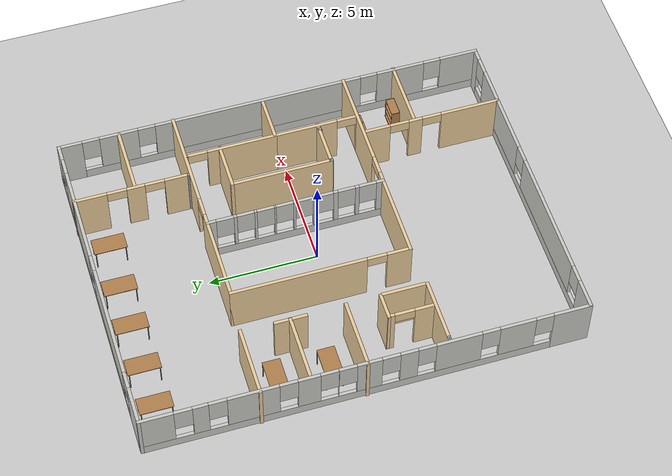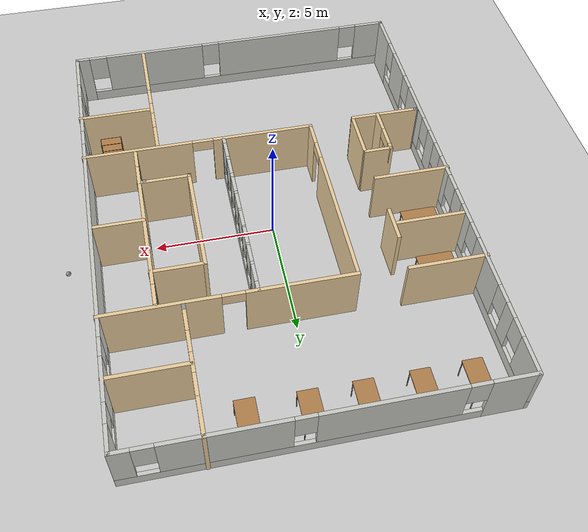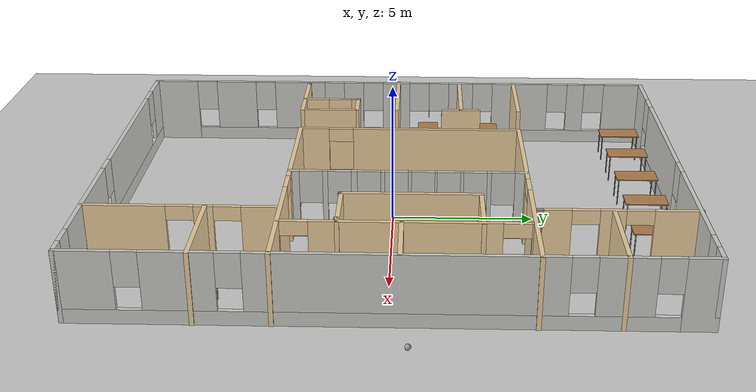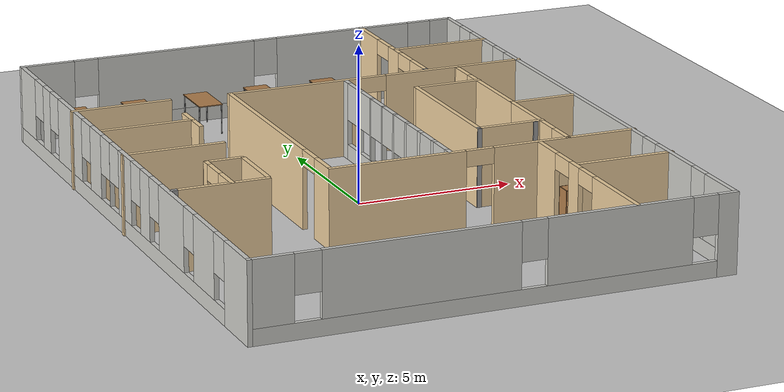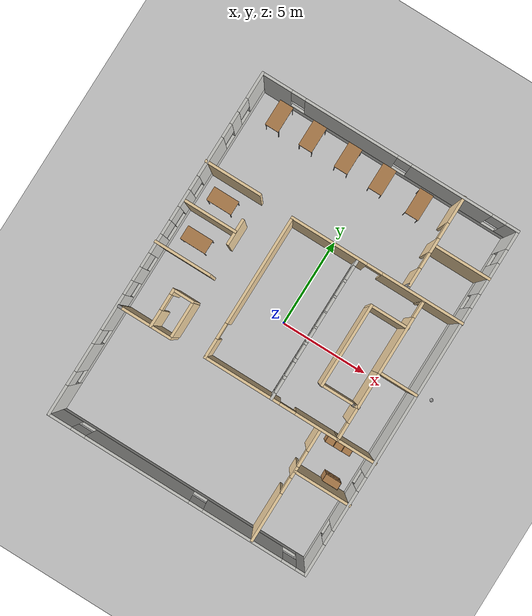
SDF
<sdf version="1.6">
 <world name="default">
  <light name="sun" type="directional">
   <pose>0 0 10 0 -0 0</pose>
   <diffuse>0.8 0.8 0.8 1</diffuse>
   <specular>0.2 0.2 0.2 1</specular>
   <attenuation>
    <range>1000</range>
    <constant>0.9</constant>
    <linear>0.01</linear>
    <quadratic>0.001</quadratic>
   </attenuation>
   <direction>-0.5 0.1 -0.9</direction>
  </light>
  <model name="ground_plane">
   <static>1</static>
   <link name="link">
    <collision name="collision">
     <geometry><plane><normal>0 0 1</normal><size>100 100</size></plane></geometry>
     <surface>
      <contact><collide_bitmask>65535</collide_bitmask></contact>
      <friction><ode><mu>100</mu><mu2>50</mu2></ode></friction>
     </surface>
    </collision>
    <visual name="visual">
     <cast_shadows>0</cast_shadows>
     <geometry><plane><normal>0 0 1</normal><size>100 100</size></plane></geometry>
     <material>
      <script><uri>file://media/materials/scripts/gazebo.material</uri><name>Gazebo/Grey</name></script>
     </material>
    </visual>
   </link>
  </model>
  <gravity>0 0 -9.8</gravity>
  <magnetic_field>6e-06 2.3e-05 -4.2e-05</magnetic_field>
  <atmosphere type="adiabatic"/>
  <physics name="default_physics" default="0" type="ode">
   <max_step_size>0.001</max_step_size>
   <real_time_factor>1</real_time_factor>
   <real_time_update_rate>1000</real_time_update_rate>
  </physics>
  <scene><ambient>0.4 0.4 0.4 1</ambient><background>0.7 0.7 0.7 1</background><shadows>1</shadows></scene>
  <spherical_coordinates>
   <surface_model>EARTH_WGS84</surface_model>
   <latitude_deg>0</latitude_deg>
   <longitude_deg>0</longitude_deg>
   <elevation>0</elevation>
   <heading_deg>0</heading_deg>
  </spherical_coordinates>
  <model name="table">
   <static>1</static>
   <link name="link">
    <collision name="surface">
     <pose>0 0 1 0 -0 0</pose>
     <geometry><box><size>1.5 0.8 0.03</size></box></geometry>
     <surface><friction><ode><mu>0.6</mu><mu2>0.6</mu2></ode></friction></surface>
    </collision>
    <visual name="visual1">
     <pose>0 0 1 0 -0 0</pose>
     <geometry><box><size>1.5 0.8 0.03</size></box></geometry>
     <material>
      <script><uri>file://media/materials/scripts/gazebo.material</uri><name>Gazebo/Wood</name></script>
     </material>
    </visual>
    <collision name="front_left_leg">
     <pose>0.68 0.38 0.5 0 -0 0</pose>
     <geometry><cylinder><radius>0.02</radius><length>1</length></cylinder></geometry>
    </collision>
    <visual name="front_left_leg">
     <pose>0.68 0.38 0.5 0 -0 0</pose>
     <geometry><cylinder><radius>0.02</radius><length>1</length></cylinder></geometry>
     <material>
      <script><uri>file://media/materials/scripts/gazebo.material</uri><name>Gazebo/Grey</name></script>
     </material>
    </visual>
    <collision name="front_right_leg">
     <pose>0.68 -0.38 0.5 0 -0 0</pose>
     <geometry><cylinder><radius>0.02</radius><length>1</length></cylinder></geometry>
    </collision>
    <visual name="front_right_leg">
     <pose>0.68 -0.38 0.5 0 -0 0</pose>
     <geometry><cylinder><radius>0.02</radius><length>1</length></cylinder></geometry>
     <material>
      <script><uri>file://media/materials/scripts/gazebo.material</uri><name>Gazebo/Grey</name></script>
     </material>
    </visual>
    <collision name="back_right_leg">
     <pose>-0.68 -0.38 0.5 0 -0 0</pose>
     <geometry><cylinder><radius>0.02</radius><length>1</length></cylinder></geometry>
    </collision>
    <visual name="back_right_leg">
     <pose>-0.68 -0.38 0.5 0 -0 0</pose>
     <geometry><cylinder><radius>0.02</radius><length>1</length></cylinder></geometry>
     <material>
      <script><uri>file://media/materials/scripts/gazebo.material</uri><name>Gazebo/Grey</name></script>
     </material>
    </visual>
    <collision name="back_left_leg">
     <pose>-0.68 0.38 0.5 0 -0 0</pose>
     <geometry><cylinder><radius>0.02</radius><length>1</length></cylinder></geometry>
    </collision>
    <visual name="back_left_leg">
     <pose>-0.68 0.38 0.5 0 -0 0</pose>
     <geometry><cylinder><radius>0.02</radius><length>1</length></cylinder></geometry>
     <material>
      <script><uri>file://media/materials/scripts/gazebo.material</uri><name>Gazebo/Grey</name></script>
     </material>
    </visual>
   </link>
   <pose>2.66975 8.85523 0 0 -0 1.57</pose>
  </model>
  <model name="table_clone">
   <static>1</static>
   <link name="link">
    <collision name="surface">
     <pose>0 0 1 0 -0 0</pose>
     <geometry><box><size>1.5 0.8 0.03</size></box></geometry>
     <surface><friction><ode><mu>0.6</mu><mu2>0.6</mu2></ode></friction></surface>
    </collision>
    <visual name="visual1">
     <pose>0 0 1 0 -0 0</pose>
     <geometry><box><size>1.5 0.8 0.03</size></box></geometry>
     <material>
      <script><uri>file://media/materials/scripts/gazebo.material</uri><name>Gazebo/Wood</name></script>
     </material>
    </visual>
    <collision name="front_left_leg">
     <pose>0.68 0.38 0.5 0 -0 0</pose>
     <geometry><cylinder><radius>0.02</radius><length>1</length></cylinder></geometry>
    </collision>
    <visual name="front_left_leg">
     <pose>0.68 0.38 0.5 0 -0 0</pose>
     <geometry><cylinder><radius>0.02</radius><length>1</length></cylinder></geometry>
     <material>
      <script><uri>file://media/materials/scripts/gazebo.material</uri><name>Gazebo/Grey</name></script>
     </material>
    </visual>
    <collision name="front_right_leg">
     <pose>0.68 -0.38 0.5 0 -0 0</pose>
     <geometry><cylinder><radius>0.02</radius><length>1</length></cylinder></geometry>
    </collision>
    <visual name="front_right_leg">
     <pose>0.68 -0.38 0.5 0 -0 0</pose>
     <geometry><cylinder><radius>0.02</radius><length>1</length></cylinder></geometry>
     <material>
      <script><uri>file://media/materials/scripts/gazebo.material</uri><name>Gazebo/Grey</name></script>
     </material>
    </visual>
    <collision name="back_right_leg">
     <pose>-0.68 -0.38 0.5 0 -0 0</pose>
     <geometry><cylinder><radius>0.02</radius><length>1</length></cylinder></geometry>
    </collision>
    <visual name="back_right_leg">
     <pose>-0.68 -0.38 0.5 0 -0 0</pose>
     <geometry><cylinder><radius>0.02</radius><length>1</length></cylinder></geometry>
     <material>
      <script><uri>file://media/materials/scripts/gazebo.material</uri><name>Gazebo/Grey</name></script>
     </material>
    </visual>
    <collision name="back_left_leg">
     <pose>-0.68 0.38 0.5 0 -0 0</pose>
     <geometry><cylinder><radius>0.02</radius><length>1</length></cylinder></geometry>
    </collision>
    <visual name="back_left_leg">
     <pose>-0.68 0.38 0.5 0 -0 0</pose>
     <geometry><cylinder><radius>0.02</radius><length>1</length></cylinder></geometry>
     <material>
      <script><uri>file://media/materials/scripts/gazebo.material</uri><name>Gazebo/Grey</name></script>
     </material>
    </visual>
   </link>
   <pose>0.377686 8.9462 0 0 -0 1.57</pose>
  </model>
  <model name="table_clone_clone_clone">
   <static>1</static>
   <link name="link">
    <collision name="surface">
     <pose>0 0 1 0 -0 0</pose>
     <geometry><box><size>1.5 0.8 0.03</size></box></geometry>
     <surface><friction><ode><mu>0.6</mu><mu2>0.6</mu2></ode></friction></surface>
    </collision>
    <visual name="visual1">
     <pose>0 0 1 0 -0 0</pose>
     <geometry><box><size>1.5 0.8 0.03</size></box></geometry>
     <material>
      <script><uri>file://media/materials/scripts/gazebo.material</uri><name>Gazebo/Wood</name></script>
     </material>
    </visual>
    <collision name="front_left_leg">
     <pose>0.68 0.38 0.5 0 -0 0</pose>
     <geometry><cylinder><radius>0.02</radius><length>1</length></cylinder></geometry>
    </collision>
    <visual name="front_left_leg">
     <pose>0.68 0.38 0.5 0 -0 0</pose>
     <geometry><cylinder><radius>0.02</radius><length>1</length></cylinder></geometry>
     <material>
      <script><uri>file://media/materials/scripts/gazebo.material</uri><name>Gazebo/Grey</name></script>
     </material>
    </visual>
    <collision name="front_right_leg">
     <pose>0.68 -0.38 0.5 0 -0 0</pose>
     <geometry><cylinder><radius>0.02</radius><length>1</length></cylinder></geometry>
    </collision>
    <visual name="front_right_leg">
     <pose>0.68 -0.38 0.5 0 -0 0</pose>
     <geometry><cylinder><radius>0.02</radius><length>1</length></cylinder></geometry>
     <material>
      <script><uri>file://media/materials/scripts/gazebo.material</uri><name>Gazebo/Grey</name></script>
     </material>
    </visual>
    <collision name="back_right_leg">
     <pose>-0.68 -0.38 0.5 0 -0 0</pose>
     <geometry><cylinder><radius>0.02</radius><length>1</length></cylinder></geometry>
    </collision>
    <visual name="back_right_leg">
     <pose>-0.68 -0.38 0.5 0 -0 0</pose>
     <geometry><cylinder><radius>0.02</radius><length>1</length></cylinder></geometry>
     <material>
      <script><uri>file://media/materials/scripts/gazebo.material</uri><name>Gazebo/Grey</name></script>
     </material>
    </visual>
    <collision name="back_left_leg">
     <pose>-0.68 0.38 0.5 0 -0 0</pose>
     <geometry><cylinder><radius>0.02</radius><length>1</length></cylinder></geometry>
    </collision>
    <visual name="back_left_leg">
     <pose>-0.68 0.38 0.5 0 -0 0</pose>
     <geometry><cylinder><radius>0.02</radius><length>1</length></cylinder></geometry>
     <material>
      <script><uri>file://media/materials/scripts/gazebo.material</uri><name>Gazebo/Grey</name></script>
     </material>
    </visual>
   </link>
   <pose>-3.84215 8.93597 0 0 -0 1.57</pose>
  </model>
  <model name="table_clone_clone_clone_clone">
   <static>1</static>
   <link name="link">
    <collision name="surface">
     <pose>0 0 1 0 -0 0</pose>
     <geometry><box><size>1.5 0.8 0.03</size></box></geometry>
     <surface><friction><ode><mu>0.6</mu><mu2>0.6</mu2></ode></friction></surface>
    </collision>
    <visual name="visual1">
     <pose>0 0 1 0 -0 0</pose>
     <geometry><box><size>1.5 0.8 0.03</size></box></geometry>
     <material>
      <script><uri>file://media/materials/scripts/gazebo.material</uri><name>Gazebo/Wood</name></script>
     </material>
    </visual>
    <collision name="front_left_leg">
     <pose>0.68 0.38 0.5 0 -0 0</pose>
     <geometry><cylinder><radius>0.02</radius><length>1</length></cylinder></geometry>
    </collision>
    <visual name="front_left_leg">
     <pose>0.68 0.38 0.5 0 -0 0</pose>
     <geometry><cylinder><radius>0.02</radius><length>1</length></cylinder></geometry>
     <material>
      <script><uri>file://media/materials/scripts/gazebo.material</uri><name>Gazebo/Grey</name></script>
     </material>
    </visual>
    <collision name="front_right_leg">
     <pose>0.68 -0.38 0.5 0 -0 0</pose>
     <geometry><cylinder><radius>0.02</radius><length>1</length></cylinder></geometry>
    </collision>
    <visual name="front_right_leg">
     <pose>0.68 -0.38 0.5 0 -0 0</pose>
     <geometry><cylinder><radius>0.02</radius><length>1</length></cylinder></geometry>
     <material>
      <script><uri>file://media/materials/scripts/gazebo.material</uri><name>Gazebo/Grey</name></script>
     </material>
    </visual>
    <collision name="back_right_leg">
     <pose>-0.68 -0.38 0.5 0 -0 0</pose>
     <geometry><cylinder><radius>0.02</radius><length>1</length></cylinder></geometry>
    </collision>
    <visual name="back_right_leg">
     <pose>-0.68 -0.38 0.5 0 -0 0</pose>
     <geometry><cylinder><radius>0.02</radius><length>1</length></cylinder></geometry>
     <material>
      <script><uri>file://media/materials/scripts/gazebo.material</uri><name>Gazebo/Grey</name></script>
     </material>
    </visual>
    <collision name="back_left_leg">
     <pose>-0.68 0.38 0.5 0 -0 0</pose>
     <geometry><cylinder><radius>0.02</radius><length>1</length></cylinder></geometry>
    </collision>
    <visual name="back_left_leg">
     <pose>-0.68 0.38 0.5 0 -0 0</pose>
     <geometry><cylinder><radius>0.02</radius><length>1</length></cylinder></geometry>
     <material>
      <script><uri>file://media/materials/scripts/gazebo.material</uri><name>Gazebo/Grey</name></script>
     </material>
    </visual>
   </link>
   <pose>-5.86091 8.91423 0 0 -0 1.57</pose>
  </model>
  <model name="table_clone_clone">
   <static>1</static>
   <link name="link">
    <collision name="surface">
     <pose>0 0 1 0 -0 0</pose>
     <geometry><box><size>1.5 0.8 0.03</size></box></geometry>
     <surface><friction><ode><mu>0.6</mu><mu2>0.6</mu2></ode></friction></surface>
    </collision>
    <visual name="visual1">
     <pose>0 0 1 0 -0 0</pose>
     <geometry><box><size>1.5 0.8 0.03</size></box></geometry>
     <material>
      <script><uri>file://media/materials/scripts/gazebo.material</uri><name>Gazebo/Wood</name></script>
     </material>
    </visual>
    <collision name="front_left_leg">
     <pose>0.68 0.38 0.5 0 -0 0</pose>
     <geometry><cylinder><radius>0.02</radius><length>1</length></cylinder></geometry>
    </collision>
    <visual name="front_left_leg">
     <pose>0.68 0.38 0.5 0 -0 0</pose>
     <geometry><cylinder><radius>0.02</radius><length>1</length></cylinder></geometry>
     <material>
      <script><uri>file://media/materials/scripts/gazebo.material</uri><name>Gazebo/Grey</name></script>
     </material>
    </visual>
    <collision name="front_right_leg">
     <pose>0.68 -0.38 0.5 0 -0 0</pose>
     <geometry><cylinder><radius>0.02</radius><length>1</length></cylinder></geometry>
    </collision>
    <visual name="front_right_leg">
     <pose>0.68 -0.38 0.5 0 -0 0</pose>
     <geometry><cylinder><radius>0.02</radius><length>1</length></cylinder></geometry>
     <material>
      <script><uri>file://media/materials/scripts/gazebo.material</uri><name>Gazebo/Grey</name></script>
     </material>
    </visual>
    <collision name="back_right_leg">
     <pose>-0.68 -0.38 0.5 0 -0 0</pose>
     <geometry><cylinder><radius>0.02</radius><length>1</length></cylinder></geometry>
    </collision>
    <visual name="back_right_leg">
     <pose>-0.68 -0.38 0.5 0 -0 0</pose>
     <geometry><cylinder><radius>0.02</radius><length>1</length></cylinder></geometry>
     <material>
      <script><uri>file://media/materials/scripts/gazebo.material</uri><name>Gazebo/Grey</name></script>
     </material>
    </visual>
    <collision name="back_left_leg">
     <pose>-0.68 0.38 0.5 0 -0 0</pose>
     <geometry><cylinder><radius>0.02</radius><length>1</length></cylinder></geometry>
    </collision>
    <visual name="back_left_leg">
     <pose>-0.68 0.38 0.5 0 -0 0</pose>
     <geometry><cylinder><radius>0.02</radius><length>1</length></cylinder></geometry>
     <material>
      <script><uri>file://media/materials/scripts/gazebo.material</uri><name>Gazebo/Grey</name></script>
     </material>
    </visual>
   </link>
   <pose>-1.69364 8.94576 0 0 -0 1.57</pose>
  </model>
  <model name="cabinet">
   <static>1</static>
   <link name="cabinet_bottom_plate">
    <inertial>
     <pose>0 0 -1 0 -0 0</pose>
     <inertia><ixx>2.05</ixx><ixy>0</ixy><ixz>0</ixz><iyy>2.05</iyy><iyz>0</iyz><izz>2.05</izz></inertia>
     <mass>25</mass>
    </inertial>
    <collision name="cabinet_bottom_plate_geom">
     <pose>0 0 0.01 0 -0 0</pose>
     <geometry><box><size>0.45 0.45 0.02</size></box></geometry>
    </collision>
    <visual name="cabinet_bottom_plate_geom_visual">
     <pose>0 0 0.01 0 -0 0</pose>
     <geometry><box><size>0.45 0.45 0.02</size></box></geometry>
     <material>
      <script><uri>file://media/materials/scripts/gazebo.material</uri><name>Gazebo/Wood</name></script>
     </material>
    </visual>
    <collision name="cabinet_bottom_plate_geom_cabinet_back_plate">
     <pose>0.235 0 0.51 0 -0 0</pose>
     <geometry><box><size>0.02 0.45 1.02</size></box></geometry>
    </collision>
    <visual name="cabinet_bottom_plate_geom_cabinet_back_plate_visual">
     <pose>0.235 0 0.51 0 -0 0</pose>
     <geometry><box><size>0.02 0.45 1.02</size></box></geometry>
     <material>
      <script><uri>file://media/materials/scripts/gazebo.material</uri><name>Gazebo/Wood</name></script>
     </material>
    </visual>
    <collision name="cabinet_bottom_plate_geom_cabinet_left_plate">
     <pose>0 0.235 0.51 0 -0 0</pose>
     <geometry><box><size>0.45 0.02 1.02</size></box></geometry>
    </collision>
    <visual name="cabinet_bottom_plate_geom_cabinet_left_plate_visual">
     <pose>0 0.235 0.51 0 -0 0</pose>
     <geometry><box><size>0.45 0.02 1.02</size></box></geometry>
     <material>
      <script><uri>file://media/materials/scripts/gazebo.material</uri><name>Gazebo/Wood</name></script>
     </material>
    </visual>
    <collision name="cabinet_bottom_plate_geom_cabinet_middle_plate">
     <pose>0 0 0.51 0 -0 0</pose>
     <geometry><box><size>0.45 0.45 0.02</size></box></geometry>
    </collision>
    <visual name="cabinet_bottom_plate_geom_cabinet_middle_plate_visual">
     <pose>0 0 0.51 0 -0 0</pose>
     <geometry><box><size>0.45 0.45 0.02</size></box></geometry>
     <material>
      <script><uri>file://media/materials/scripts/gazebo.material</uri><name>Gazebo/Wood</name></script>
     </material>
    </visual>
    <collision name="cabinet_bottom_plate_geom_cabinet_right_plate">
     <pose>0 -0.235 0.51 0 -0 0</pose>
     <geometry><box><size>0.45 0.02 1.02</size></box></geometry>
    </collision>
    <visual name="cabinet_bottom_plate_geom_cabinet_right_plate_visual">
     <pose>0 -0.235 0.51 0 -0 0</pose>
     <geometry><box><size>0.45 0.02 1.02</size></box></geometry>
     <material>
      <script><uri>file://media/materials/scripts/gazebo.material</uri><name>Gazebo/Wood</name></script>
     </material>
    </visual>
    <collision name="cabinet_bottom_plate_geom_cabinet_top_plate">
     <pose>0 0 1.01 0 -0 0</pose>
     <geometry><box><size>0.45 0.45 0.02</size></box></geometry>
    </collision>
    <visual name="cabinet_bottom_plate_geom_cabinet_top_plate_visual">
     <pose>0 0 1.01 0 -0 0</pose>
     <geometry><box><size>0.45 0.45 0.02</size></box></geometry>
     <material>
      <script><uri>file://media/materials/scripts/gazebo.material</uri><name>Gazebo/Wood</name></script>
     </material>
    </visual>
   </link>
   <pose>5.72812 -3.81623 0 0 -0 1.57</pose>
  </model>
  <model name="cabinet_clone">
   <static>1</static>
   <link name="cabinet_bottom_plate">
    <inertial>
     <pose>0 0 -1 0 -0 0</pose>
     <inertia><ixx>2.05</ixx><ixy>0</ixy><ixz>0</ixz><iyy>2.05</iyy><iyz>0</iyz><izz>2.05</izz></inertia>
     <mass>25</mass>
    </inertial>
    <collision name="cabinet_bottom_plate_geom">
     <pose>0 0 0.01 0 -0 0</pose>
     <geometry><box><size>0.45 0.45 0.02</size></box></geometry>
    </collision>
    <visual name="cabinet_bottom_plate_geom_visual">
     <pose>0 0 0.01 0 -0 0</pose>
     <geometry><box><size>0.45 0.45 0.02</size></box></geometry>
     <material>
      <script><uri>file://media/materials/scripts/gazebo.material</uri><name>Gazebo/Wood</name></script>
     </material>
    </visual>
    <collision name="cabinet_bottom_plate_geom_cabinet_back_plate">
     <pose>0.235 0 0.51 0 -0 0</pose>
     <geometry><box><size>0.02 0.45 1.02</size></box></geometry>
    </collision>
    <visual name="cabinet_bottom_plate_geom_cabinet_back_plate_visual">
     <pose>0.235 0 0.51 0 -0 0</pose>
     <geometry><box><size>0.02 0.45 1.02</size></box></geometry>
     <material>
      <script><uri>file://media/materials/scripts/gazebo.material</uri><name>Gazebo/Wood</name></script>
     </material>
    </visual>
    <collision name="cabinet_bottom_plate_geom_cabinet_left_plate">
     <pose>0 0.235 0.51 0 -0 0</pose>
     <geometry><box><size>0.45 0.02 1.02</size></box></geometry>
    </collision>
    <visual name="cabinet_bottom_plate_geom_cabinet_left_plate_visual">
     <pose>0 0.235 0.51 0 -0 0</pose>
     <geometry><box><size>0.45 0.02 1.02</size></box></geometry>
     <material>
      <script><uri>file://media/materials/scripts/gazebo.material</uri><name>Gazebo/Wood</name></script>
     </material>
    </visual>
    <collision name="cabinet_bottom_plate_geom_cabinet_middle_plate">
     <pose>0 0 0.51 0 -0 0</pose>
     <geometry><box><size>0.45 0.45 0.02</size></box></geometry>
    </collision>
    <visual name="cabinet_bottom_plate_geom_cabinet_middle_plate_visual">
     <pose>0 0 0.51 0 -0 0</pose>
     <geometry><box><size>0.45 0.45 0.02</size></box></geometry>
     <material>
      <script><uri>file://media/materials/scripts/gazebo.material</uri><name>Gazebo/Wood</name></script>
     </material>
    </visual>
    <collision name="cabinet_bottom_plate_geom_cabinet_right_plate">
     <pose>0 -0.235 0.51 0 -0 0</pose>
     <geometry><box><size>0.45 0.02 1.02</size></box></geometry>
    </collision>
    <visual name="cabinet_bottom_plate_geom_cabinet_right_plate_visual">
     <pose>0 -0.235 0.51 0 -0 0</pose>
     <geometry><box><size>0.45 0.02 1.02</size></box></geometry>
     <material>
      <script><uri>file://media/materials/scripts/gazebo.material</uri><name>Gazebo/Wood</name></script>
     </material>
    </visual>
    <collision name="cabinet_bottom_plate_geom_cabinet_top_plate">
     <pose>0 0 1.01 0 -0 0</pose>
     <geometry><box><size>0.45 0.45 0.02</size></box></geometry>
    </collision>
    <visual name="cabinet_bottom_plate_geom_cabinet_top_plate_visual">
     <pose>0 0 1.01 0 -0 0</pose>
     <geometry><box><size>0.45 0.45 0.02</size></box></geometry>
     <material>
      <script><uri>file://media/materials/scripts/gazebo.material</uri><name>Gazebo/Wood</name></script>
     </material>
    </visual>
   </link>
   <pose>6.21795 -3.80591 0 0 -0 1.57</pose>
  </model>
  <model name="cabinet_clone_0">
   <static>1</static>
   <link name="cabinet_bottom_plate">
    <inertial>
     <pose>0 0 -1 0 -0 0</pose>
     <inertia><ixx>2.05</ixx><ixy>0</ixy><ixz>0</ixz><iyy>2.05</iyy><iyz>0</iyz><izz>2.05</izz></inertia>
     <mass>25</mass>
    </inertial>
    <collision name="cabinet_bottom_plate_geom">
     <pose>0 0 0.01 0 -0 0</pose>
     <geometry><box><size>0.45 0.45 0.02</size></box></geometry>
    </collision>
    <visual name="cabinet_bottom_plate_geom_visual">
     <pose>0 0 0.01 0 -0 0</pose>
     <geometry><box><size>0.45 0.45 0.02</size></box></geometry>
     <material>
      <script><uri>file://media/materials/scripts/gazebo.material</uri><name>Gazebo/Wood</name></script>
     </material>
    </visual>
    <collision name="cabinet_bottom_plate_geom_cabinet_back_plate">
     <pose>0.235 0 0.51 0 -0 0</pose>
     <geometry><box><size>0.02 0.45 1.02</size></box></geometry>
    </collision>
    <visual name="cabinet_bottom_plate_geom_cabinet_back_plate_visual">
     <pose>0.235 0 0.51 0 -0 0</pose>
     <geometry><box><size>0.02 0.45 1.02</size></box></geometry>
     <material>
      <script><uri>file://media/materials/scripts/gazebo.material</uri><name>Gazebo/Wood</name></script>
     </material>
    </visual>
    <collision name="cabinet_bottom_plate_geom_cabinet_left_plate">
     <pose>0 0.235 0.51 0 -0 0</pose>
     <geometry><box><size>0.45 0.02 1.02</size></box></geometry>
    </collision>
    <visual name="cabinet_bottom_plate_geom_cabinet_left_plate_visual">
     <pose>0 0.235 0.51 0 -0 0</pose>
     <geometry><box><size>0.45 0.02 1.02</size></box></geometry>
     <material>
      <script><uri>file://media/materials/scripts/gazebo.material</uri><name>Gazebo/Wood</name></script>
     </material>
    </visual>
    <collision name="cabinet_bottom_plate_geom_cabinet_middle_plate">
     <pose>0 0 0.51 0 -0 0</pose>
     <geometry><box><size>0.45 0.45 0.02</size></box></geometry>
    </collision>
    <visual name="cabinet_bottom_plate_geom_cabinet_middle_plate_visual">
     <pose>0 0 0.51 0 -0 0</pose>
     <geometry><box><size>0.45 0.45 0.02</size></box></geometry>
     <material>
      <script><uri>file://media/materials/scripts/gazebo.material</uri><name>Gazebo/Wood</name></script>
     </material>
    </visual>
    <collision name="cabinet_bottom_plate_geom_cabinet_right_plate">
     <pose>0 -0.235 0.51 0 -0 0</pose>
     <geometry><box><size>0.45 0.02 1.02</size></box></geometry>
    </collision>
    <visual name="cabinet_bottom_plate_geom_cabinet_right_plate_visual">
     <pose>0 -0.235 0.51 0 -0 0</pose>
     <geometry><box><size>0.45 0.02 1.02</size></box></geometry>
     <material>
      <script><uri>file://media/materials/scripts/gazebo.material</uri><name>Gazebo/Wood</name></script>
     </material>
    </visual>
    <collision name="cabinet_bottom_plate_geom_cabinet_top_plate">
     <pose>0 0 1.01 0 -0 0</pose>
     <geometry><box><size>0.45 0.45 0.02</size></box></geometry>
    </collision>
    <visual name="cabinet_bottom_plate_geom_cabinet_top_plate_visual">
     <pose>0 0 1.01 0 -0 0</pose>
     <geometry><box><size>0.45 0.45 0.02</size></box></geometry>
     <material>
      <script><uri>file://media/materials/scripts/gazebo.material</uri><name>Gazebo/Wood</name></script>
     </material>
    </visual>
   </link>
   <pose>5.23276 -3.82024 0 0 -0 1.57</pose>
  </model>
  <model name="bookshelf">
   <static>1</static>
   <link name="link">
    <inertial><mass>1</mass></inertial>
    <collision name="back">
     <pose>0 0.005 0.6 0 -0 0</pose>
     <geometry><box><size>0.9 0.01 1.2</size></box></geometry>
    </collision>
    <visual name="visual1">
     <pose>0 0.005 0.6 0 -0 0</pose>
     <geometry><box><size>0.9 0.01 1.2</size></box></geometry>
     <material>
      <script><uri>file://media/materials/scripts/gazebo.material</uri><name>Gazebo/Wood</name></script>
     </material>
    </visual>
    <collision name="left_side">
     <pose>0.45 -0.195 0.6 0 -0 0</pose>
     <geometry><box><size>0.02 0.4 1.2</size></box></geometry>
    </collision>
    <visual name="visual2">
     <pose>0.45 -0.195 0.6 0 -0 0</pose>
     <geometry><box><size>0.02 0.4 1.2</size></box></geometry>
     <material>
      <script><uri>file://media/materials/scripts/gazebo.material</uri><name>Gazebo/Wood</name></script>
     </material>
    </visual>
    <collision name="right_side">
     <pose>-0.45 -0.195 0.6 0 -0 0</pose>
     <geometry><box><size>0.02 0.4 1.2</size></box></geometry>
    </collision>
    <visual name="visual3">
     <pose>-0.45 -0.195 0.6 0 -0 0</pose>
     <geometry><box><size>0.02 0.4 1.2</size></box></geometry>
     <material>
      <script><uri>file://media/materials/scripts/gazebo.material</uri><name>Gazebo/Wood</name></script>
     </material>
    </visual>
    <collision name="bottom">
     <pose>0 -0.195 0.03 0 -0 0</pose>
     <geometry><box><size>0.88 0.4 0.06</size></box></geometry>
    </collision>
    <visual name="visual4">
     <pose>0 -0.195 0.03 0 -0 0</pose>
     <geometry><box><size>0.88 0.4 0.06</size></box></geometry>
     <material>
      <script><uri>file://media/materials/scripts/gazebo.material</uri><name>Gazebo/Wood</name></script>
     </material>
    </visual>
    <collision name="top">
     <pose>0 -0.195 1.19 0 -0 0</pose>
     <geometry><box><size>0.88 0.4 0.02</size></box></geometry>
    </collision>
    <visual name="visual5">
     <pose>0 -0.195 1.19 0 -0 0</pose>
     <geometry><box><size>0.88 0.4 0.02</size></box></geometry>
     <material>
      <script><uri>file://media/materials/scripts/gazebo.material</uri><name>Gazebo/Wood</name></script>
     </material>
    </visual>
    <collision name="low_shelf">
     <pose>0 -0.195 0.43 0 -0 0</pose>
     <geometry><box><size>0.88 0.4 0.02</size></box></geometry>
    </collision>
    <visual name="visual6">
     <pose>0 -0.195 0.43 0 -0 0</pose>
     <geometry><box><size>0.88 0.4 0.02</size></box></geometry>
     <material>
      <script><uri>file://media/materials/scripts/gazebo.material</uri><name>Gazebo/Wood</name></script>
     </material>
    </visual>
    <collision name="high_shelf">
     <pose>0 -0.195 0.8 0 -0 0</pose>
     <geometry><box><size>0.88 0.4 0.02</size></box></geometry>
    </collision>
    <visual name="visual7">
     <pose>0 -0.195 0.8 0 -0 0</pose>
     <geometry><box><size>0.88 0.4 0.02</size></box></geometry>
     <material>
      <script><uri>file://media/materials/scripts/gazebo.material</uri><name>Gazebo/Wood</name></script>
     </material>
    </visual>
   </link>
   <pose>6.34803 -5.77495 0 0 -0 3.14</pose>
  </model>
  <model name="table_0">
   <static>1</static>
   <link name="link">
    <collision name="surface">
     <pose>0 0 1 0 -0 0</pose>
     <geometry><box><size>1.5 0.8 0.03</size></box></geometry>
     <surface><friction><ode><mu>0.6</mu><mu2>0.6</mu2></ode></friction></surface>
    </collision>
    <visual name="visual1">
     <pose>0 0 1 0 -0 0</pose>
     <geometry><box><size>1.5 0.8 0.03</size></box></geometry>
     <material>
      <script><uri>file://media/materials/scripts/gazebo.material</uri><name>Gazebo/Wood</name></script>
     </material>
    </visual>
    <collision name="front_left_leg">
     <pose>0.68 0.38 0.5 0 -0 0</pose>
     <geometry><cylinder><radius>0.02</radius><length>1</length></cylinder></geometry>
    </collision>
    <visual name="front_left_leg">
     <pose>0.68 0.38 0.5 0 -0 0</pose>
     <geometry><cylinder><radius>0.02</radius><length>1</length></cylinder></geometry>
     <material>
      <script><uri>file://media/materials/scripts/gazebo.material</uri><name>Gazebo/Grey</name></script>
     </material>
    </visual>
    <collision name="front_right_leg">
     <pose>0.68 -0.38 0.5 0 -0 0</pose>
     <geometry><cylinder><radius>0.02</radius><length>1</length></cylinder></geometry>
    </collision>
    <visual name="front_right_leg">
     <pose>0.68 -0.38 0.5 0 -0 0</pose>
     <geometry><cylinder><radius>0.02</radius><length>1</length></cylinder></geometry>
     <material>
      <script><uri>file://media/materials/scripts/gazebo.material</uri><name>Gazebo/Grey</name></script>
     </material>
    </visual>
    <collision name="back_right_leg">
     <pose>-0.68 -0.38 0.5 0 -0 0</pose>
     <geometry><cylinder><radius>0.02</radius><length>1</length></cylinder></geometry>
    </collision>
    <visual name="back_right_leg">
     <pose>-0.68 -0.38 0.5 0 -0 0</pose>
     <geometry><cylinder><radius>0.02</radius><length>1</length></cylinder></geometry>
     <material>
      <script><uri>file://media/materials/scripts/gazebo.material</uri><name>Gazebo/Grey</name></script>
     </material>
    </visual>
    <collision name="back_left_leg">
     <pose>-0.68 0.38 0.5 0 -0 0</pose>
     <geometry><cylinder><radius>0.02</radius><length>1</length></cylinder></geometry>
    </collision>
    <visual name="back_left_leg">
     <pose>-0.68 0.38 0.5 0 -0 0</pose>
     <geometry><cylinder><radius>0.02</radius><length>1</length></cylinder></geometry>
     <material>
      <script><uri>file://media/materials/scripts/gazebo.material</uri><name>Gazebo/Grey</name></script>
     </material>
    </visual>
   </link>
   <pose>-6.00758 3.65362 0 0 -0 0</pose>
  </model>
  <model name="table_0_clone">
   <static>1</static>
   <link name="link">
    <collision name="surface">
     <pose>0 0 1 0 -0 0</pose>
     <geometry><box><size>1.5 0.8 0.03</size></box></geometry>
     <surface><friction><ode><mu>0.6</mu><mu2>0.6</mu2></ode></friction></surface>
    </collision>
    <visual name="visual1">
     <pose>0 0 1 0 -0 0</pose>
     <geometry><box><size>1.5 0.8 0.03</size></box></geometry>
     <material>
      <script><uri>file://media/materials/scripts/gazebo.material</uri><name>Gazebo/Wood</name></script>
     </material>
    </visual>
    <collision name="front_left_leg">
     <pose>0.68 0.38 0.5 0 -0 0</pose>
     <geometry><cylinder><radius>0.02</radius><length>1</length></cylinder></geometry>
    </collision>
    <visual name="front_left_leg">
     <pose>0.68 0.38 0.5 0 -0 0</pose>
     <geometry><cylinder><radius>0.02</radius><length>1</length></cylinder></geometry>
     <material>
      <script><uri>file://media/materials/scripts/gazebo.material</uri><name>Gazebo/Grey</name></script>
     </material>
    </visual>
    <collision name="front_right_leg">
     <pose>0.68 -0.38 0.5 0 -0 0</pose>
     <geometry><cylinder><radius>0.02</radius><length>1</length></cylinder></geometry>
    </collision>
    <visual name="front_right_leg">
     <pose>0.68 -0.38 0.5 0 -0 0</pose>
     <geometry><cylinder><radius>0.02</radius><length>1</length></cylinder></geometry>
     <material>
      <script><uri>file://media/materials/scripts/gazebo.material</uri><name>Gazebo/Grey</name></script>
     </material>
    </visual>
    <collision name="back_right_leg">
     <pose>-0.68 -0.38 0.5 0 -0 0</pose>
     <geometry><cylinder><radius>0.02</radius><length>1</length></cylinder></geometry>
    </collision>
    <visual name="back_right_leg">
     <pose>-0.68 -0.38 0.5 0 -0 0</pose>
     <geometry><cylinder><radius>0.02</radius><length>1</length></cylinder></geometry>
     <material>
      <script><uri>file://media/materials/scripts/gazebo.material</uri><name>Gazebo/Grey</name></script>
     </material>
    </visual>
    <collision name="back_left_leg">
     <pose>-0.68 0.38 0.5 0 -0 0</pose>
     <geometry><cylinder><radius>0.02</radius><length>1</length></cylinder></geometry>
    </collision>
    <visual name="back_left_leg">
     <pose>-0.68 0.38 0.5 0 -0 0</pose>
     <geometry><cylinder><radius>0.02</radius><length>1</length></cylinder></geometry>
     <material>
      <script><uri>file://media/materials/scripts/gazebo.material</uri><name>Gazebo/Grey</name></script>
     </material>
    </visual>
   </link>
   <pose>-6.08055 1.24411 0 0 -0 0</pose>
  </model>
  <model name="AutowayTower">
   <link name="Wall_0">
    <pose>0.012137 7.42869 0 0 -0 0</pose>
    <visual name="Wall_0_Visual_0">
     <pose>-9.43131 0 1.25 0 -0 0</pose>
     <geometry><box><size>1.13738 0.15 2.5</size></box></geometry>
     <material>
      <script><uri>file://media/materials/scripts/gazebo.material</uri><name>Gazebo/CeilingTiled</name></script>
      <ambient>1 1 1 1</ambient>
      <shader type="pixel"/>
      <diffuse>1 1 1 1</diffuse>
      <specular>0 0 0 1</specular>
      <emissive>0 0 0 1</emissive>
     </material>
     <meta><layer>0</layer></meta>
    </visual>
    <visual name="Wall_0_Visual_1">
     <pose>0.56869 0 0.25 0 -0 0</pose>
     <geometry><box><size>18.8626 0.15 0.5</size></box></geometry>
     <material>
      <script><uri>file://media/materials/scripts/gazebo.material</uri><name>Gazebo/CeilingTiled</name></script>
      <ambient>1 1 1 1</ambient>
      <shader type="pixel"/>
      <diffuse>1 1 1 1</diffuse>
      <specular>0 0 0 1</specular>
      <emissive>0 0 0 1</emissive>
     </material>
     <meta><layer>0</layer></meta>
    </visual>
    <visual name="Wall_0_Visual_2">
     <pose>-7.16836 0 1.5 0 -0 0</pose>
     <geometry><box><size>1.78853 0.15 2</size></box></geometry>
     <material>
      <script><uri>file://media/materials/scripts/gazebo.material</uri><name>Gazebo/CeilingTiled</name></script>
      <ambient>1 1 1 1</ambient>
      <shader type="pixel"/>
      <diffuse>1 1 1 1</diffuse>
      <specular>0 0 0 1</specular>
      <emissive>0 0 0 1</emissive>
     </material>
     <meta><layer>0</layer></meta>
    </visual>
    <visual name="Wall_0_Visual_3">
     <pose>-0.583346 0 1.5 0 -0 0</pose>
     <geometry><box><size>9.78149 0.15 2</size></box></geometry>
     <material>
      <script><uri>file://media/materials/scripts/gazebo.material</uri><name>Gazebo/CeilingTiled</name></script>
      <ambient>1 1 1 1</ambient>
      <shader type="pixel"/>
      <diffuse>1 1 1 1</diffuse>
      <specular>0 0 0 1</specular>
      <emissive>0 0 0 1</emissive>
     </material>
     <meta><layer>0</layer></meta>
    </visual>
    <visual name="Wall_0_Visual_4">
     <pose>6.24652 0 1.5 0 -0 0</pose>
     <geometry><box><size>2.27825 0.15 2</size></box></geometry>
     <material>
      <script><uri>file://media/materials/scripts/gazebo.material</uri><name>Gazebo/CeilingTiled</name></script>
      <ambient>1 1 1 1</ambient>
      <shader type="pixel"/>
      <diffuse>1 1 1 1</diffuse>
      <specular>0 0 0 1</specular>
      <emissive>0 0 0 1</emissive>
     </material>
     <meta><layer>0</layer></meta>
    </visual>
    <visual name="Wall_0_Visual_5">
     <pose>9.09282 0 1.5 0 -0 0</pose>
     <geometry><box><size>1.81435 0.15 2</size></box></geometry>
     <material>
      <script><uri>file://media/materials/scripts/gazebo.material</uri><name>Gazebo/CeilingTiled</name></script>
      <ambient>1 1 1 1</ambient>
      <shader type="pixel"/>
      <diffuse>1 1 1 1</diffuse>
      <specular>0 0 0 1</specular>
      <emissive>0 0 0 1</emissive>
     </material>
     <meta><layer>0</layer></meta>
    </visual>
    <visual name="Wall_0_Visual_6">
     <pose>-8.46262 0 1.9 0 -0 0</pose>
     <geometry><box><size>0.8 0.15 1.2</size></box></geometry>
     <material>
      <script><uri>file://media/materials/scripts/gazebo.material</uri><name>Gazebo/CeilingTiled</name></script>
      <ambient>1 1 1 1</ambient>
      <shader type="pixel"/>
      <diffuse>1 1 1 1</diffuse>
      <specular>0 0 0 1</specular>
      <emissive>0 0 0 1</emissive>
     </material>
     <meta><layer>0</layer></meta>
    </visual>
    <visual name="Wall_0_Visual_7">
     <pose>-5.87409 0 1.9 0 -0 0</pose>
     <geometry><box><size>0.8 0.15 1.2</size></box></geometry>
     <material>
      <script><uri>file://media/materials/scripts/gazebo.material</uri><name>Gazebo/CeilingTiled</name></script>
      <ambient>1 1 1 1</ambient>
      <shader type="pixel"/>
      <diffuse>1 1 1 1</diffuse>
      <specular>0 0 0 1</specular>
      <emissive>0 0 0 1</emissive>
     </material>
     <meta><layer>0</layer></meta>
    </visual>
    <visual name="Wall_0_Visual_8">
     <pose>4.7074 0 1.9 0 -0 0</pose>
     <geometry><box><size>0.8 0.15 1.2</size></box></geometry>
     <material>
      <script><uri>file://media/materials/scripts/gazebo.material</uri><name>Gazebo/CeilingTiled</name></script>
      <ambient>1 1 1 1</ambient>
      <shader type="pixel"/>
      <diffuse>1 1 1 1</diffuse>
      <specular>0 0 0 1</specular>
      <emissive>0 0 0 1</emissive>
     </material>
     <meta><layer>0</layer></meta>
    </visual>
    <visual name="Wall_0_Visual_9">
     <pose>7.78565 0 1.9 0 -0 0</pose>
     <geometry><box><size>0.8 0.15 1.2</size></box></geometry>
     <material>
      <script><uri>file://media/materials/scripts/gazebo.material</uri><name>Gazebo/CeilingTiled</name></script>
      <ambient>1 1 1 1</ambient>
      <shader type="pixel"/>
      <diffuse>1 1 1 1</diffuse>
      <specular>0 0 0 1</specular>
      <emissive>0 0 0 1</emissive>
     </material>
     <meta><layer>0</layer></meta>
    </visual>
    <collision name="Wall_0_Collision_6">
     <pose>-8.46262 0 1.9 0 -0 0</pose>
     <geometry><box><size>0.8 0.15 1.2</size></box></geometry>
     <surface>
      <friction>
       <ode><mu>1</mu><mu2>1</mu2><fdir1>0 0 0</fdir1><slip1>0</slip1><slip2>0</slip2></ode>
       <torsional>
        <coefficient>1</coefficient>
        <patch_radius>0</patch_radius>
        <surface_radius>0</surface_radius>
        <use_patch_radius>1</use_patch_radius>
        <ode><slip>0</slip></ode>
       </torsional>
      </friction>
      <bounce><restitution_coefficient>0</restitution_coefficient><threshold>1e+06</threshold></bounce>
      <contact>
       <collide_without_contact>0</collide_without_contact>
       <collide_without_contact_bitmask>1</collide_without_contact_bitmask>
       <collide_bitmask>1</collide_bitmask>
       <ode>
        <soft_cfm>0</soft_cfm>
        <soft_erp>0.2</soft_erp>
        <kp>1e+13</kp>
        <kd>1</kd>
        <max_vel>0.01</max_vel>
        <min_depth>0</min_depth>
       </ode>
       <bullet>
        <split_impulse>1</split_impulse>
        <split_impulse_penetration_threshold>-0.01</split_impulse_penetration_threshold>
        <soft_cfm>0</soft_cfm>
        <soft_erp>0.2</soft_erp>
        <kp>1e+13</kp>
        <kd>1</kd>
       </bullet>
      </contact>
     </surface>
    </collision>
    <collision name="Wall_0_Collision_0">
     <pose>-9.43131 0 1.25 0 -0 0</pose>
     <geometry><box><size>1.13738 0.15 2.5</size></box></geometry>
     <surface>
      <friction>
       <ode><mu>1</mu><mu2>1</mu2><fdir1>0 0 0</fdir1><slip1>0</slip1><slip2>0</slip2></ode>
       <torsional>
        <coefficient>1</coefficient>
        <patch_radius>0</patch_radius>
        <surface_radius>0</surface_radius>
        <use_patch_radius>1</use_patch_radius>
        <ode><slip>0</slip></ode>
       </torsional>
      </friction>
      <bounce><restitution_coefficient>0</restitution_coefficient><threshold>1e+06</threshold></bounce>
      <contact>
       <collide_without_contact>0</collide_without_contact>
       <collide_without_contact_bitmask>1</collide_without_contact_bitmask>
       <collide_bitmask>1</collide_bitmask>
       <ode>
        <soft_cfm>0</soft_cfm>
        <soft_erp>0.2</soft_erp>
        <kp>1e+13</kp>
        <kd>1</kd>
        <max_vel>0.01</max_vel>
        <min_depth>0</min_depth>
       </ode>
       <bullet>
        <split_impulse>1</split_impulse>
        <split_impulse_penetration_threshold>-0.01</split_impulse_penetration_threshold>
        <soft_cfm>0</soft_cfm>
        <soft_erp>0.2</soft_erp>
        <kp>1e+13</kp>
        <kd>1</kd>
       </bullet>
      </contact>
     </surface>
    </collision>
    <collision name="Wall_0_Collision_1">
     <pose>0.56869 0 0.25 0 -0 0</pose>
     <geometry><box><size>18.8626 0.15 0.5</size></box></geometry>
     <surface>
      <friction>
       <ode><mu>1</mu><mu2>1</mu2><fdir1>0 0 0</fdir1><slip1>0</slip1><slip2>0</slip2></ode>
       <torsional>
        <coefficient>1</coefficient>
        <patch_radius>0</patch_radius>
        <surface_radius>0</surface_radius>
        <use_patch_radius>1</use_patch_radius>
        <ode><slip>0</slip></ode>
       </torsional>
      </friction>
      <bounce><restitution_coefficient>0</restitution_coefficient><threshold>1e+06</threshold></bounce>
      <contact>
       <collide_without_contact>0</collide_without_contact>
       <collide_without_contact_bitmask>1</collide_without_contact_bitmask>
       <collide_bitmask>1</collide_bitmask>
       <ode>
        <soft_cfm>0</soft_cfm>
        <soft_erp>0.2</soft_erp>
        <kp>1e+13</kp>
        <kd>1</kd>
        <max_vel>0.01</max_vel>
        <min_depth>0</min_depth>
       </ode>
       <bullet>
        <split_impulse>1</split_impulse>
        <split_impulse_penetration_threshold>-0.01</split_impulse_penetration_threshold>
        <soft_cfm>0</soft_cfm>
        <soft_erp>0.2</soft_erp>
        <kp>1e+13</kp>
        <kd>1</kd>
       </bullet>
      </contact>
     </surface>
    </collision>
    <collision name="Wall_0_Collision_2">
     <pose>-7.16836 0 1.5 0 -0 0</pose>
     <geometry><box><size>1.78853 0.15 2</size></box></geometry>
     <surface>
      <friction>
       <ode><mu>1</mu><mu2>1</mu2><fdir1>0 0 0</fdir1><slip1>0</slip1><slip2>0</slip2></ode>
       <torsional>
        <coefficient>1</coefficient>
        <patch_radius>0</patch_radius>
        <surface_radius>0</surface_radius>
        <use_patch_radius>1</use_patch_radius>
        <ode><slip>0</slip></ode>
       </torsional>
      </friction>
      <bounce><restitution_coefficient>0</restitution_coefficient><threshold>1e+06</threshold></bounce>
      <contact>
       <collide_without_contact>0</collide_without_contact>
       <collide_without_contact_bitmask>1</collide_without_contact_bitmask>
       <collide_bitmask>1</collide_bitmask>
       <ode>
        <soft_cfm>0</soft_cfm>
        <soft_erp>0.2</soft_erp>
        <kp>1e+13</kp>
        <kd>1</kd>
        <max_vel>0.01</max_vel>
        <min_depth>0</min_depth>
       </ode>
       <bullet>
        <split_impulse>1</split_impulse>
        <split_impulse_penetration_threshold>-0.01</split_impulse_penetration_threshold>
        <soft_cfm>0</soft_cfm>
        <soft_erp>0.2</soft_erp>
        <kp>1e+13</kp>
        <kd>1</kd>
       </bullet>
      </contact>
     </surface>
    </collision>
    <collision name="Wall_0_Collision_3">
     <pose>-0.583346 0 1.5 0 -0 0</pose>
     <geometry><box><size>9.78149 0.15 2</size></box></geometry>
     <surface>
      <friction>
       <ode><mu>1</mu><mu2>1</mu2><fdir1>0 0 0</fdir1><slip1>0</slip1><slip2>0</slip2></ode>
       <torsional>
        <coefficient>1</coefficient>
        <patch_radius>0</patch_radius>
        <surface_radius>0</surface_radius>
        <use_patch_radius>1</use_patch_radius>
        <ode><slip>0</slip></ode>
       </torsional>
      </friction>
      <bounce><restitution_coefficient>0</restitution_coefficient><threshold>1e+06</threshold></bounce>
      <contact>
       <collide_without_contact>0</collide_without_contact>
       <collide_without_contact_bitmask>1</collide_without_contact_bitmask>
       <collide_bitmask>1</collide_bitmask>
       <ode>
        <soft_cfm>0</soft_cfm>
        <soft_erp>0.2</soft_erp>
        <kp>1e+13</kp>
        <kd>1</kd>
        <max_vel>0.01</max_vel>
        <min_depth>0</min_depth>
       </ode>
       <bullet>
        <split_impulse>1</split_impulse>
        <split_impulse_penetration_threshold>-0.01</split_impulse_penetration_threshold>
        <soft_cfm>0</soft_cfm>
        <soft_erp>0.2</soft_erp>
        <kp>1e+13</kp>
        <kd>1</kd>
       </bullet>
      </contact>
     </surface>
    </collision>
    <collision name="Wall_0_Collision_4">
     <pose>6.24652 0 1.5 0 -0 0</pose>
     <geometry><box><size>2.27825 0.15 2</size></box></geometry>
     <surface>
      <friction>
       <ode><mu>1</mu><mu2>1</mu2><fdir1>0 0 0</fdir1><slip1>0</slip1><slip2>0</slip2></ode>
       <torsional>
        <coefficient>1</coefficient>
        <patch_radius>0</patch_radius>
        <surface_radius>0</surface_radius>
        <use_patch_radius>1</use_patch_radius>
        <ode><slip>0</slip></ode>
       </torsional>
      </friction>
      <bounce><restitution_coefficient>0</restitution_coefficient><threshold>1e+06</threshold></bounce>
      <contact>
       <collide_without_contact>0</collide_without_contact>
       <collide_without_contact_bitmask>1</collide_without_contact_bitmask>
       <collide_bitmask>1</collide_bitmask>
       <ode>
        <soft_cfm>0</soft_cfm>
        <soft_erp>0.2</soft_erp>
        <kp>1e+13</kp>
        <kd>1</kd>
        <max_vel>0.01</max_vel>
        <min_depth>0</min_depth>
       </ode>
       <bullet>
        <split_impulse>1</split_impulse>
        <split_impulse_penetration_threshold>-0.01</split_impulse_penetration_threshold>
        <soft_cfm>0</soft_cfm>
        <soft_erp>0.2</soft_erp>
        <kp>1e+13</kp>
        <kd>1</kd>
       </bullet>
      </contact>
     </surface>
    </collision>
    <collision name="Wall_0_Collision_5">
     <pose>9.09282 0 1.5 0 -0 0</pose>
     <geometry><box><size>1.81435 0.15 2</size></box></geometry>
     <surface>
      <friction>
       <ode><mu>1</mu><mu2>1</mu2><fdir1>0 0 0</fdir1><slip1>0</slip1><slip2>0</slip2></ode>
       <torsional>
        <coefficient>1</coefficient>
        <patch_radius>0</patch_radius>
        <surface_radius>0</surface_radius>
        <use_patch_radius>1</use_patch_radius>
        <ode><slip>0</slip></ode>
       </torsional>
      </friction>
      <bounce><restitution_coefficient>0</restitution_coefficient><threshold>1e+06</threshold></bounce>
      <contact>
       <collide_without_contact>0</collide_without_contact>
       <collide_without_contact_bitmask>1</collide_without_contact_bitmask>
       <collide_bitmask>1</collide_bitmask>
       <ode>
        <soft_cfm>0</soft_cfm>
        <soft_erp>0.2</soft_erp>
        <kp>1e+13</kp>
        <kd>1</kd>
        <max_vel>0.01</max_vel>
        <min_depth>0</min_depth>
       </ode>
       <bullet>
        <split_impulse>1</split_impulse>
        <split_impulse_penetration_threshold>-0.01</split_impulse_penetration_threshold>
        <soft_cfm>0</soft_cfm>
        <soft_erp>0.2</soft_erp>
        <kp>1e+13</kp>
        <kd>1</kd>
       </bullet>
      </contact>
     </surface>
    </collision>
    <collision name="Wall_0_Collision_7">
     <pose>-5.87409 0 1.9 0 -0 0</pose>
     <geometry><box><size>0.8 0.15 1.2</size></box></geometry>
     <surface>
      <friction>
       <ode><mu>1</mu><mu2>1</mu2><fdir1>0 0 0</fdir1><slip1>0</slip1><slip2>0</slip2></ode>
       <torsional>
        <coefficient>1</coefficient>
        <patch_radius>0</patch_radius>
        <surface_radius>0</surface_radius>
        <use_patch_radius>1</use_patch_radius>
        <ode><slip>0</slip></ode>
       </torsional>
      </friction>
      <bounce><restitution_coefficient>0</restitution_coefficient><threshold>1e+06</threshold></bounce>
      <contact>
       <collide_without_contact>0</collide_without_contact>
       <collide_without_contact_bitmask>1</collide_without_contact_bitmask>
       <collide_bitmask>1</collide_bitmask>
       <ode>
        <soft_cfm>0</soft_cfm>
        <soft_erp>0.2</soft_erp>
        <kp>1e+13</kp>
        <kd>1</kd>
        <max_vel>0.01</max_vel>
        <min_depth>0</min_depth>
       </ode>
       <bullet>
        <split_impulse>1</split_impulse>
        <split_impulse_penetration_threshold>-0.01</split_impulse_penetration_threshold>
        <soft_cfm>0</soft_cfm>
        <soft_erp>0.2</soft_erp>
        <kp>1e+13</kp>
        <kd>1</kd>
       </bullet>
      </contact>
     </surface>
    </collision>
    <collision name="Wall_0_Collision_9">
     <pose>7.78565 0 1.9 0 -0 0</pose>
     <geometry><box><size>0.8 0.15 1.2</size></box></geometry>
     <surface>
      <friction>
       <ode><mu>1</mu><mu2>1</mu2><fdir1>0 0 0</fdir1><slip1>0</slip1><slip2>0</slip2></ode>
       <torsional>
        <coefficient>1</coefficient>
        <patch_radius>0</patch_radius>
        <surface_radius>0</surface_radius>
        <use_patch_radius>1</use_patch_radius>
        <ode><slip>0</slip></ode>
       </torsional>
      </friction>
      <bounce><restitution_coefficient>0</restitution_coefficient><threshold>1e+06</threshold></bounce>
      <contact>
       <collide_without_contact>0</collide_without_contact>
       <collide_without_contact_bitmask>1</collide_without_contact_bitmask>
       <collide_bitmask>1</collide_bitmask>
       <ode>
        <soft_cfm>0</soft_cfm>
        <soft_erp>0.2</soft_erp>
        <kp>1e+13</kp>
        <kd>1</kd>
        <max_vel>0.01</max_vel>
        <min_depth>0</min_depth>
       </ode>
       <bullet>
        <split_impulse>1</split_impulse>
        <split_impulse_penetration_threshold>-0.01</split_impulse_penetration_threshold>
        <soft_cfm>0</soft_cfm>
        <soft_erp>0.2</soft_erp>
        <kp>1e+13</kp>
        <kd>1</kd>
       </bullet>
      </contact>
     </surface>
    </collision>
    <collision name="Wall_0_Collision_8">
     <pose>4.7074 0 1.9 0 -0 0</pose>
     <geometry><box><size>0.8 0.15 1.2</size></box></geometry>
     <surface>
      <friction>
       <ode><mu>1</mu><mu2>1</mu2><fdir1>0 0 0</fdir1><slip1>0</slip1><slip2>0</slip2></ode>
       <torsional>
        <coefficient>1</coefficient>
        <patch_radius>0</patch_radius>
        <surface_radius>0</surface_radius>
        <use_patch_radius>1</use_patch_radius>
        <ode><slip>0</slip></ode>
       </torsional>
      </friction>
      <bounce><restitution_coefficient>0</restitution_coefficient><threshold>1e+06</threshold></bounce>
      <contact>
       <collide_without_contact>0</collide_without_contact>
       <collide_without_contact_bitmask>1</collide_without_contact_bitmask>
       <collide_bitmask>1</collide_bitmask>
       <ode>
        <soft_cfm>0</soft_cfm>
        <soft_erp>0.2</soft_erp>
        <kp>1e+13</kp>
        <kd>1</kd>
        <max_vel>0.01</max_vel>
        <min_depth>0</min_depth>
       </ode>
       <bullet>
        <split_impulse>1</split_impulse>
        <split_impulse_penetration_threshold>-0.01</split_impulse_penetration_threshold>
        <soft_cfm>0</soft_cfm>
        <soft_erp>0.2</soft_erp>
        <kp>1e+13</kp>
        <kd>1</kd>
       </bullet>
      </contact>
     </surface>
    </collision>
   </link>
   <link name="Wall_10">
    <pose>-4.59574 2.54039 0 0 0 -1.5708</pose>
    <visual name="Wall_10_Visual_0">
     <pose>-2.65394 0 1.25 0 -0 0</pose>
     <geometry><box><size>4.69212 0.15 2.5</size></box></geometry>
     <material>
      <script><uri>file://media/materials/scripts/gazebo.material</uri><name>Gazebo/Grey</name></script>
      <ambient>0.921569 0.807843 0.615686 1</ambient>
      <shader type="pixel"/>
      <diffuse>0.7 0.7 0.7 1</diffuse>
      <specular>0.01 0.01 0.01 1</specular>
      <emissive>0 0 0 1</emissive>
     </material>
     <meta><layer>0</layer></meta>
    </visual>
    <visual name="Wall_10_Visual_1">
     <pose>2.79606 0 1.25 0 -0 0</pose>
     <geometry><box><size>4.40788 0.15 2.5</size></box></geometry>
     <material>
      <script><uri>file://media/materials/scripts/gazebo.material</uri><name>Gazebo/Grey</name></script>
      <ambient>0.921569 0.807843 0.615686 1</ambient>
      <shader type="pixel"/>
      <diffuse>0.7 0.7 0.7 1</diffuse>
      <specular>0.01 0.01 0.01 1</specular>
      <emissive>0 0 0 1</emissive>
     </material>
     <meta><layer>0</layer></meta>
    </visual>
    <visual name="Wall_10_Visual_2">
     <pose>0.142117 0 2.25 0 -0 0</pose>
     <geometry><box><size>0.9 0.15 0.5</size></box></geometry>
     <material>
      <script><uri>file://media/materials/scripts/gazebo.material</uri><name>Gazebo/Grey</name></script>
      <ambient>0.921569 0.807843 0.615686 1</ambient>
      <shader type="pixel"/>
      <diffuse>0.7 0.7 0.7 1</diffuse>
      <specular>0.01 0.01 0.01 1</specular>
      <emissive>0 0 0 1</emissive>
     </material>
     <meta><layer>0</layer></meta>
    </visual>
    <collision name="Wall_10_Collision_0">
     <pose>-2.65394 0 1.25 0 -0 0</pose>
     <geometry><box><size>4.69212 0.15 2.5</size></box></geometry>
     <surface>
      <friction>
       <ode><mu>1</mu><mu2>1</mu2><fdir1>0 0 0</fdir1><slip1>0</slip1><slip2>0</slip2></ode>
       <torsional>
        <coefficient>1</coefficient>
        <patch_radius>0</patch_radius>
        <surface_radius>0</surface_radius>
        <use_patch_radius>1</use_patch_radius>
        <ode><slip>0</slip></ode>
       </torsional>
      </friction>
      <bounce><restitution_coefficient>0</restitution_coefficient><threshold>1e+06</threshold></bounce>
      <contact>
       <collide_without_contact>0</collide_without_contact>
       <collide_without_contact_bitmask>1</collide_without_contact_bitmask>
       <collide_bitmask>1</collide_bitmask>
       <ode>
        <soft_cfm>0</soft_cfm>
        <soft_erp>0.2</soft_erp>
        <kp>1e+13</kp>
        <kd>1</kd>
        <max_vel>0.01</max_vel>
        <min_depth>0</min_depth>
       </ode>
       <bullet>
        <split_impulse>1</split_impulse>
        <split_impulse_penetration_threshold>-0.01</split_impulse_penetration_threshold>
        <soft_cfm>0</soft_cfm>
        <soft_erp>0.2</soft_erp>
        <kp>1e+13</kp>
        <kd>1</kd>
       </bullet>
      </contact>
     </surface>
    </collision>
    <collision name="Wall_10_Collision_1">
     <pose>2.79606 0 1.25 0 -0 0</pose>
     <geometry><box><size>4.40788 0.15 2.5</size></box></geometry>
     <surface>
      <friction>
       <ode><mu>1</mu><mu2>1</mu2><fdir1>0 0 0</fdir1><slip1>0</slip1><slip2>0</slip2></ode>
       <torsional>
        <coefficient>1</coefficient>
        <patch_radius>0</patch_radius>
        <surface_radius>0</surface_radius>
        <use_patch_radius>1</use_patch_radius>
        <ode><slip>0</slip></ode>
       </torsional>
      </friction>
      <bounce><restitution_coefficient>0</restitution_coefficient><threshold>1e+06</threshold></bounce>
      <contact>
       <collide_without_contact>0</collide_without_contact>
       <collide_without_contact_bitmask>1</collide_without_contact_bitmask>
       <collide_bitmask>1</collide_bitmask>
       <ode>
        <soft_cfm>0</soft_cfm>
        <soft_erp>0.2</soft_erp>
        <kp>1e+13</kp>
        <kd>1</kd>
        <max_vel>0.01</max_vel>
        <min_depth>0</min_depth>
       </ode>
       <bullet>
        <split_impulse>1</split_impulse>
        <split_impulse_penetration_threshold>-0.01</split_impulse_penetration_threshold>
        <soft_cfm>0</soft_cfm>
        <soft_erp>0.2</soft_erp>
        <kp>1e+13</kp>
        <kd>1</kd>
       </bullet>
      </contact>
     </surface>
    </collision>
    <collision name="Wall_10_Collision_2">
     <pose>0.142117 0 2.25 0 -0 0</pose>
     <geometry><box><size>0.9 0.15 0.5</size></box></geometry>
     <surface>
      <friction>
       <ode><mu>1</mu><mu2>1</mu2><fdir1>0 0 0</fdir1><slip1>0</slip1><slip2>0</slip2></ode>
       <torsional>
        <coefficient>1</coefficient>
        <patch_radius>0</patch_radius>
        <surface_radius>0</surface_radius>
        <use_patch_radius>1</use_patch_radius>
        <ode><slip>0</slip></ode>
       </torsional>
      </friction>
      <bounce><restitution_coefficient>0</restitution_coefficient><threshold>1e+06</threshold></bounce>
      <contact>
       <collide_without_contact>0</collide_without_contact>
       <collide_without_contact_bitmask>1</collide_without_contact_bitmask>
       <collide_bitmask>1</collide_bitmask>
       <ode>
        <soft_cfm>0</soft_cfm>
        <soft_erp>0.2</soft_erp>
        <kp>1e+13</kp>
        <kd>1</kd>
        <max_vel>0.01</max_vel>
        <min_depth>0</min_depth>
       </ode>
       <bullet>
        <split_impulse>1</split_impulse>
        <split_impulse_penetration_threshold>-0.01</split_impulse_penetration_threshold>
        <soft_cfm>0</soft_cfm>
        <soft_erp>0.2</soft_erp>
        <kp>1e+13</kp>
        <kd>1</kd>
       </bullet>
      </contact>
     </surface>
    </collision>
   </link>
   <link name="Wall_12">
    <pose>-0.545738 -2.38461 0 0 -0 0</pose>
    <visual name="Wall_12_Visual_0">
     <pose>-1.01909 0 1.25 0 -0 0</pose>
     <geometry><box><size>6.21182 0.15 2.5</size></box></geometry>
     <material>
      <script><uri>file://media/materials/scripts/gazebo.material</uri><name>Gazebo/Grey</name></script>
      <ambient>0.921569 0.807843 0.615686 1</ambient>
      <shader type="pixel"/>
      <diffuse>0.7 0.7 0.7 1</diffuse>
      <specular>0.01 0.01 0.01 1</specular>
      <emissive>0 0 0 1</emissive>
     </material>
     <meta><layer>0</layer></meta>
    </visual>
    <visual name="Wall_12_Visual_1">
     <pose>3.55591 0 1.25 0 -0 0</pose>
     <geometry><box><size>1.13818 0.15 2.5</size></box></geometry>
     <material>
      <script><uri>file://media/materials/scripts/gazebo.material</uri><name>Gazebo/Grey</name></script>
      <ambient>0.921569 0.807843 0.615686 1</ambient>
      <shader type="pixel"/>
      <diffuse>0.7 0.7 0.7 1</diffuse>
      <specular>0.01 0.01 0.01 1</specular>
      <emissive>0 0 0 1</emissive>
     </material>
     <meta><layer>0</layer></meta>
    </visual>
    <visual name="Wall_12_Visual_2">
     <pose>2.53682 0 2.25 0 -0 0</pose>
     <geometry><box><size>0.9 0.15 0.5</size></box></geometry>
     <material>
      <script><uri>file://media/materials/scripts/gazebo.material</uri><name>Gazebo/Grey</name></script>
      <ambient>0.921569 0.807843 0.615686 1</ambient>
      <shader type="pixel"/>
      <diffuse>0.7 0.7 0.7 1</diffuse>
      <specular>0.01 0.01 0.01 1</specular>
      <emissive>0 0 0 1</emissive>
     </material>
     <meta><layer>0</layer></meta>
    </visual>
    <collision name="Wall_12_Collision_0">
     <pose>-1.01909 0 1.25 0 -0 0</pose>
     <geometry><box><size>6.21182 0.15 2.5</size></box></geometry>
     <surface>
      <friction>
       <ode><mu>1</mu><mu2>1</mu2><fdir1>0 0 0</fdir1><slip1>0</slip1><slip2>0</slip2></ode>
       <torsional>
        <coefficient>1</coefficient>
        <patch_radius>0</patch_radius>
        <surface_radius>0</surface_radius>
        <use_patch_radius>1</use_patch_radius>
        <ode><slip>0</slip></ode>
       </torsional>
      </friction>
      <bounce><restitution_coefficient>0</restitution_coefficient><threshold>1e+06</threshold></bounce>
      <contact>
       <collide_without_contact>0</collide_without_contact>
       <collide_without_contact_bitmask>1</collide_without_contact_bitmask>
       <collide_bitmask>1</collide_bitmask>
       <ode>
        <soft_cfm>0</soft_cfm>
        <soft_erp>0.2</soft_erp>
        <kp>1e+13</kp>
        <kd>1</kd>
        <max_vel>0.01</max_vel>
        <min_depth>0</min_depth>
       </ode>
       <bullet>
        <split_impulse>1</split_impulse>
        <split_impulse_penetration_threshold>-0.01</split_impulse_penetration_threshold>
        <soft_cfm>0</soft_cfm>
        <soft_erp>0.2</soft_erp>
        <kp>1e+13</kp>
        <kd>1</kd>
       </bullet>
      </contact>
     </surface>
    </collision>
    <collision name="Wall_12_Collision_1">
     <pose>3.55591 0 1.25 0 -0 0</pose>
     <geometry><box><size>1.13818 0.15 2.5</size></box></geometry>
     <surface>
      <friction>
       <ode><mu>1</mu><mu2>1</mu2><fdir1>0 0 0</fdir1><slip1>0</slip1><slip2>0</slip2></ode>
       <torsional>
        <coefficient>1</coefficient>
        <patch_radius>0</patch_radius>
        <surface_radius>0</surface_radius>
        <use_patch_radius>1</use_patch_radius>
        <ode><slip>0</slip></ode>
       </torsional>
      </friction>
      <bounce><restitution_coefficient>0</restitution_coefficient><threshold>1e+06</threshold></bounce>
      <contact>
       <collide_without_contact>0</collide_without_contact>
       <collide_without_contact_bitmask>1</collide_without_contact_bitmask>
       <collide_bitmask>1</collide_bitmask>
       <ode>
        <soft_cfm>0</soft_cfm>
        <soft_erp>0.2</soft_erp>
        <kp>1e+13</kp>
        <kd>1</kd>
        <max_vel>0.01</max_vel>
        <min_depth>0</min_depth>
       </ode>
       <bullet>
        <split_impulse>1</split_impulse>
        <split_impulse_penetration_threshold>-0.01</split_impulse_penetration_threshold>
        <soft_cfm>0</soft_cfm>
        <soft_erp>0.2</soft_erp>
        <kp>1e+13</kp>
        <kd>1</kd>
       </bullet>
      </contact>
     </surface>
    </collision>
    <collision name="Wall_12_Collision_2">
     <pose>2.53682 0 2.25 0 -0 0</pose>
     <geometry><box><size>0.9 0.15 0.5</size></box></geometry>
     <surface>
      <friction>
       <ode><mu>1</mu><mu2>1</mu2><fdir1>0 0 0</fdir1><slip1>0</slip1><slip2>0</slip2></ode>
       <torsional>
        <coefficient>1</coefficient>
        <patch_radius>0</patch_radius>
        <surface_radius>0</surface_radius>
        <use_patch_radius>1</use_patch_radius>
        <ode><slip>0</slip></ode>
       </torsional>
      </friction>
      <bounce><restitution_coefficient>0</restitution_coefficient><threshold>1e+06</threshold></bounce>
      <contact>
       <collide_without_contact>0</collide_without_contact>
       <collide_without_contact_bitmask>1</collide_without_contact_bitmask>
       <collide_bitmask>1</collide_bitmask>
       <ode>
        <soft_cfm>0</soft_cfm>
        <soft_erp>0.2</soft_erp>
        <kp>1e+13</kp>
        <kd>1</kd>
        <max_vel>0.01</max_vel>
        <min_depth>0</min_depth>
       </ode>
       <bullet>
        <split_impulse>1</split_impulse>
        <split_impulse_penetration_threshold>-0.01</split_impulse_penetration_threshold>
        <soft_cfm>0</soft_cfm>
        <soft_erp>0.2</soft_erp>
        <kp>1e+13</kp>
        <kd>1</kd>
       </bullet>
      </contact>
     </surface>
    </collision>
   </link>
   <link name="Wall_15">
    <pose>3.50426 2.54039 0 0 -0 1.5708</pose>
    <visual name="Wall_15_Visual_0">
     <pose>-2.8048 0 1.25 0 -0 0</pose>
     <geometry><box><size>4.39039 0.15 2.5</size></box></geometry>
     <material>
      <script><uri>file://media/materials/scripts/gazebo.material</uri><name>Gazebo/Grey</name></script>
      <ambient>0.921569 0.807843 0.615686 1</ambient>
      <shader type="pixel"/>
      <diffuse>0.7 0.7 0.7 1</diffuse>
      <specular>0.01 0.01 0.01 1</specular>
      <emissive>0 0 0 1</emissive>
     </material>
     <meta><layer>0</layer></meta>
    </visual>
    <visual name="Wall_15_Visual_1">
     <pose>2.6452 0 1.25 0 -0 0</pose>
     <geometry><box><size>4.70961 0.15 2.5</size></box></geometry>
     <material>
      <script><uri>file://media/materials/scripts/gazebo.material</uri><name>Gazebo/Grey</name></script>
      <ambient>0.921569 0.807843 0.615686 1</ambient>
      <shader type="pixel"/>
      <diffuse>0.7 0.7 0.7 1</diffuse>
      <specular>0.01 0.01 0.01 1</specular>
      <emissive>0 0 0 1</emissive>
     </material>
     <meta><layer>0</layer></meta>
    </visual>
    <visual name="Wall_15_Visual_2">
     <pose>-0.159607 0 2.25 0 -0 0</pose>
     <geometry><box><size>0.9 0.15 0.5</size></box></geometry>
     <material>
      <script><uri>file://media/materials/scripts/gazebo.material</uri><name>Gazebo/Grey</name></script>
      <ambient>0.921569 0.807843 0.615686 1</ambient>
      <shader type="pixel"/>
      <diffuse>0.7 0.7 0.7 1</diffuse>
      <specular>0.01 0.01 0.01 1</specular>
      <emissive>0 0 0 1</emissive>
     </material>
     <meta><layer>0</layer></meta>
    </visual>
    <collision name="Wall_15_Collision_0">
     <pose>-2.8048 0 1.25 0 -0 0</pose>
     <geometry><box><size>4.39039 0.15 2.5</size></box></geometry>
     <surface>
      <friction>
       <ode><mu>1</mu><mu2>1</mu2><fdir1>0 0 0</fdir1><slip1>0</slip1><slip2>0</slip2></ode>
       <torsional>
        <coefficient>1</coefficient>
        <patch_radius>0</patch_radius>
        <surface_radius>0</surface_radius>
        <use_patch_radius>1</use_patch_radius>
        <ode><slip>0</slip></ode>
       </torsional>
      </friction>
      <bounce><restitution_coefficient>0</restitution_coefficient><threshold>1e+06</threshold></bounce>
      <contact>
       <collide_without_contact>0</collide_without_contact>
       <collide_without_contact_bitmask>1</collide_without_contact_bitmask>
       <collide_bitmask>1</collide_bitmask>
       <ode>
        <soft_cfm>0</soft_cfm>
        <soft_erp>0.2</soft_erp>
        <kp>1e+13</kp>
        <kd>1</kd>
        <max_vel>0.01</max_vel>
        <min_depth>0</min_depth>
       </ode>
       <bullet>
        <split_impulse>1</split_impulse>
        <split_impulse_penetration_threshold>-0.01</split_impulse_penetration_threshold>
        <soft_cfm>0</soft_cfm>
        <soft_erp>0.2</soft_erp>
        <kp>1e+13</kp>
        <kd>1</kd>
       </bullet>
      </contact>
     </surface>
    </collision>
    <collision name="Wall_15_Collision_1">
     <pose>2.6452 0 1.25 0 -0 0</pose>
     <geometry><box><size>4.70961 0.15 2.5</size></box></geometry>
     <surface>
      <friction>
       <ode><mu>1</mu><mu2>1</mu2><fdir1>0 0 0</fdir1><slip1>0</slip1><slip2>0</slip2></ode>
       <torsional>
        <coefficient>1</coefficient>
        <patch_radius>0</patch_radius>
        <surface_radius>0</surface_radius>
        <use_patch_radius>1</use_patch_radius>
        <ode><slip>0</slip></ode>
       </torsional>
      </friction>
      <bounce><restitution_coefficient>0</restitution_coefficient><threshold>1e+06</threshold></bounce>
      <contact>
       <collide_without_contact>0</collide_without_contact>
       <collide_without_contact_bitmask>1</collide_without_contact_bitmask>
       <collide_bitmask>1</collide_bitmask>
       <ode>
        <soft_cfm>0</soft_cfm>
        <soft_erp>0.2</soft_erp>
        <kp>1e+13</kp>
        <kd>1</kd>
        <max_vel>0.01</max_vel>
        <min_depth>0</min_depth>
       </ode>
       <bullet>
        <split_impulse>1</split_impulse>
        <split_impulse_penetration_threshold>-0.01</split_impulse_penetration_threshold>
        <soft_cfm>0</soft_cfm>
        <soft_erp>0.2</soft_erp>
        <kp>1e+13</kp>
        <kd>1</kd>
       </bullet>
      </contact>
     </surface>
    </collision>
    <collision name="Wall_15_Collision_2">
     <pose>-0.159607 0 2.25 0 -0 0</pose>
     <geometry><box><size>0.9 0.15 0.5</size></box></geometry>
     <surface>
      <friction>
       <ode><mu>1</mu><mu2>1</mu2><fdir1>0 0 0</fdir1><slip1>0</slip1><slip2>0</slip2></ode>
       <torsional>
        <coefficient>1</coefficient>
        <patch_radius>0</patch_radius>
        <surface_radius>0</surface_radius>
        <use_patch_radius>1</use_patch_radius>
        <ode><slip>0</slip></ode>
       </torsional>
      </friction>
      <bounce><restitution_coefficient>0</restitution_coefficient><threshold>1e+06</threshold></bounce>
      <contact>
       <collide_without_contact>0</collide_without_contact>
       <collide_without_contact_bitmask>1</collide_without_contact_bitmask>
       <collide_bitmask>1</collide_bitmask>
       <ode>
        <soft_cfm>0</soft_cfm>
        <soft_erp>0.2</soft_erp>
        <kp>1e+13</kp>
        <kd>1</kd>
        <max_vel>0.01</max_vel>
        <min_depth>0</min_depth>
       </ode>
       <bullet>
        <split_impulse>1</split_impulse>
        <split_impulse_penetration_threshold>-0.01</split_impulse_penetration_threshold>
        <soft_cfm>0</soft_cfm>
        <soft_erp>0.2</soft_erp>
        <kp>1e+13</kp>
        <kd>1</kd>
       </bullet>
      </contact>
     </surface>
    </collision>
   </link>
   <link name="Wall_17">
    <pose>-0.398124 6.34695 0 0 0 -1.5708</pose>
    <visual name="Wall_17_Visual">
     <pose>0 0 1.25 0 -0 0</pose>
     <geometry><box><size>2.25 0.15 2.5</size></box></geometry>
     <material>
      <script><uri>file://media/materials/scripts/gazebo.material</uri><name>Gazebo/Grey</name></script>
      <ambient>0.921569 0.807843 0.615686 1</ambient>
      <shader type="pixel"/>
      <diffuse>0.7 0.7 0.7 1</diffuse>
      <specular>0.01 0.01 0.01 1</specular>
      <emissive>0 0 0 1</emissive>
     </material>
     <meta><layer>0</layer></meta>
    </visual>
    <collision name="Wall_17_Collision">
     <pose>0 0 1.25 0 -0 0</pose>
     <geometry><box><size>2.25 0.15 2.5</size></box></geometry>
     <surface>
      <friction>
       <ode><mu>1</mu><mu2>1</mu2><fdir1>0 0 0</fdir1><slip1>0</slip1><slip2>0</slip2></ode>
       <torsional>
        <coefficient>1</coefficient>
        <patch_radius>0</patch_radius>
        <surface_radius>0</surface_radius>
        <use_patch_radius>1</use_patch_radius>
        <ode><slip>0</slip></ode>
       </torsional>
      </friction>
      <bounce><restitution_coefficient>0</restitution_coefficient><threshold>1e+06</threshold></bounce>
      <contact>
       <collide_without_contact>0</collide_without_contact>
       <collide_without_contact_bitmask>1</collide_without_contact_bitmask>
       <collide_bitmask>1</collide_bitmask>
       <ode>
        <soft_cfm>0</soft_cfm>
        <soft_erp>0.2</soft_erp>
        <kp>1e+13</kp>
        <kd>1</kd>
        <max_vel>0.01</max_vel>
        <min_depth>0</min_depth>
       </ode>
       <bullet>
        <split_impulse>1</split_impulse>
        <split_impulse_penetration_threshold>-0.01</split_impulse_penetration_threshold>
        <soft_cfm>0</soft_cfm>
        <soft_erp>0.2</soft_erp>
        <kp>1e+13</kp>
        <kd>1</kd>
       </bullet>
      </contact>
     </surface>
    </collision>
   </link>
   <link name="Wall_18">
    <pose>-2.44812 5.29695 0 0 -0 3.14159</pose>
    <visual name="Wall_18_Visual_0">
     <pose>-0.498856 0 1.25 0 -0 0</pose>
     <geometry><box><size>3.25229 0.15 2.5</size></box></geometry>
     <material>
      <script><uri>file://media/materials/scripts/gazebo.material</uri><name>Gazebo/Grey</name></script>
      <ambient>0.921569 0.807843 0.615686 1</ambient>
      <shader type="pixel"/>
      <diffuse>0.7 0.7 0.7 1</diffuse>
      <specular>0.01 0.01 0.01 1</specular>
      <emissive>0 0 0 1</emissive>
     </material>
     <meta><layer>0</layer></meta>
    </visual>
    <visual name="Wall_18_Visual_1">
     <pose>2.07614 0 1.25 0 -0 0</pose>
     <geometry><box><size>0.097712 0.15 2.5</size></box></geometry>
     <material>
      <script><uri>file://media/materials/scripts/gazebo.material</uri><name>Gazebo/Grey</name></script>
      <ambient>0.921569 0.807843 0.615686 1</ambient>
      <shader type="pixel"/>
      <diffuse>0.7 0.7 0.7 1</diffuse>
      <specular>0.01 0.01 0.01 1</specular>
      <emissive>0 0 0 1</emissive>
     </material>
     <meta><layer>0</layer></meta>
    </visual>
    <visual name="Wall_18_Visual_2">
     <pose>1.57729 0 2.25 0 -0 0</pose>
     <geometry><box><size>0.9 0.15 0.5</size></box></geometry>
     <material>
      <script><uri>file://media/materials/scripts/gazebo.material</uri><name>Gazebo/Grey</name></script>
      <ambient>0.921569 0.807843 0.615686 1</ambient>
      <shader type="pixel"/>
      <diffuse>0.7 0.7 0.7 1</diffuse>
      <specular>0.01 0.01 0.01 1</specular>
      <emissive>0 0 0 1</emissive>
     </material>
     <meta><layer>0</layer></meta>
    </visual>
    <collision name="Wall_18_Collision_0">
     <pose>-0.498856 0 1.25 0 -0 0</pose>
     <geometry><box><size>3.25229 0.15 2.5</size></box></geometry>
     <surface>
      <friction>
       <ode><mu>1</mu><mu2>1</mu2><fdir1>0 0 0</fdir1><slip1>0</slip1><slip2>0</slip2></ode>
       <torsional>
        <coefficient>1</coefficient>
        <patch_radius>0</patch_radius>
        <surface_radius>0</surface_radius>
        <use_patch_radius>1</use_patch_radius>
        <ode><slip>0</slip></ode>
       </torsional>
      </friction>
      <bounce><restitution_coefficient>0</restitution_coefficient><threshold>1e+06</threshold></bounce>
      <contact>
       <collide_without_contact>0</collide_without_contact>
       <collide_without_contact_bitmask>1</collide_without_contact_bitmask>
       <collide_bitmask>1</collide_bitmask>
       <ode>
        <soft_cfm>0</soft_cfm>
        <soft_erp>0.2</soft_erp>
        <kp>1e+13</kp>
        <kd>1</kd>
        <max_vel>0.01</max_vel>
        <min_depth>0</min_depth>
       </ode>
       <bullet>
        <split_impulse>1</split_impulse>
        <split_impulse_penetration_threshold>-0.01</split_impulse_penetration_threshold>
        <soft_cfm>0</soft_cfm>
        <soft_erp>0.2</soft_erp>
        <kp>1e+13</kp>
        <kd>1</kd>
       </bullet>
      </contact>
     </surface>
    </collision>
    <collision name="Wall_18_Collision_1">
     <pose>2.07614 0 1.25 0 -0 0</pose>
     <geometry><box><size>0.097712 0.15 2.5</size></box></geometry>
     <surface>
      <friction>
       <ode><mu>1</mu><mu2>1</mu2><fdir1>0 0 0</fdir1><slip1>0</slip1><slip2>0</slip2></ode>
       <torsional>
        <coefficient>1</coefficient>
        <patch_radius>0</patch_radius>
        <surface_radius>0</surface_radius>
        <use_patch_radius>1</use_patch_radius>
        <ode><slip>0</slip></ode>
       </torsional>
      </friction>
      <bounce><restitution_coefficient>0</restitution_coefficient><threshold>1e+06</threshold></bounce>
      <contact>
       <collide_without_contact>0</collide_without_contact>
       <collide_without_contact_bitmask>1</collide_without_contact_bitmask>
       <collide_bitmask>1</collide_bitmask>
       <ode>
        <soft_cfm>0</soft_cfm>
        <soft_erp>0.2</soft_erp>
        <kp>1e+13</kp>
        <kd>1</kd>
        <max_vel>0.01</max_vel>
        <min_depth>0</min_depth>
       </ode>
       <bullet>
        <split_impulse>1</split_impulse>
        <split_impulse_penetration_threshold>-0.01</split_impulse_penetration_threshold>
        <soft_cfm>0</soft_cfm>
        <soft_erp>0.2</soft_erp>
        <kp>1e+13</kp>
        <kd>1</kd>
       </bullet>
      </contact>
     </surface>
    </collision>
    <collision name="Wall_18_Collision_2">
     <pose>1.57729 0 2.25 0 -0 0</pose>
     <geometry><box><size>0.9 0.15 0.5</size></box></geometry>
     <surface>
      <friction>
       <ode><mu>1</mu><mu2>1</mu2><fdir1>0 0 0</fdir1><slip1>0</slip1><slip2>0</slip2></ode>
       <torsional>
        <coefficient>1</coefficient>
        <patch_radius>0</patch_radius>
        <surface_radius>0</surface_radius>
        <use_patch_radius>1</use_patch_radius>
        <ode><slip>0</slip></ode>
       </torsional>
      </friction>
      <bounce><restitution_coefficient>0</restitution_coefficient><threshold>1e+06</threshold></bounce>
      <contact>
       <collide_without_contact>0</collide_without_contact>
       <collide_without_contact_bitmask>1</collide_without_contact_bitmask>
       <collide_bitmask>1</collide_bitmask>
       <ode>
        <soft_cfm>0</soft_cfm>
        <soft_erp>0.2</soft_erp>
        <kp>1e+13</kp>
        <kd>1</kd>
        <max_vel>0.01</max_vel>
        <min_depth>0</min_depth>
       </ode>
       <bullet>
        <split_impulse>1</split_impulse>
        <split_impulse_penetration_threshold>-0.01</split_impulse_penetration_threshold>
        <soft_cfm>0</soft_cfm>
        <soft_erp>0.2</soft_erp>
        <kp>1e+13</kp>
        <kd>1</kd>
       </bullet>
      </contact>
     </surface>
    </collision>
   </link>
   <link name="Wall_2">
    <pose>9.93714 0.003689 0 0 0 -1.5708</pose>
    <visual name="Wall_2_Visual_0">
     <pose>-7.17614 0 1.25 0 -0 0</pose>
     <geometry><box><size>0.647727 0.15 2.5</size></box></geometry>
     <material>
      <script><uri>file://media/materials/scripts/gazebo.material</uri><name>Gazebo/CeilingTiled</name></script>
      <ambient>1 1 1 1</ambient>
      <shader type="pixel"/>
      <diffuse>1 1 1 1</diffuse>
      <specular>0 0 0 1</specular>
      <emissive>0 0 0 1</emissive>
     </material>
     <meta><layer>0</layer></meta>
    </visual>
    <visual name="Wall_2_Visual_1">
     <pose>0.323864 0 0.25 0 -0 0</pose>
     <geometry><box><size>14.3523 0.15 0.5</size></box></geometry>
     <material>
      <script><uri>file://media/materials/scripts/gazebo.material</uri><name>Gazebo/CeilingTiled</name></script>
      <ambient>1 1 1 1</ambient>
      <shader type="pixel"/>
      <diffuse>1 1 1 1</diffuse>
      <specular>0 0 0 1</specular>
      <emissive>0 0 0 1</emissive>
     </material>
     <meta><layer>0</layer></meta>
    </visual>
    <visual name="Wall_2_Visual_2">
     <pose>-3.76755 0 1.5 0 -0 0</pose>
     <geometry><box><size>4.56945 0.15 2</size></box></geometry>
     <material>
      <script><uri>file://media/materials/scripts/gazebo.material</uri><name>Gazebo/CeilingTiled</name></script>
      <ambient>1 1 1 1</ambient>
      <shader type="pixel"/>
      <diffuse>1 1 1 1</diffuse>
      <specular>0 0 0 1</specular>
      <emissive>0 0 0 1</emissive>
     </material>
     <meta><layer>0</layer></meta>
    </visual>
    <visual name="Wall_2_Visual_3">
     <pose>2.31899 0 1.5 0 -0 0</pose>
     <geometry><box><size>6.00363 0.15 2</size></box></geometry>
     <material>
      <script><uri>file://media/materials/scripts/gazebo.material</uri><name>Gazebo/CeilingTiled</name></script>
      <ambient>1 1 1 1</ambient>
      <shader type="pixel"/>
      <diffuse>1 1 1 1</diffuse>
      <specular>0 0 0 1</specular>
      <emissive>0 0 0 1</emissive>
     </material>
     <meta><layer>0</layer></meta>
    </visual>
    <visual name="Wall_2_Visual_4">
     <pose>6.81041 0 1.5 0 -0 0</pose>
     <geometry><box><size>1.37919 0.15 2</size></box></geometry>
     <material>
      <script><uri>file://media/materials/scripts/gazebo.material</uri><name>Gazebo/CeilingTiled</name></script>
      <ambient>1 1 1 1</ambient>
      <shader type="pixel"/>
      <diffuse>1 1 1 1</diffuse>
      <specular>0 0 0 1</specular>
      <emissive>0 0 0 1</emissive>
     </material>
     <meta><layer>0</layer></meta>
    </visual>
    <visual name="Wall_2_Visual_5">
     <pose>-6.45227 0 1.9 0 -0 0</pose>
     <geometry><box><size>0.8 0.15 1.2</size></box></geometry>
     <material>
      <script><uri>file://media/materials/scripts/gazebo.material</uri><name>Gazebo/CeilingTiled</name></script>
      <ambient>1 1 1 1</ambient>
      <shader type="pixel"/>
      <diffuse>1 1 1 1</diffuse>
      <specular>0 0 0 1</specular>
      <emissive>0 0 0 1</emissive>
     </material>
     <meta><layer>0</layer></meta>
    </visual>
    <visual name="Wall_2_Visual_6">
     <pose>-1.08282 0 1.9 0 -0 0</pose>
     <geometry><box><size>0.8 0.15 1.2</size></box></geometry>
     <material>
      <script><uri>file://media/materials/scripts/gazebo.material</uri><name>Gazebo/CeilingTiled</name></script>
      <ambient>1 1 1 1</ambient>
      <shader type="pixel"/>
      <diffuse>1 1 1 1</diffuse>
      <specular>0 0 0 1</specular>
      <emissive>0 0 0 1</emissive>
     </material>
     <meta><layer>0</layer></meta>
    </visual>
    <visual name="Wall_2_Visual_7">
     <pose>5.72081 0 1.9 0 -0 0</pose>
     <geometry><box><size>0.8 0.15 1.2</size></box></geometry>
     <material>
      <script><uri>file://media/materials/scripts/gazebo.material</uri><name>Gazebo/CeilingTiled</name></script>
      <ambient>1 1 1 1</ambient>
      <shader type="pixel"/>
      <diffuse>1 1 1 1</diffuse>
      <specular>0 0 0 1</specular>
      <emissive>0 0 0 1</emissive>
     </material>
     <meta><layer>0</layer></meta>
    </visual>
    <collision name="Wall_2_Collision_0">
     <pose>-7.17614 0 1.25 0 -0 0</pose>
     <geometry><box><size>0.647727 0.15 2.5</size></box></geometry>
     <surface>
      <friction>
       <ode><mu>1</mu><mu2>1</mu2><fdir1>0 0 0</fdir1><slip1>0</slip1><slip2>0</slip2></ode>
       <torsional>
        <coefficient>1</coefficient>
        <patch_radius>0</patch_radius>
        <surface_radius>0</surface_radius>
        <use_patch_radius>1</use_patch_radius>
        <ode><slip>0</slip></ode>
       </torsional>
      </friction>
      <bounce><restitution_coefficient>0</restitution_coefficient><threshold>1e+06</threshold></bounce>
      <contact>
       <collide_without_contact>0</collide_without_contact>
       <collide_without_contact_bitmask>1</collide_without_contact_bitmask>
       <collide_bitmask>1</collide_bitmask>
       <ode>
        <soft_cfm>0</soft_cfm>
        <soft_erp>0.2</soft_erp>
        <kp>1e+13</kp>
        <kd>1</kd>
        <max_vel>0.01</max_vel>
        <min_depth>0</min_depth>
       </ode>
       <bullet>
        <split_impulse>1</split_impulse>
        <split_impulse_penetration_threshold>-0.01</split_impulse_penetration_threshold>
        <soft_cfm>0</soft_cfm>
        <soft_erp>0.2</soft_erp>
        <kp>1e+13</kp>
        <kd>1</kd>
       </bullet>
      </contact>
     </surface>
    </collision>
    <collision name="Wall_2_Collision_1">
     <pose>0.323864 0 0.25 0 -0 0</pose>
     <geometry><box><size>14.3523 0.15 0.5</size></box></geometry>
     <surface>
      <friction>
       <ode><mu>1</mu><mu2>1</mu2><fdir1>0 0 0</fdir1><slip1>0</slip1><slip2>0</slip2></ode>
       <torsional>
        <coefficient>1</coefficient>
        <patch_radius>0</patch_radius>
        <surface_radius>0</surface_radius>
        <use_patch_radius>1</use_patch_radius>
        <ode><slip>0</slip></ode>
       </torsional>
      </friction>
      <bounce><restitution_coefficient>0</restitution_coefficient><threshold>1e+06</threshold></bounce>
      <contact>
       <collide_without_contact>0</collide_without_contact>
       <collide_without_contact_bitmask>1</collide_without_contact_bitmask>
       <collide_bitmask>1</collide_bitmask>
       <ode>
        <soft_cfm>0</soft_cfm>
        <soft_erp>0.2</soft_erp>
        <kp>1e+13</kp>
        <kd>1</kd>
        <max_vel>0.01</max_vel>
        <min_depth>0</min_depth>
       </ode>
       <bullet>
        <split_impulse>1</split_impulse>
        <split_impulse_penetration_threshold>-0.01</split_impulse_penetration_threshold>
        <soft_cfm>0</soft_cfm>
        <soft_erp>0.2</soft_erp>
        <kp>1e+13</kp>
        <kd>1</kd>
       </bullet>
      </contact>
     </surface>
    </collision>
    <collision name="Wall_2_Collision_2">
     <pose>-3.76755 0 1.5 0 -0 0</pose>
     <geometry><box><size>4.56945 0.15 2</size></box></geometry>
     <surface>
      <friction>
       <ode><mu>1</mu><mu2>1</mu2><fdir1>0 0 0</fdir1><slip1>0</slip1><slip2>0</slip2></ode>
       <torsional>
        <coefficient>1</coefficient>
        <patch_radius>0</patch_radius>
        <surface_radius>0</surface_radius>
        <use_patch_radius>1</use_patch_radius>
        <ode><slip>0</slip></ode>
       </torsional>
      </friction>
      <bounce><restitution_coefficient>0</restitution_coefficient><threshold>1e+06</threshold></bounce>
      <contact>
       <collide_without_contact>0</collide_without_contact>
       <collide_without_contact_bitmask>1</collide_without_contact_bitmask>
       <collide_bitmask>1</collide_bitmask>
       <ode>
        <soft_cfm>0</soft_cfm>
        <soft_erp>0.2</soft_erp>
        <kp>1e+13</kp>
        <kd>1</kd>
        <max_vel>0.01</max_vel>
        <min_depth>0</min_depth>
       </ode>
       <bullet>
        <split_impulse>1</split_impulse>
        <split_impulse_penetration_threshold>-0.01</split_impulse_penetration_threshold>
        <soft_cfm>0</soft_cfm>
        <soft_erp>0.2</soft_erp>
        <kp>1e+13</kp>
        <kd>1</kd>
       </bullet>
      </contact>
     </surface>
    </collision>
    <collision name="Wall_2_Collision_3">
     <pose>2.31899 0 1.5 0 -0 0</pose>
     <geometry><box><size>6.00363 0.15 2</size></box></geometry>
     <surface>
      <friction>
       <ode><mu>1</mu><mu2>1</mu2><fdir1>0 0 0</fdir1><slip1>0</slip1><slip2>0</slip2></ode>
       <torsional>
        <coefficient>1</coefficient>
        <patch_radius>0</patch_radius>
        <surface_radius>0</surface_radius>
        <use_patch_radius>1</use_patch_radius>
        <ode><slip>0</slip></ode>
       </torsional>
      </friction>
      <bounce><restitution_coefficient>0</restitution_coefficient><threshold>1e+06</threshold></bounce>
      <contact>
       <collide_without_contact>0</collide_without_contact>
       <collide_without_contact_bitmask>1</collide_without_contact_bitmask>
       <collide_bitmask>1</collide_bitmask>
       <ode>
        <soft_cfm>0</soft_cfm>
        <soft_erp>0.2</soft_erp>
        <kp>1e+13</kp>
        <kd>1</kd>
        <max_vel>0.01</max_vel>
        <min_depth>0</min_depth>
       </ode>
       <bullet>
        <split_impulse>1</split_impulse>
        <split_impulse_penetration_threshold>-0.01</split_impulse_penetration_threshold>
        <soft_cfm>0</soft_cfm>
        <soft_erp>0.2</soft_erp>
        <kp>1e+13</kp>
        <kd>1</kd>
       </bullet>
      </contact>
     </surface>
    </collision>
    <collision name="Wall_2_Collision_4">
     <pose>6.81041 0 1.5 0 -0 0</pose>
     <geometry><box><size>1.37919 0.15 2</size></box></geometry>
     <surface>
      <friction>
       <ode><mu>1</mu><mu2>1</mu2><fdir1>0 0 0</fdir1><slip1>0</slip1><slip2>0</slip2></ode>
       <torsional>
        <coefficient>1</coefficient>
        <patch_radius>0</patch_radius>
        <surface_radius>0</surface_radius>
        <use_patch_radius>1</use_patch_radius>
        <ode><slip>0</slip></ode>
       </torsional>
      </friction>
      <bounce><restitution_coefficient>0</restitution_coefficient><threshold>1e+06</threshold></bounce>
      <contact>
       <collide_without_contact>0</collide_without_contact>
       <collide_without_contact_bitmask>1</collide_without_contact_bitmask>
       <collide_bitmask>1</collide_bitmask>
       <ode>
        <soft_cfm>0</soft_cfm>
        <soft_erp>0.2</soft_erp>
        <kp>1e+13</kp>
        <kd>1</kd>
        <max_vel>0.01</max_vel>
        <min_depth>0</min_depth>
       </ode>
       <bullet>
        <split_impulse>1</split_impulse>
        <split_impulse_penetration_threshold>-0.01</split_impulse_penetration_threshold>
        <soft_cfm>0</soft_cfm>
        <soft_erp>0.2</soft_erp>
        <kp>1e+13</kp>
        <kd>1</kd>
       </bullet>
      </contact>
     </surface>
    </collision>
    <collision name="Wall_2_Collision_5">
     <pose>-6.45227 0 1.9 0 -0 0</pose>
     <geometry><box><size>0.8 0.15 1.2</size></box></geometry>
     <surface>
      <friction>
       <ode><mu>1</mu><mu2>1</mu2><fdir1>0 0 0</fdir1><slip1>0</slip1><slip2>0</slip2></ode>
       <torsional>
        <coefficient>1</coefficient>
        <patch_radius>0</patch_radius>
        <surface_radius>0</surface_radius>
        <use_patch_radius>1</use_patch_radius>
        <ode><slip>0</slip></ode>
       </torsional>
      </friction>
      <bounce><restitution_coefficient>0</restitution_coefficient><threshold>1e+06</threshold></bounce>
      <contact>
       <collide_without_contact>0</collide_without_contact>
       <collide_without_contact_bitmask>1</collide_without_contact_bitmask>
       <collide_bitmask>1</collide_bitmask>
       <ode>
        <soft_cfm>0</soft_cfm>
        <soft_erp>0.2</soft_erp>
        <kp>1e+13</kp>
        <kd>1</kd>
        <max_vel>0.01</max_vel>
        <min_depth>0</min_depth>
       </ode>
       <bullet>
        <split_impulse>1</split_impulse>
        <split_impulse_penetration_threshold>-0.01</split_impulse_penetration_threshold>
        <soft_cfm>0</soft_cfm>
        <soft_erp>0.2</soft_erp>
        <kp>1e+13</kp>
        <kd>1</kd>
       </bullet>
      </contact>
     </surface>
    </collision>
    <collision name="Wall_2_Collision_6">
     <pose>-1.08282 0 1.9 0 -0 0</pose>
     <geometry><box><size>0.8 0.15 1.2</size></box></geometry>
     <surface>
      <friction>
       <ode><mu>1</mu><mu2>1</mu2><fdir1>0 0 0</fdir1><slip1>0</slip1><slip2>0</slip2></ode>
       <torsional>
        <coefficient>1</coefficient>
        <patch_radius>0</patch_radius>
        <surface_radius>0</surface_radius>
        <use_patch_radius>1</use_patch_radius>
        <ode><slip>0</slip></ode>
       </torsional>
      </friction>
      <bounce><restitution_coefficient>0</restitution_coefficient><threshold>1e+06</threshold></bounce>
      <contact>
       <collide_without_contact>0</collide_without_contact>
       <collide_without_contact_bitmask>1</collide_without_contact_bitmask>
       <collide_bitmask>1</collide_bitmask>
       <ode>
        <soft_cfm>0</soft_cfm>
        <soft_erp>0.2</soft_erp>
        <kp>1e+13</kp>
        <kd>1</kd>
        <max_vel>0.01</max_vel>
        <min_depth>0</min_depth>
       </ode>
       <bullet>
        <split_impulse>1</split_impulse>
        <split_impulse_penetration_threshold>-0.01</split_impulse_penetration_threshold>
        <soft_cfm>0</soft_cfm>
        <soft_erp>0.2</soft_erp>
        <kp>1e+13</kp>
        <kd>1</kd>
       </bullet>
      </contact>
     </surface>
    </collision>
    <collision name="Wall_2_Collision_7">
     <pose>5.72081 0 1.9 0 -0 0</pose>
     <geometry><box><size>0.8 0.15 1.2</size></box></geometry>
     <surface>
      <friction>
       <ode><mu>1</mu><mu2>1</mu2><fdir1>0 0 0</fdir1><slip1>0</slip1><slip2>0</slip2></ode>
       <torsional>
        <coefficient>1</coefficient>
        <patch_radius>0</patch_radius>
        <surface_radius>0</surface_radius>
        <use_patch_radius>1</use_patch_radius>
        <ode><slip>0</slip></ode>
       </torsional>
      </friction>
      <bounce><restitution_coefficient>0</restitution_coefficient><threshold>1e+06</threshold></bounce>
      <contact>
       <collide_without_contact>0</collide_without_contact>
       <collide_without_contact_bitmask>1</collide_without_contact_bitmask>
       <collide_bitmask>1</collide_bitmask>
       <ode>
        <soft_cfm>0</soft_cfm>
        <soft_erp>0.2</soft_erp>
        <kp>1e+13</kp>
        <kd>1</kd>
        <max_vel>0.01</max_vel>
        <min_depth>0</min_depth>
       </ode>
       <bullet>
        <split_impulse>1</split_impulse>
        <split_impulse_penetration_threshold>-0.01</split_impulse_penetration_threshold>
        <soft_cfm>0</soft_cfm>
        <soft_erp>0.2</soft_erp>
        <kp>1e+13</kp>
        <kd>1</kd>
       </bullet>
      </contact>
     </surface>
    </collision>
   </link>
   <link name="Wall_20">
    <pose>1.52688 5.29695 0 0 -0 0</pose>
    <visual name="Wall_20_Visual_0">
     <pose>-0.499329 0 1.25 0 -0 0</pose>
     <geometry><box><size>3.00134 0.15 2.5</size></box></geometry>
     <material>
      <script><uri>file://media/materials/scripts/gazebo.material</uri><name>Gazebo/Grey</name></script>
      <ambient>0.921569 0.807843 0.615686 1</ambient>
      <shader type="pixel"/>
      <diffuse>0.7 0.7 0.7 1</diffuse>
      <specular>0.01 0.01 0.01 1</specular>
      <emissive>0 0 0 1</emissive>
     </material>
     <meta><layer>0</layer></meta>
    </visual>
    <visual name="Wall_20_Visual_1">
     <pose>1.95067 0 1.25 0 -0 0</pose>
     <geometry><box><size>0.098657 0.15 2.5</size></box></geometry>
     <material>
      <script><uri>file://media/materials/scripts/gazebo.material</uri><name>Gazebo/Grey</name></script>
      <ambient>0.921569 0.807843 0.615686 1</ambient>
      <shader type="pixel"/>
      <diffuse>0.7 0.7 0.7 1</diffuse>
      <specular>0.01 0.01 0.01 1</specular>
      <emissive>0 0 0 1</emissive>
     </material>
     <meta><layer>0</layer></meta>
    </visual>
    <visual name="Wall_20_Visual_2">
     <pose>1.45134 0 2.25 0 -0 0</pose>
     <geometry><box><size>0.9 0.15 0.5</size></box></geometry>
     <material>
      <script><uri>file://media/materials/scripts/gazebo.material</uri><name>Gazebo/Grey</name></script>
      <ambient>0.921569 0.807843 0.615686 1</ambient>
      <shader type="pixel"/>
      <diffuse>0.7 0.7 0.7 1</diffuse>
      <specular>0.01 0.01 0.01 1</specular>
      <emissive>0 0 0 1</emissive>
     </material>
     <meta><layer>0</layer></meta>
    </visual>
    <collision name="Wall_20_Collision_0">
     <pose>-0.499329 0 1.25 0 -0 0</pose>
     <geometry><box><size>3.00134 0.15 2.5</size></box></geometry>
     <surface>
      <friction>
       <ode><mu>1</mu><mu2>1</mu2><fdir1>0 0 0</fdir1><slip1>0</slip1><slip2>0</slip2></ode>
       <torsional>
        <coefficient>1</coefficient>
        <patch_radius>0</patch_radius>
        <surface_radius>0</surface_radius>
        <use_patch_radius>1</use_patch_radius>
        <ode><slip>0</slip></ode>
       </torsional>
      </friction>
      <bounce><restitution_coefficient>0</restitution_coefficient><threshold>1e+06</threshold></bounce>
      <contact>
       <collide_without_contact>0</collide_without_contact>
       <collide_without_contact_bitmask>1</collide_without_contact_bitmask>
       <collide_bitmask>1</collide_bitmask>
       <ode>
        <soft_cfm>0</soft_cfm>
        <soft_erp>0.2</soft_erp>
        <kp>1e+13</kp>
        <kd>1</kd>
        <max_vel>0.01</max_vel>
        <min_depth>0</min_depth>
       </ode>
       <bullet>
        <split_impulse>1</split_impulse>
        <split_impulse_penetration_threshold>-0.01</split_impulse_penetration_threshold>
        <soft_cfm>0</soft_cfm>
        <soft_erp>0.2</soft_erp>
        <kp>1e+13</kp>
        <kd>1</kd>
       </bullet>
      </contact>
     </surface>
    </collision>
    <collision name="Wall_20_Collision_1">
     <pose>1.95067 0 1.25 0 -0 0</pose>
     <geometry><box><size>0.098657 0.15 2.5</size></box></geometry>
     <surface>
      <friction>
       <ode><mu>1</mu><mu2>1</mu2><fdir1>0 0 0</fdir1><slip1>0</slip1><slip2>0</slip2></ode>
       <torsional>
        <coefficient>1</coefficient>
        <patch_radius>0</patch_radius>
        <surface_radius>0</surface_radius>
        <use_patch_radius>1</use_patch_radius>
        <ode><slip>0</slip></ode>
       </torsional>
      </friction>
      <bounce><restitution_coefficient>0</restitution_coefficient><threshold>1e+06</threshold></bounce>
      <contact>
       <collide_without_contact>0</collide_without_contact>
       <collide_without_contact_bitmask>1</collide_without_contact_bitmask>
       <collide_bitmask>1</collide_bitmask>
       <ode>
        <soft_cfm>0</soft_cfm>
        <soft_erp>0.2</soft_erp>
        <kp>1e+13</kp>
        <kd>1</kd>
        <max_vel>0.01</max_vel>
        <min_depth>0</min_depth>
       </ode>
       <bullet>
        <split_impulse>1</split_impulse>
        <split_impulse_penetration_threshold>-0.01</split_impulse_penetration_threshold>
        <soft_cfm>0</soft_cfm>
        <soft_erp>0.2</soft_erp>
        <kp>1e+13</kp>
        <kd>1</kd>
       </bullet>
      </contact>
     </surface>
    </collision>
    <collision name="Wall_20_Collision_2">
     <pose>1.45134 0 2.25 0 -0 0</pose>
     <geometry><box><size>0.9 0.15 0.5</size></box></geometry>
     <surface>
      <friction>
       <ode><mu>1</mu><mu2>1</mu2><fdir1>0 0 0</fdir1><slip1>0</slip1><slip2>0</slip2></ode>
       <torsional>
        <coefficient>1</coefficient>
        <patch_radius>0</patch_radius>
        <surface_radius>0</surface_radius>
        <use_patch_radius>1</use_patch_radius>
        <ode><slip>0</slip></ode>
       </torsional>
      </friction>
      <bounce><restitution_coefficient>0</restitution_coefficient><threshold>1e+06</threshold></bounce>
      <contact>
       <collide_without_contact>0</collide_without_contact>
       <collide_without_contact_bitmask>1</collide_without_contact_bitmask>
       <collide_bitmask>1</collide_bitmask>
       <ode>
        <soft_cfm>0</soft_cfm>
        <soft_erp>0.2</soft_erp>
        <kp>1e+13</kp>
        <kd>1</kd>
        <max_vel>0.01</max_vel>
        <min_depth>0</min_depth>
       </ode>
       <bullet>
        <split_impulse>1</split_impulse>
        <split_impulse_penetration_threshold>-0.01</split_impulse_penetration_threshold>
        <soft_cfm>0</soft_cfm>
        <soft_erp>0.2</soft_erp>
        <kp>1e+13</kp>
        <kd>1</kd>
       </bullet>
      </contact>
     </surface>
    </collision>
   </link>
   <link name="Wall_3">
    <pose>0.012137 -7.42131 0 0 -0 3.14159</pose>
    <visual name="Wall_3_Visual_0">
     <pose>-9.12781 0 1.25 0 -0 0</pose>
     <geometry><box><size>1.74439 0.15 2.5</size></box></geometry>
     <material>
      <script><uri>file://media/materials/scripts/gazebo.material</uri><name>Gazebo/CeilingTiled</name></script>
      <ambient>1 1 1 1</ambient>
      <shader type="pixel"/>
      <diffuse>1 1 1 1</diffuse>
      <specular>0 0 0 1</specular>
      <emissive>0 0 0 1</emissive>
     </material>
     <meta><layer>0</layer></meta>
    </visual>
    <visual name="Wall_3_Visual_1">
     <pose>0.872195 0 0.25 0 -0 0</pose>
     <geometry><box><size>18.2556 0.15 0.5</size></box></geometry>
     <material>
      <script><uri>file://media/materials/scripts/gazebo.material</uri><name>Gazebo/CeilingTiled</name></script>
      <ambient>1 1 1 1</ambient>
      <shader type="pixel"/>
      <diffuse>1 1 1 1</diffuse>
      <specular>0 0 0 1</specular>
      <emissive>0 0 0 1</emissive>
     </material>
     <meta><layer>0</layer></meta>
    </visual>
    <visual name="Wall_3_Visual_2">
     <pose>-6.64879 0 1.5 0 -0 0</pose>
     <geometry><box><size>1.61363 0.15 2</size></box></geometry>
     <material>
      <script><uri>file://media/materials/scripts/gazebo.material</uri><name>Gazebo/CeilingTiled</name></script>
      <ambient>1 1 1 1</ambient>
      <shader type="pixel"/>
      <diffuse>1 1 1 1</diffuse>
      <specular>0 0 0 1</specular>
      <emissive>0 0 0 1</emissive>
     </material>
     <meta><layer>0</layer></meta>
    </visual>
    <visual name="Wall_3_Visual_3">
     <pose>-4.01654 0 1.5 0 -0 0</pose>
     <geometry><box><size>2.05088 0.15 2</size></box></geometry>
     <material>
      <script><uri>file://media/materials/scripts/gazebo.material</uri><name>Gazebo/CeilingTiled</name></script>
      <ambient>1 1 1 1</ambient>
      <shader type="pixel"/>
      <diffuse>1 1 1 1</diffuse>
      <specular>0 0 0 1</specular>
      <emissive>0 0 0 1</emissive>
     </material>
     <meta><layer>0</layer></meta>
    </visual>
    <visual name="Wall_3_Visual_6">
     <pose>1.30918 0 1.5 0 -0 0</pose>
     <geometry><box><size>0.004543 0.15 2</size></box></geometry>
     <material>
      <script><uri>file://media/materials/scripts/gazebo.material</uri><name>Gazebo/CeilingTiled</name></script>
      <ambient>1 1 1 1</ambient>
      <shader type="pixel"/>
      <diffuse>1 1 1 1</diffuse>
      <specular>0 0 0 1</specular>
      <emissive>0 0 0 1</emissive>
     </material>
     <meta><layer>0</layer></meta>
    </visual>
    <visual name="Wall_3_Visual_5">
     <pose>-0.046296 0 1.5 0 -0 0</pose>
     <geometry><box><size>1.10642 0.15 2</size></box></geometry>
     <material>
      <script><uri>file://media/materials/scripts/gazebo.material</uri><name>Gazebo/CeilingTiled</name></script>
      <ambient>1 1 1 1</ambient>
      <shader type="pixel"/>
      <diffuse>1 1 1 1</diffuse>
      <specular>0 0 0 1</specular>
      <emissive>0 0 0 1</emissive>
     </material>
     <meta><layer>0</layer></meta>
    </visual>
    <visual name="Wall_3_Visual_4">
     <pose>-1.7953 0 1.5 0 -0 0</pose>
     <geometry><box><size>0.791596 0.15 2</size></box></geometry>
     <material>
      <script><uri>file://media/materials/scripts/gazebo.material</uri><name>Gazebo/CeilingTiled</name></script>
      <ambient>1 1 1 1</ambient>
      <shader type="pixel"/>
      <diffuse>1 1 1 1</diffuse>
      <specular>0 0 0 1</specular>
      <emissive>0 0 0 1</emissive>
     </material>
     <meta><layer>0</layer></meta>
    </visual>
    <visual name="Wall_3_Visual_7">
     <pose>2.60345 0 1.5 0 -0 0</pose>
     <geometry><box><size>0.983986 0.15 2</size></box></geometry>
     <material>
      <script><uri>file://media/materials/scripts/gazebo.material</uri><name>Gazebo/CeilingTiled</name></script>
      <ambient>1 1 1 1</ambient>
      <shader type="pixel"/>
      <diffuse>1 1 1 1</diffuse>
      <specular>0 0 0 1</specular>
      <emissive>0 0 0 1</emissive>
     </material>
     <meta><layer>0</layer></meta>
    </visual>
    <visual name="Wall_3_Visual_8">
     <pose>5.02582 0 1.5 0 -0 0</pose>
     <geometry><box><size>2.26076 0.15 2</size></box></geometry>
     <material>
      <script><uri>file://media/materials/scripts/gazebo.material</uri><name>Gazebo/CeilingTiled</name></script>
      <ambient>1 1 1 1</ambient>
      <shader type="pixel"/>
      <diffuse>1 1 1 1</diffuse>
      <specular>0 0 0 1</specular>
      <emissive>0 0 0 1</emissive>
     </material>
     <meta><layer>0</layer></meta>
    </visual>
    <visual name="Wall_3_Visual_9">
     <pose>7.29953 0 1.5 0 -0 0</pose>
     <geometry><box><size>0.686655 0.15 2</size></box></geometry>
     <material>
      <script><uri>file://media/materials/scripts/gazebo.material</uri><name>Gazebo/CeilingTiled</name></script>
      <ambient>1 1 1 1</ambient>
      <shader type="pixel"/>
      <diffuse>1 1 1 1</diffuse>
      <specular>0 0 0 1</specular>
      <emissive>0 0 0 1</emissive>
     </material>
     <meta><layer>0</layer></meta>
    </visual>
    <visual name="Wall_3_Visual_10">
     <pose>9.22143 0 1.5 0 -0 0</pose>
     <geometry><box><size>1.55714 0.15 2</size></box></geometry>
     <material>
      <script><uri>file://media/materials/scripts/gazebo.material</uri><name>Gazebo/CeilingTiled</name></script>
      <ambient>1 1 1 1</ambient>
      <shader type="pixel"/>
      <diffuse>1 1 1 1</diffuse>
      <specular>0 0 0 1</specular>
      <emissive>0 0 0 1</emissive>
     </material>
     <meta><layer>0</layer></meta>
    </visual>
    <visual name="Wall_3_Visual_11">
     <pose>-7.85561 0 1.9 0 -0 0</pose>
     <geometry><box><size>0.8 0.15 1.2</size></box></geometry>
     <material>
      <script><uri>file://media/materials/scripts/gazebo.material</uri><name>Gazebo/CeilingTiled</name></script>
      <ambient>1 1 1 1</ambient>
      <shader type="pixel"/>
      <diffuse>1 1 1 1</diffuse>
      <specular>0 0 0 1</specular>
      <emissive>0 0 0 1</emissive>
     </material>
     <meta><layer>0</layer></meta>
    </visual>
    <visual name="Wall_3_Visual_12">
     <pose>-5.44198 0 1.9 0 -0 0</pose>
     <geometry><box><size>0.8 0.15 1.2</size></box></geometry>
     <material>
      <script><uri>file://media/materials/scripts/gazebo.material</uri><name>Gazebo/CeilingTiled</name></script>
      <ambient>1 1 1 1</ambient>
      <shader type="pixel"/>
      <diffuse>1 1 1 1</diffuse>
      <specular>0 0 0 1</specular>
      <emissive>0 0 0 1</emissive>
     </material>
     <meta><layer>0</layer></meta>
    </visual>
    <visual name="Wall_3_Visual_13">
     <pose>-2.5911 0 1.9 0 -0 0</pose>
     <geometry><box><size>0.8 0.15 1.2</size></box></geometry>
     <material>
      <script><uri>file://media/materials/scripts/gazebo.material</uri><name>Gazebo/CeilingTiled</name></script>
      <ambient>1 1 1 1</ambient>
      <shader type="pixel"/>
      <diffuse>1 1 1 1</diffuse>
      <specular>0 0 0 1</specular>
      <emissive>0 0 0 1</emissive>
     </material>
     <meta><layer>0</layer></meta>
    </visual>
    <visual name="Wall_3_Visual_14">
     <pose>-0.999505 0 1.9 0 -0 0</pose>
     <geometry><box><size>0.8 0.15 1.2</size></box></geometry>
     <material>
      <script><uri>file://media/materials/scripts/gazebo.material</uri><name>Gazebo/CeilingTiled</name></script>
      <ambient>1 1 1 1</ambient>
      <shader type="pixel"/>
      <diffuse>1 1 1 1</diffuse>
      <specular>0 0 0 1</specular>
      <emissive>0 0 0 1</emissive>
     </material>
     <meta><layer>0</layer></meta>
    </visual>
    <visual name="Wall_3_Visual_15">
     <pose>0.906912 0 1.9 0 -0 0</pose>
     <geometry><box><size>0.8 0.15 1.2</size></box></geometry>
     <material>
      <script><uri>file://media/materials/scripts/gazebo.material</uri><name>Gazebo/CeilingTiled</name></script>
      <ambient>1 1 1 1</ambient>
      <shader type="pixel"/>
      <diffuse>1 1 1 1</diffuse>
      <specular>0 0 0 1</specular>
      <emissive>0 0 0 1</emissive>
     </material>
     <meta><layer>0</layer></meta>
    </visual>
    <visual name="Wall_3_Visual_16">
     <pose>1.71145 0 1.9 0 -0 0</pose>
     <geometry><box><size>0.8 0.15 1.2</size></box></geometry>
     <material>
      <script><uri>file://media/materials/scripts/gazebo.material</uri><name>Gazebo/CeilingTiled</name></script>
      <ambient>1 1 1 1</ambient>
      <shader type="pixel"/>
      <diffuse>1 1 1 1</diffuse>
      <specular>0 0 0 1</specular>
      <emissive>0 0 0 1</emissive>
     </material>
     <meta><layer>0</layer></meta>
    </visual>
    <visual name="Wall_3_Visual_17">
     <pose>3.49544 0 1.9 0 -0 0</pose>
     <geometry><box><size>0.8 0.15 1.2</size></box></geometry>
     <material>
      <script><uri>file://media/materials/scripts/gazebo.material</uri><name>Gazebo/CeilingTiled</name></script>
      <ambient>1 1 1 1</ambient>
      <shader type="pixel"/>
      <diffuse>1 1 1 1</diffuse>
      <specular>0 0 0 1</specular>
      <emissive>0 0 0 1</emissive>
     </material>
     <meta><layer>0</layer></meta>
    </visual>
    <visual name="Wall_3_Visual_18">
     <pose>6.5562 0 1.9 0 -0 0</pose>
     <geometry><box><size>0.8 0.15 1.2</size></box></geometry>
     <material>
      <script><uri>file://media/materials/scripts/gazebo.material</uri><name>Gazebo/CeilingTiled</name></script>
      <ambient>1 1 1 1</ambient>
      <shader type="pixel"/>
      <diffuse>1 1 1 1</diffuse>
      <specular>0 0 0 1</specular>
      <emissive>0 0 0 1</emissive>
     </material>
     <meta><layer>0</layer></meta>
    </visual>
    <visual name="Wall_3_Visual_19">
     <pose>8.04286 0 1.9 0 -0 0</pose>
     <geometry><box><size>0.8 0.15 1.2</size></box></geometry>
     <material>
      <script><uri>file://media/materials/scripts/gazebo.material</uri><name>Gazebo/CeilingTiled</name></script>
      <ambient>1 1 1 1</ambient>
      <shader type="pixel"/>
      <diffuse>1 1 1 1</diffuse>
      <specular>0 0 0 1</specular>
      <emissive>0 0 0 1</emissive>
     </material>
     <meta><layer>0</layer></meta>
    </visual>
    <collision name="Wall_3_Collision_0">
     <pose>-9.12781 0 1.25 0 -0 0</pose>
     <geometry><box><size>1.74439 0.15 2.5</size></box></geometry>
     <surface>
      <friction>
       <ode><mu>1</mu><mu2>1</mu2><fdir1>0 0 0</fdir1><slip1>0</slip1><slip2>0</slip2></ode>
       <torsional>
        <coefficient>1</coefficient>
        <patch_radius>0</patch_radius>
        <surface_radius>0</surface_radius>
        <use_patch_radius>1</use_patch_radius>
        <ode><slip>0</slip></ode>
       </torsional>
      </friction>
      <bounce><restitution_coefficient>0</restitution_coefficient><threshold>1e+06</threshold></bounce>
      <contact>
       <collide_without_contact>0</collide_without_contact>
       <collide_without_contact_bitmask>1</collide_without_contact_bitmask>
       <collide_bitmask>1</collide_bitmask>
       <ode>
        <soft_cfm>0</soft_cfm>
        <soft_erp>0.2</soft_erp>
        <kp>1e+13</kp>
        <kd>1</kd>
        <max_vel>0.01</max_vel>
        <min_depth>0</min_depth>
       </ode>
       <bullet>
        <split_impulse>1</split_impulse>
        <split_impulse_penetration_threshold>-0.01</split_impulse_penetration_threshold>
        <soft_cfm>0</soft_cfm>
        <soft_erp>0.2</soft_erp>
        <kp>1e+13</kp>
        <kd>1</kd>
       </bullet>
      </contact>
     </surface>
    </collision>
    <collision name="Wall_3_Collision_1">
     <pose>0.872195 0 0.25 0 -0 0</pose>
     <geometry><box><size>18.2556 0.15 0.5</size></box></geometry>
     <surface>
      <friction>
       <ode><mu>1</mu><mu2>1</mu2><fdir1>0 0 0</fdir1><slip1>0</slip1><slip2>0</slip2></ode>
       <torsional>
        <coefficient>1</coefficient>
        <patch_radius>0</patch_radius>
        <surface_radius>0</surface_radius>
        <use_patch_radius>1</use_patch_radius>
        <ode><slip>0</slip></ode>
       </torsional>
      </friction>
      <bounce><restitution_coefficient>0</restitution_coefficient><threshold>1e+06</threshold></bounce>
      <contact>
       <collide_without_contact>0</collide_without_contact>
       <collide_without_contact_bitmask>1</collide_without_contact_bitmask>
       <collide_bitmask>1</collide_bitmask>
       <ode>
        <soft_cfm>0</soft_cfm>
        <soft_erp>0.2</soft_erp>
        <kp>1e+13</kp>
        <kd>1</kd>
        <max_vel>0.01</max_vel>
        <min_depth>0</min_depth>
       </ode>
       <bullet>
        <split_impulse>1</split_impulse>
        <split_impulse_penetration_threshold>-0.01</split_impulse_penetration_threshold>
        <soft_cfm>0</soft_cfm>
        <soft_erp>0.2</soft_erp>
        <kp>1e+13</kp>
        <kd>1</kd>
       </bullet>
      </contact>
     </surface>
    </collision>
    <collision name="Wall_3_Collision_2">
     <pose>-6.64879 0 1.5 0 -0 0</pose>
     <geometry><box><size>1.61363 0.15 2</size></box></geometry>
     <surface>
      <friction>
       <ode><mu>1</mu><mu2>1</mu2><fdir1>0 0 0</fdir1><slip1>0</slip1><slip2>0</slip2></ode>
       <torsional>
        <coefficient>1</coefficient>
        <patch_radius>0</patch_radius>
        <surface_radius>0</surface_radius>
        <use_patch_radius>1</use_patch_radius>
        <ode><slip>0</slip></ode>
       </torsional>
      </friction>
      <bounce><restitution_coefficient>0</restitution_coefficient><threshold>1e+06</threshold></bounce>
      <contact>
       <collide_without_contact>0</collide_without_contact>
       <collide_without_contact_bitmask>1</collide_without_contact_bitmask>
       <collide_bitmask>1</collide_bitmask>
       <ode>
        <soft_cfm>0</soft_cfm>
        <soft_erp>0.2</soft_erp>
        <kp>1e+13</kp>
        <kd>1</kd>
        <max_vel>0.01</max_vel>
        <min_depth>0</min_depth>
       </ode>
       <bullet>
        <split_impulse>1</split_impulse>
        <split_impulse_penetration_threshold>-0.01</split_impulse_penetration_threshold>
        <soft_cfm>0</soft_cfm>
        <soft_erp>0.2</soft_erp>
        <kp>1e+13</kp>
        <kd>1</kd>
       </bullet>
      </contact>
     </surface>
    </collision>
    <collision name="Wall_3_Collision_3">
     <pose>-4.01654 0 1.5 0 -0 0</pose>
     <geometry><box><size>2.05088 0.15 2</size></box></geometry>
     <surface>
      <friction>
       <ode><mu>1</mu><mu2>1</mu2><fdir1>0 0 0</fdir1><slip1>0</slip1><slip2>0</slip2></ode>
       <torsional>
        <coefficient>1</coefficient>
        <patch_radius>0</patch_radius>
        <surface_radius>0</surface_radius>
        <use_patch_radius>1</use_patch_radius>
        <ode><slip>0</slip></ode>
       </torsional>
      </friction>
      <bounce><restitution_coefficient>0</restitution_coefficient><threshold>1e+06</threshold></bounce>
      <contact>
       <collide_without_contact>0</collide_without_contact>
       <collide_without_contact_bitmask>1</collide_without_contact_bitmask>
       <collide_bitmask>1</collide_bitmask>
       <ode>
        <soft_cfm>0</soft_cfm>
        <soft_erp>0.2</soft_erp>
        <kp>1e+13</kp>
        <kd>1</kd>
        <max_vel>0.01</max_vel>
        <min_depth>0</min_depth>
       </ode>
       <bullet>
        <split_impulse>1</split_impulse>
        <split_impulse_penetration_threshold>-0.01</split_impulse_penetration_threshold>
        <soft_cfm>0</soft_cfm>
        <soft_erp>0.2</soft_erp>
        <kp>1e+13</kp>
        <kd>1</kd>
       </bullet>
      </contact>
     </surface>
    </collision>
    <collision name="Wall_3_Collision_4">
     <pose>-1.7953 0 1.5 0 -0 0</pose>
     <geometry><box><size>0.791596 0.15 2</size></box></geometry>
     <surface>
      <friction>
       <ode><mu>1</mu><mu2>1</mu2><fdir1>0 0 0</fdir1><slip1>0</slip1><slip2>0</slip2></ode>
       <torsional>
        <coefficient>1</coefficient>
        <patch_radius>0</patch_radius>
        <surface_radius>0</surface_radius>
        <use_patch_radius>1</use_patch_radius>
        <ode><slip>0</slip></ode>
       </torsional>
      </friction>
      <bounce><restitution_coefficient>0</restitution_coefficient><threshold>1e+06</threshold></bounce>
      <contact>
       <collide_without_contact>0</collide_without_contact>
       <collide_without_contact_bitmask>1</collide_without_contact_bitmask>
       <collide_bitmask>1</collide_bitmask>
       <ode>
        <soft_cfm>0</soft_cfm>
        <soft_erp>0.2</soft_erp>
        <kp>1e+13</kp>
        <kd>1</kd>
        <max_vel>0.01</max_vel>
        <min_depth>0</min_depth>
       </ode>
       <bullet>
        <split_impulse>1</split_impulse>
        <split_impulse_penetration_threshold>-0.01</split_impulse_penetration_threshold>
        <soft_cfm>0</soft_cfm>
        <soft_erp>0.2</soft_erp>
        <kp>1e+13</kp>
        <kd>1</kd>
       </bullet>
      </contact>
     </surface>
    </collision>
    <collision name="Wall_3_Collision_11">
     <pose>-7.85561 0 1.9 0 -0 0</pose>
     <geometry><box><size>0.8 0.15 1.2</size></box></geometry>
     <surface>
      <friction>
       <ode><mu>1</mu><mu2>1</mu2><fdir1>0 0 0</fdir1><slip1>0</slip1><slip2>0</slip2></ode>
       <torsional>
        <coefficient>1</coefficient>
        <patch_radius>0</patch_radius>
        <surface_radius>0</surface_radius>
        <use_patch_radius>1</use_patch_radius>
        <ode><slip>0</slip></ode>
       </torsional>
      </friction>
      <bounce><restitution_coefficient>0</restitution_coefficient><threshold>1e+06</threshold></bounce>
      <contact>
       <collide_without_contact>0</collide_without_contact>
       <collide_without_contact_bitmask>1</collide_without_contact_bitmask>
       <collide_bitmask>1</collide_bitmask>
       <ode>
        <soft_cfm>0</soft_cfm>
        <soft_erp>0.2</soft_erp>
        <kp>1e+13</kp>
        <kd>1</kd>
        <max_vel>0.01</max_vel>
        <min_depth>0</min_depth>
       </ode>
       <bullet>
        <split_impulse>1</split_impulse>
        <split_impulse_penetration_threshold>-0.01</split_impulse_penetration_threshold>
        <soft_cfm>0</soft_cfm>
        <soft_erp>0.2</soft_erp>
        <kp>1e+13</kp>
        <kd>1</kd>
       </bullet>
      </contact>
     </surface>
    </collision>
    <collision name="Wall_3_Collision_5">
     <pose>-0.046296 0 1.5 0 -0 0</pose>
     <geometry><box><size>1.10642 0.15 2</size></box></geometry>
     <surface>
      <friction>
       <ode><mu>1</mu><mu2>1</mu2><fdir1>0 0 0</fdir1><slip1>0</slip1><slip2>0</slip2></ode>
       <torsional>
        <coefficient>1</coefficient>
        <patch_radius>0</patch_radius>
        <surface_radius>0</surface_radius>
        <use_patch_radius>1</use_patch_radius>
        <ode><slip>0</slip></ode>
       </torsional>
      </friction>
      <bounce><restitution_coefficient>0</restitution_coefficient><threshold>1e+06</threshold></bounce>
      <contact>
       <collide_without_contact>0</collide_without_contact>
       <collide_without_contact_bitmask>1</collide_without_contact_bitmask>
       <collide_bitmask>1</collide_bitmask>
       <ode>
        <soft_cfm>0</soft_cfm>
        <soft_erp>0.2</soft_erp>
        <kp>1e+13</kp>
        <kd>1</kd>
        <max_vel>0.01</max_vel>
        <min_depth>0</min_depth>
       </ode>
       <bullet>
        <split_impulse>1</split_impulse>
        <split_impulse_penetration_threshold>-0.01</split_impulse_penetration_threshold>
        <soft_cfm>0</soft_cfm>
        <soft_erp>0.2</soft_erp>
        <kp>1e+13</kp>
        <kd>1</kd>
       </bullet>
      </contact>
     </surface>
    </collision>
    <collision name="Wall_3_Collision_6">
     <pose>1.30918 0 1.5 0 -0 0</pose>
     <geometry><box><size>0.004543 0.15 2</size></box></geometry>
     <surface>
      <friction>
       <ode><mu>1</mu><mu2>1</mu2><fdir1>0 0 0</fdir1><slip1>0</slip1><slip2>0</slip2></ode>
       <torsional>
        <coefficient>1</coefficient>
        <patch_radius>0</patch_radius>
        <surface_radius>0</surface_radius>
        <use_patch_radius>1</use_patch_radius>
        <ode><slip>0</slip></ode>
       </torsional>
      </friction>
      <bounce><restitution_coefficient>0</restitution_coefficient><threshold>1e+06</threshold></bounce>
      <contact>
       <collide_without_contact>0</collide_without_contact>
       <collide_without_contact_bitmask>1</collide_without_contact_bitmask>
       <collide_bitmask>1</collide_bitmask>
       <ode>
        <soft_cfm>0</soft_cfm>
        <soft_erp>0.2</soft_erp>
        <kp>1e+13</kp>
        <kd>1</kd>
        <max_vel>0.01</max_vel>
        <min_depth>0</min_depth>
       </ode>
       <bullet>
        <split_impulse>1</split_impulse>
        <split_impulse_penetration_threshold>-0.01</split_impulse_penetration_threshold>
        <soft_cfm>0</soft_cfm>
        <soft_erp>0.2</soft_erp>
        <kp>1e+13</kp>
        <kd>1</kd>
       </bullet>
      </contact>
     </surface>
    </collision>
    <collision name="Wall_3_Collision_7">
     <pose>2.60345 0 1.5 0 -0 0</pose>
     <geometry><box><size>0.983986 0.15 2</size></box></geometry>
     <surface>
      <friction>
       <ode><mu>1</mu><mu2>1</mu2><fdir1>0 0 0</fdir1><slip1>0</slip1><slip2>0</slip2></ode>
       <torsional>
        <coefficient>1</coefficient>
        <patch_radius>0</patch_radius>
        <surface_radius>0</surface_radius>
        <use_patch_radius>1</use_patch_radius>
        <ode><slip>0</slip></ode>
       </torsional>
      </friction>
      <bounce><restitution_coefficient>0</restitution_coefficient><threshold>1e+06</threshold></bounce>
      <contact>
       <collide_without_contact>0</collide_without_contact>
       <collide_without_contact_bitmask>1</collide_without_contact_bitmask>
       <collide_bitmask>1</collide_bitmask>
       <ode>
        <soft_cfm>0</soft_cfm>
        <soft_erp>0.2</soft_erp>
        <kp>1e+13</kp>
        <kd>1</kd>
        <max_vel>0.01</max_vel>
        <min_depth>0</min_depth>
       </ode>
       <bullet>
        <split_impulse>1</split_impulse>
        <split_impulse_penetration_threshold>-0.01</split_impulse_penetration_threshold>
        <soft_cfm>0</soft_cfm>
        <soft_erp>0.2</soft_erp>
        <kp>1e+13</kp>
        <kd>1</kd>
       </bullet>
      </contact>
     </surface>
    </collision>
    <collision name="Wall_3_Collision_9">
     <pose>7.29953 0 1.5 0 -0 0</pose>
     <geometry><box><size>0.686655 0.15 2</size></box></geometry>
     <surface>
      <friction>
       <ode><mu>1</mu><mu2>1</mu2><fdir1>0 0 0</fdir1><slip1>0</slip1><slip2>0</slip2></ode>
       <torsional>
        <coefficient>1</coefficient>
        <patch_radius>0</patch_radius>
        <surface_radius>0</surface_radius>
        <use_patch_radius>1</use_patch_radius>
        <ode><slip>0</slip></ode>
       </torsional>
      </friction>
      <bounce><restitution_coefficient>0</restitution_coefficient><threshold>1e+06</threshold></bounce>
      <contact>
       <collide_without_contact>0</collide_without_contact>
       <collide_without_contact_bitmask>1</collide_without_contact_bitmask>
       <collide_bitmask>1</collide_bitmask>
       <ode>
        <soft_cfm>0</soft_cfm>
        <soft_erp>0.2</soft_erp>
        <kp>1e+13</kp>
        <kd>1</kd>
        <max_vel>0.01</max_vel>
        <min_depth>0</min_depth>
       </ode>
       <bullet>
        <split_impulse>1</split_impulse>
        <split_impulse_penetration_threshold>-0.01</split_impulse_penetration_threshold>
        <soft_cfm>0</soft_cfm>
        <soft_erp>0.2</soft_erp>
        <kp>1e+13</kp>
        <kd>1</kd>
       </bullet>
      </contact>
     </surface>
    </collision>
    <collision name="Wall_3_Collision_10">
     <pose>9.22143 0 1.5 0 -0 0</pose>
     <geometry><box><size>1.55714 0.15 2</size></box></geometry>
     <surface>
      <friction>
       <ode><mu>1</mu><mu2>1</mu2><fdir1>0 0 0</fdir1><slip1>0</slip1><slip2>0</slip2></ode>
       <torsional>
        <coefficient>1</coefficient>
        <patch_radius>0</patch_radius>
        <surface_radius>0</surface_radius>
        <use_patch_radius>1</use_patch_radius>
        <ode><slip>0</slip></ode>
       </torsional>
      </friction>
      <bounce><restitution_coefficient>0</restitution_coefficient><threshold>1e+06</threshold></bounce>
      <contact>
       <collide_without_contact>0</collide_without_contact>
       <collide_without_contact_bitmask>1</collide_without_contact_bitmask>
       <collide_bitmask>1</collide_bitmask>
       <ode>
        <soft_cfm>0</soft_cfm>
        <soft_erp>0.2</soft_erp>
        <kp>1e+13</kp>
        <kd>1</kd>
        <max_vel>0.01</max_vel>
        <min_depth>0</min_depth>
       </ode>
       <bullet>
        <split_impulse>1</split_impulse>
        <split_impulse_penetration_threshold>-0.01</split_impulse_penetration_threshold>
        <soft_cfm>0</soft_cfm>
        <soft_erp>0.2</soft_erp>
        <kp>1e+13</kp>
        <kd>1</kd>
       </bullet>
      </contact>
     </surface>
    </collision>
    <collision name="Wall_3_Collision_8">
     <pose>5.02582 0 1.5 0 -0 0</pose>
     <geometry><box><size>2.26076 0.15 2</size></box></geometry>
     <surface>
      <friction>
       <ode><mu>1</mu><mu2>1</mu2><fdir1>0 0 0</fdir1><slip1>0</slip1><slip2>0</slip2></ode>
       <torsional>
        <coefficient>1</coefficient>
        <patch_radius>0</patch_radius>
        <surface_radius>0</surface_radius>
        <use_patch_radius>1</use_patch_radius>
        <ode><slip>0</slip></ode>
       </torsional>
      </friction>
      <bounce><restitution_coefficient>0</restitution_coefficient><threshold>1e+06</threshold></bounce>
      <contact>
       <collide_without_contact>0</collide_without_contact>
       <collide_without_contact_bitmask>1</collide_without_contact_bitmask>
       <collide_bitmask>1</collide_bitmask>
       <ode>
        <soft_cfm>0</soft_cfm>
        <soft_erp>0.2</soft_erp>
        <kp>1e+13</kp>
        <kd>1</kd>
        <max_vel>0.01</max_vel>
        <min_depth>0</min_depth>
       </ode>
       <bullet>
        <split_impulse>1</split_impulse>
        <split_impulse_penetration_threshold>-0.01</split_impulse_penetration_threshold>
        <soft_cfm>0</soft_cfm>
        <soft_erp>0.2</soft_erp>
        <kp>1e+13</kp>
        <kd>1</kd>
       </bullet>
      </contact>
     </surface>
    </collision>
    <collision name="Wall_3_Collision_16">
     <pose>1.71145 0 1.9 0 -0 0</pose>
     <geometry><box><size>0.8 0.15 1.2</size></box></geometry>
     <surface>
      <friction>
       <ode><mu>1</mu><mu2>1</mu2><fdir1>0 0 0</fdir1><slip1>0</slip1><slip2>0</slip2></ode>
       <torsional>
        <coefficient>1</coefficient>
        <patch_radius>0</patch_radius>
        <surface_radius>0</surface_radius>
        <use_patch_radius>1</use_patch_radius>
        <ode><slip>0</slip></ode>
       </torsional>
      </friction>
      <bounce><restitution_coefficient>0</restitution_coefficient><threshold>1e+06</threshold></bounce>
      <contact>
       <collide_without_contact>0</collide_without_contact>
       <collide_without_contact_bitmask>1</collide_without_contact_bitmask>
       <collide_bitmask>1</collide_bitmask>
       <ode>
        <soft_cfm>0</soft_cfm>
        <soft_erp>0.2</soft_erp>
        <kp>1e+13</kp>
        <kd>1</kd>
        <max_vel>0.01</max_vel>
        <min_depth>0</min_depth>
       </ode>
       <bullet>
        <split_impulse>1</split_impulse>
        <split_impulse_penetration_threshold>-0.01</split_impulse_penetration_threshold>
        <soft_cfm>0</soft_cfm>
        <soft_erp>0.2</soft_erp>
        <kp>1e+13</kp>
        <kd>1</kd>
       </bullet>
      </contact>
     </surface>
    </collision>
    <collision name="Wall_3_Collision_12">
     <pose>-5.44198 0 1.9 0 -0 0</pose>
     <geometry><box><size>0.8 0.15 1.2</size></box></geometry>
     <surface>
      <friction>
       <ode><mu>1</mu><mu2>1</mu2><fdir1>0 0 0</fdir1><slip1>0</slip1><slip2>0</slip2></ode>
       <torsional>
        <coefficient>1</coefficient>
        <patch_radius>0</patch_radius>
        <surface_radius>0</surface_radius>
        <use_patch_radius>1</use_patch_radius>
        <ode><slip>0</slip></ode>
       </torsional>
      </friction>
      <bounce><restitution_coefficient>0</restitution_coefficient><threshold>1e+06</threshold></bounce>
      <contact>
       <collide_without_contact>0</collide_without_contact>
       <collide_without_contact_bitmask>1</collide_without_contact_bitmask>
       <collide_bitmask>1</collide_bitmask>
       <ode>
        <soft_cfm>0</soft_cfm>
        <soft_erp>0.2</soft_erp>
        <kp>1e+13</kp>
        <kd>1</kd>
        <max_vel>0.01</max_vel>
        <min_depth>0</min_depth>
       </ode>
       <bullet>
        <split_impulse>1</split_impulse>
        <split_impulse_penetration_threshold>-0.01</split_impulse_penetration_threshold>
        <soft_cfm>0</soft_cfm>
        <soft_erp>0.2</soft_erp>
        <kp>1e+13</kp>
        <kd>1</kd>
       </bullet>
      </contact>
     </surface>
    </collision>
    <collision name="Wall_3_Collision_13">
     <pose>-2.5911 0 1.9 0 -0 0</pose>
     <geometry><box><size>0.8 0.15 1.2</size></box></geometry>
     <surface>
      <friction>
       <ode><mu>1</mu><mu2>1</mu2><fdir1>0 0 0</fdir1><slip1>0</slip1><slip2>0</slip2></ode>
       <torsional>
        <coefficient>1</coefficient>
        <patch_radius>0</patch_radius>
        <surface_radius>0</surface_radius>
        <use_patch_radius>1</use_patch_radius>
        <ode><slip>0</slip></ode>
       </torsional>
      </friction>
      <bounce><restitution_coefficient>0</restitution_coefficient><threshold>1e+06</threshold></bounce>
      <contact>
       <collide_without_contact>0</collide_without_contact>
       <collide_without_contact_bitmask>1</collide_without_contact_bitmask>
       <collide_bitmask>1</collide_bitmask>
       <ode>
        <soft_cfm>0</soft_cfm>
        <soft_erp>0.2</soft_erp>
        <kp>1e+13</kp>
        <kd>1</kd>
        <max_vel>0.01</max_vel>
        <min_depth>0</min_depth>
       </ode>
       <bullet>
        <split_impulse>1</split_impulse>
        <split_impulse_penetration_threshold>-0.01</split_impulse_penetration_threshold>
        <soft_cfm>0</soft_cfm>
        <soft_erp>0.2</soft_erp>
        <kp>1e+13</kp>
        <kd>1</kd>
       </bullet>
      </contact>
     </surface>
    </collision>
    <collision name="Wall_3_Collision_14">
     <pose>-0.999505 0 1.9 0 -0 0</pose>
     <geometry><box><size>0.8 0.15 1.2</size></box></geometry>
     <surface>
      <friction>
       <ode><mu>1</mu><mu2>1</mu2><fdir1>0 0 0</fdir1><slip1>0</slip1><slip2>0</slip2></ode>
       <torsional>
        <coefficient>1</coefficient>
        <patch_radius>0</patch_radius>
        <surface_radius>0</surface_radius>
        <use_patch_radius>1</use_patch_radius>
        <ode><slip>0</slip></ode>
       </torsional>
      </friction>
      <bounce><restitution_coefficient>0</restitution_coefficient><threshold>1e+06</threshold></bounce>
      <contact>
       <collide_without_contact>0</collide_without_contact>
       <collide_without_contact_bitmask>1</collide_without_contact_bitmask>
       <collide_bitmask>1</collide_bitmask>
       <ode>
        <soft_cfm>0</soft_cfm>
        <soft_erp>0.2</soft_erp>
        <kp>1e+13</kp>
        <kd>1</kd>
        <max_vel>0.01</max_vel>
        <min_depth>0</min_depth>
       </ode>
       <bullet>
        <split_impulse>1</split_impulse>
        <split_impulse_penetration_threshold>-0.01</split_impulse_penetration_threshold>
        <soft_cfm>0</soft_cfm>
        <soft_erp>0.2</soft_erp>
        <kp>1e+13</kp>
        <kd>1</kd>
       </bullet>
      </contact>
     </surface>
    </collision>
    <collision name="Wall_3_Collision_15">
     <pose>0.906912 0 1.9 0 -0 0</pose>
     <geometry><box><size>0.8 0.15 1.2</size></box></geometry>
     <surface>
      <friction>
       <ode><mu>1</mu><mu2>1</mu2><fdir1>0 0 0</fdir1><slip1>0</slip1><slip2>0</slip2></ode>
       <torsional>
        <coefficient>1</coefficient>
        <patch_radius>0</patch_radius>
        <surface_radius>0</surface_radius>
        <use_patch_radius>1</use_patch_radius>
        <ode><slip>0</slip></ode>
       </torsional>
      </friction>
      <bounce><restitution_coefficient>0</restitution_coefficient><threshold>1e+06</threshold></bounce>
      <contact>
       <collide_without_contact>0</collide_without_contact>
       <collide_without_contact_bitmask>1</collide_without_contact_bitmask>
       <collide_bitmask>1</collide_bitmask>
       <ode>
        <soft_cfm>0</soft_cfm>
        <soft_erp>0.2</soft_erp>
        <kp>1e+13</kp>
        <kd>1</kd>
        <max_vel>0.01</max_vel>
        <min_depth>0</min_depth>
       </ode>
       <bullet>
        <split_impulse>1</split_impulse>
        <split_impulse_penetration_threshold>-0.01</split_impulse_penetration_threshold>
        <soft_cfm>0</soft_cfm>
        <soft_erp>0.2</soft_erp>
        <kp>1e+13</kp>
        <kd>1</kd>
       </bullet>
      </contact>
     </surface>
    </collision>
    <collision name="Wall_3_Collision_17">
     <pose>3.49544 0 1.9 0 -0 0</pose>
     <geometry><box><size>0.8 0.15 1.2</size></box></geometry>
     <surface>
      <friction>
       <ode><mu>1</mu><mu2>1</mu2><fdir1>0 0 0</fdir1><slip1>0</slip1><slip2>0</slip2></ode>
       <torsional>
        <coefficient>1</coefficient>
        <patch_radius>0</patch_radius>
        <surface_radius>0</surface_radius>
        <use_patch_radius>1</use_patch_radius>
        <ode><slip>0</slip></ode>
       </torsional>
      </friction>
      <bounce><restitution_coefficient>0</restitution_coefficient><threshold>1e+06</threshold></bounce>
      <contact>
       <collide_without_contact>0</collide_without_contact>
       <collide_without_contact_bitmask>1</collide_without_contact_bitmask>
       <collide_bitmask>1</collide_bitmask>
       <ode>
        <soft_cfm>0</soft_cfm>
        <soft_erp>0.2</soft_erp>
        <kp>1e+13</kp>
        <kd>1</kd>
        <max_vel>0.01</max_vel>
        <min_depth>0</min_depth>
       </ode>
       <bullet>
        <split_impulse>1</split_impulse>
        <split_impulse_penetration_threshold>-0.01</split_impulse_penetration_threshold>
        <soft_cfm>0</soft_cfm>
        <soft_erp>0.2</soft_erp>
        <kp>1e+13</kp>
        <kd>1</kd>
       </bullet>
      </contact>
     </surface>
    </collision>
    <collision name="Wall_3_Collision_18">
     <pose>6.5562 0 1.9 0 -0 0</pose>
     <geometry><box><size>0.8 0.15 1.2</size></box></geometry>
     <surface>
      <friction>
       <ode><mu>1</mu><mu2>1</mu2><fdir1>0 0 0</fdir1><slip1>0</slip1><slip2>0</slip2></ode>
       <torsional>
        <coefficient>1</coefficient>
        <patch_radius>0</patch_radius>
        <surface_radius>0</surface_radius>
        <use_patch_radius>1</use_patch_radius>
        <ode><slip>0</slip></ode>
       </torsional>
      </friction>
      <bounce><restitution_coefficient>0</restitution_coefficient><threshold>1e+06</threshold></bounce>
      <contact>
       <collide_without_contact>0</collide_without_contact>
       <collide_without_contact_bitmask>1</collide_without_contact_bitmask>
       <collide_bitmask>1</collide_bitmask>
       <ode>
        <soft_cfm>0</soft_cfm>
        <soft_erp>0.2</soft_erp>
        <kp>1e+13</kp>
        <kd>1</kd>
        <max_vel>0.01</max_vel>
        <min_depth>0</min_depth>
       </ode>
       <bullet>
        <split_impulse>1</split_impulse>
        <split_impulse_penetration_threshold>-0.01</split_impulse_penetration_threshold>
        <soft_cfm>0</soft_cfm>
        <soft_erp>0.2</soft_erp>
        <kp>1e+13</kp>
        <kd>1</kd>
       </bullet>
      </contact>
     </surface>
    </collision>
    <collision name="Wall_3_Collision_19">
     <pose>8.04286 0 1.9 0 -0 0</pose>
     <geometry><box><size>0.8 0.15 1.2</size></box></geometry>
     <surface>
      <friction>
       <ode><mu>1</mu><mu2>1</mu2><fdir1>0 0 0</fdir1><slip1>0</slip1><slip2>0</slip2></ode>
       <torsional>
        <coefficient>1</coefficient>
        <patch_radius>0</patch_radius>
        <surface_radius>0</surface_radius>
        <use_patch_radius>1</use_patch_radius>
        <ode><slip>0</slip></ode>
       </torsional>
      </friction>
      <bounce><restitution_coefficient>0</restitution_coefficient><threshold>1e+06</threshold></bounce>
      <contact>
       <collide_without_contact>0</collide_without_contact>
       <collide_without_contact_bitmask>1</collide_without_contact_bitmask>
       <collide_bitmask>1</collide_bitmask>
       <ode>
        <soft_cfm>0</soft_cfm>
        <soft_erp>0.2</soft_erp>
        <kp>1e+13</kp>
        <kd>1</kd>
        <max_vel>0.01</max_vel>
        <min_depth>0</min_depth>
       </ode>
       <bullet>
        <split_impulse>1</split_impulse>
        <split_impulse_penetration_threshold>-0.01</split_impulse_penetration_threshold>
        <soft_cfm>0</soft_cfm>
        <soft_erp>0.2</soft_erp>
        <kp>1e+13</kp>
        <kd>1</kd>
       </bullet>
      </contact>
     </surface>
    </collision>
   </link>
   <link name="Wall_33">
    <pose>-0.545738 1.46553 0 0 -0 0</pose>
    <visual name="Wall_33_Visual_0">
     <pose>-3.88869 0 1.25 0 -0 0</pose>
     <geometry><box><size>0.472613 0.15 2.5</size></box></geometry>
     <material>
      <script><uri>file://media/materials/scripts/gazebo.material</uri><name>Gazebo/CeilingTiled</name></script>
      <ambient>1 1 1 1</ambient>
      <shader type="pixel"/>
      <diffuse>1 1 1 1</diffuse>
      <specular>0 0 0 1</specular>
      <emissive>0 0 0 1</emissive>
     </material>
     <meta><layer>0</layer></meta>
    </visual>
    <visual name="Wall_33_Visual_1">
     <pose>0.236306 0 0.25 0 -0 0</pose>
     <geometry><box><size>7.77739 0.15 0.5</size></box></geometry>
     <material>
      <script><uri>file://media/materials/scripts/gazebo.material</uri><name>Gazebo/CeilingTiled</name></script>
      <ambient>1 1 1 1</ambient>
      <shader type="pixel"/>
      <diffuse>1 1 1 1</diffuse>
      <specular>0 0 0 1</specular>
      <emissive>0 0 0 1</emissive>
     </material>
     <meta><layer>0</layer></meta>
    </visual>
    <visual name="Wall_33_Visual_2">
     <pose>-2.78016 0 1.5 0 -0 0</pose>
     <geometry><box><size>0.144463 0.15 2</size></box></geometry>
     <material>
      <script><uri>file://media/materials/scripts/gazebo.material</uri><name>Gazebo/CeilingTiled</name></script>
      <ambient>1 1 1 1</ambient>
      <shader type="pixel"/>
      <diffuse>1 1 1 1</diffuse>
      <specular>0 0 0 1</specular>
      <emissive>0 0 0 1</emissive>
     </material>
     <meta><layer>0</layer></meta>
    </visual>
    <visual name="Wall_33_Visual_3">
     <pose>-1.85318 0 1.5 0 -0 0</pose>
     <geometry><box><size>0.109483 0.15 2</size></box></geometry>
     <material>
      <script><uri>file://media/materials/scripts/gazebo.material</uri><name>Gazebo/CeilingTiled</name></script>
      <ambient>1 1 1 1</ambient>
      <shader type="pixel"/>
      <diffuse>1 1 1 1</diffuse>
      <specular>0 0 0 1</specular>
      <emissive>0 0 0 1</emissive>
     </material>
     <meta><layer>0</layer></meta>
    </visual>
    <visual name="Wall_33_Visual_4">
     <pose>-0.961189 0 1.5 0 -0 0</pose>
     <geometry><box><size>0.074503 0.15 2</size></box></geometry>
     <material>
      <script><uri>file://media/materials/scripts/gazebo.material</uri><name>Gazebo/CeilingTiled</name></script>
      <ambient>1 1 1 1</ambient>
      <shader type="pixel"/>
      <diffuse>1 1 1 1</diffuse>
      <specular>0 0 0 1</specular>
      <emissive>0 0 0 1</emissive>
     </material>
     <meta><layer>0</layer></meta>
    </visual>
    <visual name="Wall_33_Visual_5">
     <pose>-0.069196 0 1.5 0 -0 0</pose>
     <geometry><box><size>0.109483 0.15 2</size></box></geometry>
     <material>
      <script><uri>file://media/materials/scripts/gazebo.material</uri><name>Gazebo/CeilingTiled</name></script>
      <ambient>1 1 1 1</ambient>
      <shader type="pixel"/>
      <diffuse>1 1 1 1</diffuse>
      <specular>0 0 0 1</specular>
      <emissive>0 0 0 1</emissive>
     </material>
     <meta><layer>0</layer></meta>
    </visual>
    <visual name="Wall_33_Visual_6">
     <pose>0.857777 0 1.5 0 -0 0</pose>
     <geometry><box><size>0.144463 0.15 2</size></box></geometry>
     <material>
      <script><uri>file://media/materials/scripts/gazebo.material</uri><name>Gazebo/CeilingTiled</name></script>
      <ambient>1 1 1 1</ambient>
      <shader type="pixel"/>
      <diffuse>1 1 1 1</diffuse>
      <specular>0 0 0 1</specular>
      <emissive>0 0 0 1</emissive>
     </material>
     <meta><layer>0</layer></meta>
    </visual>
    <visual name="Wall_33_Visual_7">
     <pose>1.83722 0 1.5 0 -0 0</pose>
     <geometry><box><size>0.214424 0.15 2</size></box></geometry>
     <material>
      <script><uri>file://media/materials/scripts/gazebo.material</uri><name>Gazebo/CeilingTiled</name></script>
      <ambient>1 1 1 1</ambient>
      <shader type="pixel"/>
      <diffuse>1 1 1 1</diffuse>
      <specular>0 0 0 1</specular>
      <emissive>0 0 0 1</emissive>
     </material>
     <meta><layer>0</layer></meta>
    </visual>
    <visual name="Wall_33_Visual_8">
     <pose>2.83415 0 1.5 0 -0 0</pose>
     <geometry><box><size>0.179443 0.15 2</size></box></geometry>
     <material>
      <script><uri>file://media/materials/scripts/gazebo.material</uri><name>Gazebo/CeilingTiled</name></script>
      <ambient>1 1 1 1</ambient>
      <shader type="pixel"/>
      <diffuse>1 1 1 1</diffuse>
      <specular>0 0 0 1</specular>
      <emissive>0 0 0 1</emissive>
     </material>
     <meta><layer>0</layer></meta>
    </visual>
    <visual name="Wall_33_Visual_9">
     <pose>3.92444 0 1.5 0 -0 0</pose>
     <geometry><box><size>0.401124 0.15 2</size></box></geometry>
     <material>
      <script><uri>file://media/materials/scripts/gazebo.material</uri><name>Gazebo/CeilingTiled</name></script>
      <ambient>1 1 1 1</ambient>
      <shader type="pixel"/>
      <diffuse>1 1 1 1</diffuse>
      <specular>0 0 0 1</specular>
      <emissive>0 0 0 1</emissive>
     </material>
     <meta><layer>0</layer></meta>
    </visual>
    <visual name="Wall_33_Visual_10">
     <pose>-3.25239 0 1.9 0 -0 0</pose>
     <geometry><box><size>0.8 0.15 1.2</size></box></geometry>
     <material>
      <script><uri>file://media/materials/scripts/gazebo.material</uri><name>Gazebo/CeilingTiled</name></script>
      <ambient>1 1 1 1</ambient>
      <shader type="pixel"/>
      <diffuse>1 1 1 1</diffuse>
      <specular>0 0 0 1</specular>
      <emissive>0 0 0 1</emissive>
     </material>
     <meta><layer>0</layer></meta>
    </visual>
    <visual name="Wall_33_Visual_11">
     <pose>-2.30792 0 1.9 0 -0 0</pose>
     <geometry><box><size>0.8 0.15 1.2</size></box></geometry>
     <material>
      <script><uri>file://media/materials/scripts/gazebo.material</uri><name>Gazebo/CeilingTiled</name></script>
      <ambient>1 1 1 1</ambient>
      <shader type="pixel"/>
      <diffuse>1 1 1 1</diffuse>
      <specular>0 0 0 1</specular>
      <emissive>0 0 0 1</emissive>
     </material>
     <meta><layer>0</layer></meta>
    </visual>
    <visual name="Wall_33_Visual_12">
     <pose>-1.39844 0 1.9 0 -0 0</pose>
     <geometry><box><size>0.8 0.15 1.2</size></box></geometry>
     <material>
      <script><uri>file://media/materials/scripts/gazebo.material</uri><name>Gazebo/CeilingTiled</name></script>
      <ambient>1 1 1 1</ambient>
      <shader type="pixel"/>
      <diffuse>1 1 1 1</diffuse>
      <specular>0 0 0 1</specular>
      <emissive>0 0 0 1</emissive>
     </material>
     <meta><layer>0</layer></meta>
    </visual>
    <visual name="Wall_33_Visual_13">
     <pose>-0.523938 0 1.9 0 -0 0</pose>
     <geometry><box><size>0.8 0.15 1.2</size></box></geometry>
     <material>
      <script><uri>file://media/materials/scripts/gazebo.material</uri><name>Gazebo/CeilingTiled</name></script>
      <ambient>1 1 1 1</ambient>
      <shader type="pixel"/>
      <diffuse>1 1 1 1</diffuse>
      <specular>0 0 0 1</specular>
      <emissive>0 0 0 1</emissive>
     </material>
     <meta><layer>0</layer></meta>
    </visual>
    <visual name="Wall_33_Visual_14">
     <pose>0.385546 0 1.9 0 -0 0</pose>
     <geometry><box><size>0.8 0.15 1.2</size></box></geometry>
     <material>
      <script><uri>file://media/materials/scripts/gazebo.material</uri><name>Gazebo/CeilingTiled</name></script>
      <ambient>1 1 1 1</ambient>
      <shader type="pixel"/>
      <diffuse>1 1 1 1</diffuse>
      <specular>0 0 0 1</specular>
      <emissive>0 0 0 1</emissive>
     </material>
     <meta><layer>0</layer></meta>
    </visual>
    <visual name="Wall_33_Visual_15">
     <pose>1.33001 0 1.9 0 -0 0</pose>
     <geometry><box><size>0.8 0.15 1.2</size></box></geometry>
     <material>
      <script><uri>file://media/materials/scripts/gazebo.material</uri><name>Gazebo/CeilingTiled</name></script>
      <ambient>1 1 1 1</ambient>
      <shader type="pixel"/>
      <diffuse>1 1 1 1</diffuse>
      <specular>0 0 0 1</specular>
      <emissive>0 0 0 1</emissive>
     </material>
     <meta><layer>0</layer></meta>
    </visual>
    <visual name="Wall_33_Visual_16">
     <pose>2.34443 0 1.9 0 -0 0</pose>
     <geometry><box><size>0.8 0.15 1.2</size></box></geometry>
     <material>
      <script><uri>file://media/materials/scripts/gazebo.material</uri><name>Gazebo/CeilingTiled</name></script>
      <ambient>1 1 1 1</ambient>
      <shader type="pixel"/>
      <diffuse>1 1 1 1</diffuse>
      <specular>0 0 0 1</specular>
      <emissive>0 0 0 1</emissive>
     </material>
     <meta><layer>0</layer></meta>
    </visual>
    <visual name="Wall_33_Visual_17">
     <pose>3.32388 0 1.9 0 -0 0</pose>
     <geometry><box><size>0.8 0.15 1.2</size></box></geometry>
     <material>
      <script><uri>file://media/materials/scripts/gazebo.material</uri><name>Gazebo/CeilingTiled</name></script>
      <ambient>1 1 1 1</ambient>
      <shader type="pixel"/>
      <diffuse>1 1 1 1</diffuse>
      <specular>0 0 0 1</specular>
      <emissive>0 0 0 1</emissive>
     </material>
     <meta><layer>0</layer></meta>
    </visual>
    <collision name="Wall_33_Collision_0">
     <pose>-3.88869 0 1.25 0 -0 0</pose>
     <geometry><box><size>0.472613 0.15 2.5</size></box></geometry>
     <surface>
      <friction>
       <ode><mu>1</mu><mu2>1</mu2><fdir1>0 0 0</fdir1><slip1>0</slip1><slip2>0</slip2></ode>
       <torsional>
        <coefficient>1</coefficient>
        <patch_radius>0</patch_radius>
        <surface_radius>0</surface_radius>
        <use_patch_radius>1</use_patch_radius>
        <ode><slip>0</slip></ode>
       </torsional>
      </friction>
      <bounce><restitution_coefficient>0</restitution_coefficient><threshold>1e+06</threshold></bounce>
      <contact>
       <collide_without_contact>0</collide_without_contact>
       <collide_without_contact_bitmask>1</collide_without_contact_bitmask>
       <collide_bitmask>1</collide_bitmask>
       <ode>
        <soft_cfm>0</soft_cfm>
        <soft_erp>0.2</soft_erp>
        <kp>1e+13</kp>
        <kd>1</kd>
        <max_vel>0.01</max_vel>
        <min_depth>0</min_depth>
       </ode>
       <bullet>
        <split_impulse>1</split_impulse>
        <split_impulse_penetration_threshold>-0.01</split_impulse_penetration_threshold>
        <soft_cfm>0</soft_cfm>
        <soft_erp>0.2</soft_erp>
        <kp>1e+13</kp>
        <kd>1</kd>
       </bullet>
      </contact>
     </surface>
    </collision>
    <collision name="Wall_33_Collision_1">
     <pose>0.236306 0 0.25 0 -0 0</pose>
     <geometry><box><size>7.77739 0.15 0.5</size></box></geometry>
     <surface>
      <friction>
       <ode><mu>1</mu><mu2>1</mu2><fdir1>0 0 0</fdir1><slip1>0</slip1><slip2>0</slip2></ode>
       <torsional>
        <coefficient>1</coefficient>
        <patch_radius>0</patch_radius>
        <surface_radius>0</surface_radius>
        <use_patch_radius>1</use_patch_radius>
        <ode><slip>0</slip></ode>
       </torsional>
      </friction>
      <bounce><restitution_coefficient>0</restitution_coefficient><threshold>1e+06</threshold></bounce>
      <contact>
       <collide_without_contact>0</collide_without_contact>
       <collide_without_contact_bitmask>1</collide_without_contact_bitmask>
       <collide_bitmask>1</collide_bitmask>
       <ode>
        <soft_cfm>0</soft_cfm>
        <soft_erp>0.2</soft_erp>
        <kp>1e+13</kp>
        <kd>1</kd>
        <max_vel>0.01</max_vel>
        <min_depth>0</min_depth>
       </ode>
       <bullet>
        <split_impulse>1</split_impulse>
        <split_impulse_penetration_threshold>-0.01</split_impulse_penetration_threshold>
        <soft_cfm>0</soft_cfm>
        <soft_erp>0.2</soft_erp>
        <kp>1e+13</kp>
        <kd>1</kd>
       </bullet>
      </contact>
     </surface>
    </collision>
    <collision name="Wall_33_Collision_2">
     <pose>-2.78016 0 1.5 0 -0 0</pose>
     <geometry><box><size>0.144463 0.15 2</size></box></geometry>
     <surface>
      <friction>
       <ode><mu>1</mu><mu2>1</mu2><fdir1>0 0 0</fdir1><slip1>0</slip1><slip2>0</slip2></ode>
       <torsional>
        <coefficient>1</coefficient>
        <patch_radius>0</patch_radius>
        <surface_radius>0</surface_radius>
        <use_patch_radius>1</use_patch_radius>
        <ode><slip>0</slip></ode>
       </torsional>
      </friction>
      <bounce><restitution_coefficient>0</restitution_coefficient><threshold>1e+06</threshold></bounce>
      <contact>
       <collide_without_contact>0</collide_without_contact>
       <collide_without_contact_bitmask>1</collide_without_contact_bitmask>
       <collide_bitmask>1</collide_bitmask>
       <ode>
        <soft_cfm>0</soft_cfm>
        <soft_erp>0.2</soft_erp>
        <kp>1e+13</kp>
        <kd>1</kd>
        <max_vel>0.01</max_vel>
        <min_depth>0</min_depth>
       </ode>
       <bullet>
        <split_impulse>1</split_impulse>
        <split_impulse_penetration_threshold>-0.01</split_impulse_penetration_threshold>
        <soft_cfm>0</soft_cfm>
        <soft_erp>0.2</soft_erp>
        <kp>1e+13</kp>
        <kd>1</kd>
       </bullet>
      </contact>
     </surface>
    </collision>
    <collision name="Wall_33_Collision_3">
     <pose>-1.85318 0 1.5 0 -0 0</pose>
     <geometry><box><size>0.109483 0.15 2</size></box></geometry>
     <surface>
      <friction>
       <ode><mu>1</mu><mu2>1</mu2><fdir1>0 0 0</fdir1><slip1>0</slip1><slip2>0</slip2></ode>
       <torsional>
        <coefficient>1</coefficient>
        <patch_radius>0</patch_radius>
        <surface_radius>0</surface_radius>
        <use_patch_radius>1</use_patch_radius>
        <ode><slip>0</slip></ode>
       </torsional>
      </friction>
      <bounce><restitution_coefficient>0</restitution_coefficient><threshold>1e+06</threshold></bounce>
      <contact>
       <collide_without_contact>0</collide_without_contact>
       <collide_without_contact_bitmask>1</collide_without_contact_bitmask>
       <collide_bitmask>1</collide_bitmask>
       <ode>
        <soft_cfm>0</soft_cfm>
        <soft_erp>0.2</soft_erp>
        <kp>1e+13</kp>
        <kd>1</kd>
        <max_vel>0.01</max_vel>
        <min_depth>0</min_depth>
       </ode>
       <bullet>
        <split_impulse>1</split_impulse>
        <split_impulse_penetration_threshold>-0.01</split_impulse_penetration_threshold>
        <soft_cfm>0</soft_cfm>
        <soft_erp>0.2</soft_erp>
        <kp>1e+13</kp>
        <kd>1</kd>
       </bullet>
      </contact>
     </surface>
    </collision>
    <collision name="Wall_33_Collision_4">
     <pose>-0.961189 0 1.5 0 -0 0</pose>
     <geometry><box><size>0.074503 0.15 2</size></box></geometry>
     <surface>
      <friction>
       <ode><mu>1</mu><mu2>1</mu2><fdir1>0 0 0</fdir1><slip1>0</slip1><slip2>0</slip2></ode>
       <torsional>
        <coefficient>1</coefficient>
        <patch_radius>0</patch_radius>
        <surface_radius>0</surface_radius>
        <use_patch_radius>1</use_patch_radius>
        <ode><slip>0</slip></ode>
       </torsional>
      </friction>
      <bounce><restitution_coefficient>0</restitution_coefficient><threshold>1e+06</threshold></bounce>
      <contact>
       <collide_without_contact>0</collide_without_contact>
       <collide_without_contact_bitmask>1</collide_without_contact_bitmask>
       <collide_bitmask>1</collide_bitmask>
       <ode>
        <soft_cfm>0</soft_cfm>
        <soft_erp>0.2</soft_erp>
        <kp>1e+13</kp>
        <kd>1</kd>
        <max_vel>0.01</max_vel>
        <min_depth>0</min_depth>
       </ode>
       <bullet>
        <split_impulse>1</split_impulse>
        <split_impulse_penetration_threshold>-0.01</split_impulse_penetration_threshold>
        <soft_cfm>0</soft_cfm>
        <soft_erp>0.2</soft_erp>
        <kp>1e+13</kp>
        <kd>1</kd>
       </bullet>
      </contact>
     </surface>
    </collision>
    <collision name="Wall_33_Collision_10">
     <pose>-3.25239 0 1.9 0 -0 0</pose>
     <geometry><box><size>0.8 0.15 1.2</size></box></geometry>
     <surface>
      <friction>
       <ode><mu>1</mu><mu2>1</mu2><fdir1>0 0 0</fdir1><slip1>0</slip1><slip2>0</slip2></ode>
       <torsional>
        <coefficient>1</coefficient>
        <patch_radius>0</patch_radius>
        <surface_radius>0</surface_radius>
        <use_patch_radius>1</use_patch_radius>
        <ode><slip>0</slip></ode>
       </torsional>
      </friction>
      <bounce><restitution_coefficient>0</restitution_coefficient><threshold>1e+06</threshold></bounce>
      <contact>
       <collide_without_contact>0</collide_without_contact>
       <collide_without_contact_bitmask>1</collide_without_contact_bitmask>
       <collide_bitmask>1</collide_bitmask>
       <ode>
        <soft_cfm>0</soft_cfm>
        <soft_erp>0.2</soft_erp>
        <kp>1e+13</kp>
        <kd>1</kd>
        <max_vel>0.01</max_vel>
        <min_depth>0</min_depth>
       </ode>
       <bullet>
        <split_impulse>1</split_impulse>
        <split_impulse_penetration_threshold>-0.01</split_impulse_penetration_threshold>
        <soft_cfm>0</soft_cfm>
        <soft_erp>0.2</soft_erp>
        <kp>1e+13</kp>
        <kd>1</kd>
       </bullet>
      </contact>
     </surface>
    </collision>
    <collision name="Wall_33_Collision_5">
     <pose>-0.069196 0 1.5 0 -0 0</pose>
     <geometry><box><size>0.109483 0.15 2</size></box></geometry>
     <surface>
      <friction>
       <ode><mu>1</mu><mu2>1</mu2><fdir1>0 0 0</fdir1><slip1>0</slip1><slip2>0</slip2></ode>
       <torsional>
        <coefficient>1</coefficient>
        <patch_radius>0</patch_radius>
        <surface_radius>0</surface_radius>
        <use_patch_radius>1</use_patch_radius>
        <ode><slip>0</slip></ode>
       </torsional>
      </friction>
      <bounce><restitution_coefficient>0</restitution_coefficient><threshold>1e+06</threshold></bounce>
      <contact>
       <collide_without_contact>0</collide_without_contact>
       <collide_without_contact_bitmask>1</collide_without_contact_bitmask>
       <collide_bitmask>1</collide_bitmask>
       <ode>
        <soft_cfm>0</soft_cfm>
        <soft_erp>0.2</soft_erp>
        <kp>1e+13</kp>
        <kd>1</kd>
        <max_vel>0.01</max_vel>
        <min_depth>0</min_depth>
       </ode>
       <bullet>
        <split_impulse>1</split_impulse>
        <split_impulse_penetration_threshold>-0.01</split_impulse_penetration_threshold>
        <soft_cfm>0</soft_cfm>
        <soft_erp>0.2</soft_erp>
        <kp>1e+13</kp>
        <kd>1</kd>
       </bullet>
      </contact>
     </surface>
    </collision>
    <collision name="Wall_33_Collision_6">
     <pose>0.857777 0 1.5 0 -0 0</pose>
     <geometry><box><size>0.144463 0.15 2</size></box></geometry>
     <surface>
      <friction>
       <ode><mu>1</mu><mu2>1</mu2><fdir1>0 0 0</fdir1><slip1>0</slip1><slip2>0</slip2></ode>
       <torsional>
        <coefficient>1</coefficient>
        <patch_radius>0</patch_radius>
        <surface_radius>0</surface_radius>
        <use_patch_radius>1</use_patch_radius>
        <ode><slip>0</slip></ode>
       </torsional>
      </friction>
      <bounce><restitution_coefficient>0</restitution_coefficient><threshold>1e+06</threshold></bounce>
      <contact>
       <collide_without_contact>0</collide_without_contact>
       <collide_without_contact_bitmask>1</collide_without_contact_bitmask>
       <collide_bitmask>1</collide_bitmask>
       <ode>
        <soft_cfm>0</soft_cfm>
        <soft_erp>0.2</soft_erp>
        <kp>1e+13</kp>
        <kd>1</kd>
        <max_vel>0.01</max_vel>
        <min_depth>0</min_depth>
       </ode>
       <bullet>
        <split_impulse>1</split_impulse>
        <split_impulse_penetration_threshold>-0.01</split_impulse_penetration_threshold>
        <soft_cfm>0</soft_cfm>
        <soft_erp>0.2</soft_erp>
        <kp>1e+13</kp>
        <kd>1</kd>
       </bullet>
      </contact>
     </surface>
    </collision>
    <collision name="Wall_33_Collision_7">
     <pose>1.83722 0 1.5 0 -0 0</pose>
     <geometry><box><size>0.214424 0.15 2</size></box></geometry>
     <surface>
      <friction>
       <ode><mu>1</mu><mu2>1</mu2><fdir1>0 0 0</fdir1><slip1>0</slip1><slip2>0</slip2></ode>
       <torsional>
        <coefficient>1</coefficient>
        <patch_radius>0</patch_radius>
        <surface_radius>0</surface_radius>
        <use_patch_radius>1</use_patch_radius>
        <ode><slip>0</slip></ode>
       </torsional>
      </friction>
      <bounce><restitution_coefficient>0</restitution_coefficient><threshold>1e+06</threshold></bounce>
      <contact>
       <collide_without_contact>0</collide_without_contact>
       <collide_without_contact_bitmask>1</collide_without_contact_bitmask>
       <collide_bitmask>1</collide_bitmask>
       <ode>
        <soft_cfm>0</soft_cfm>
        <soft_erp>0.2</soft_erp>
        <kp>1e+13</kp>
        <kd>1</kd>
        <max_vel>0.01</max_vel>
        <min_depth>0</min_depth>
       </ode>
       <bullet>
        <split_impulse>1</split_impulse>
        <split_impulse_penetration_threshold>-0.01</split_impulse_penetration_threshold>
        <soft_cfm>0</soft_cfm>
        <soft_erp>0.2</soft_erp>
        <kp>1e+13</kp>
        <kd>1</kd>
       </bullet>
      </contact>
     </surface>
    </collision>
    <collision name="Wall_33_Collision_8">
     <pose>2.83415 0 1.5 0 -0 0</pose>
     <geometry><box><size>0.179443 0.15 2</size></box></geometry>
     <surface>
      <friction>
       <ode><mu>1</mu><mu2>1</mu2><fdir1>0 0 0</fdir1><slip1>0</slip1><slip2>0</slip2></ode>
       <torsional>
        <coefficient>1</coefficient>
        <patch_radius>0</patch_radius>
        <surface_radius>0</surface_radius>
        <use_patch_radius>1</use_patch_radius>
        <ode><slip>0</slip></ode>
       </torsional>
      </friction>
      <bounce><restitution_coefficient>0</restitution_coefficient><threshold>1e+06</threshold></bounce>
      <contact>
       <collide_without_contact>0</collide_without_contact>
       <collide_without_contact_bitmask>1</collide_without_contact_bitmask>
       <collide_bitmask>1</collide_bitmask>
       <ode>
        <soft_cfm>0</soft_cfm>
        <soft_erp>0.2</soft_erp>
        <kp>1e+13</kp>
        <kd>1</kd>
        <max_vel>0.01</max_vel>
        <min_depth>0</min_depth>
       </ode>
       <bullet>
        <split_impulse>1</split_impulse>
        <split_impulse_penetration_threshold>-0.01</split_impulse_penetration_threshold>
        <soft_cfm>0</soft_cfm>
        <soft_erp>0.2</soft_erp>
        <kp>1e+13</kp>
        <kd>1</kd>
       </bullet>
      </contact>
     </surface>
    </collision>
    <collision name="Wall_33_Collision_9">
     <pose>3.92444 0 1.5 0 -0 0</pose>
     <geometry><box><size>0.401124 0.15 2</size></box></geometry>
     <surface>
      <friction>
       <ode><mu>1</mu><mu2>1</mu2><fdir1>0 0 0</fdir1><slip1>0</slip1><slip2>0</slip2></ode>
       <torsional>
        <coefficient>1</coefficient>
        <patch_radius>0</patch_radius>
        <surface_radius>0</surface_radius>
        <use_patch_radius>1</use_patch_radius>
        <ode><slip>0</slip></ode>
       </torsional>
      </friction>
      <bounce><restitution_coefficient>0</restitution_coefficient><threshold>1e+06</threshold></bounce>
      <contact>
       <collide_without_contact>0</collide_without_contact>
       <collide_without_contact_bitmask>1</collide_without_contact_bitmask>
       <collide_bitmask>1</collide_bitmask>
       <ode>
        <soft_cfm>0</soft_cfm>
        <soft_erp>0.2</soft_erp>
        <kp>1e+13</kp>
        <kd>1</kd>
        <max_vel>0.01</max_vel>
        <min_depth>0</min_depth>
       </ode>
       <bullet>
        <split_impulse>1</split_impulse>
        <split_impulse_penetration_threshold>-0.01</split_impulse_penetration_threshold>
        <soft_cfm>0</soft_cfm>
        <soft_erp>0.2</soft_erp>
        <kp>1e+13</kp>
        <kd>1</kd>
       </bullet>
      </contact>
     </surface>
    </collision>
    <collision name="Wall_33_Collision_11">
     <pose>-2.30792 0 1.9 0 -0 0</pose>
     <geometry><box><size>0.8 0.15 1.2</size></box></geometry>
     <surface>
      <friction>
       <ode><mu>1</mu><mu2>1</mu2><fdir1>0 0 0</fdir1><slip1>0</slip1><slip2>0</slip2></ode>
       <torsional>
        <coefficient>1</coefficient>
        <patch_radius>0</patch_radius>
        <surface_radius>0</surface_radius>
        <use_patch_radius>1</use_patch_radius>
        <ode><slip>0</slip></ode>
       </torsional>
      </friction>
      <bounce><restitution_coefficient>0</restitution_coefficient><threshold>1e+06</threshold></bounce>
      <contact>
       <collide_without_contact>0</collide_without_contact>
       <collide_without_contact_bitmask>1</collide_without_contact_bitmask>
       <collide_bitmask>1</collide_bitmask>
       <ode>
        <soft_cfm>0</soft_cfm>
        <soft_erp>0.2</soft_erp>
        <kp>1e+13</kp>
        <kd>1</kd>
        <max_vel>0.01</max_vel>
        <min_depth>0</min_depth>
       </ode>
       <bullet>
        <split_impulse>1</split_impulse>
        <split_impulse_penetration_threshold>-0.01</split_impulse_penetration_threshold>
        <soft_cfm>0</soft_cfm>
        <soft_erp>0.2</soft_erp>
        <kp>1e+13</kp>
        <kd>1</kd>
       </bullet>
      </contact>
     </surface>
    </collision>
    <collision name="Wall_33_Collision_12">
     <pose>-1.39844 0 1.9 0 -0 0</pose>
     <geometry><box><size>0.8 0.15 1.2</size></box></geometry>
     <surface>
      <friction>
       <ode><mu>1</mu><mu2>1</mu2><fdir1>0 0 0</fdir1><slip1>0</slip1><slip2>0</slip2></ode>
       <torsional>
        <coefficient>1</coefficient>
        <patch_radius>0</patch_radius>
        <surface_radius>0</surface_radius>
        <use_patch_radius>1</use_patch_radius>
        <ode><slip>0</slip></ode>
       </torsional>
      </friction>
      <bounce><restitution_coefficient>0</restitution_coefficient><threshold>1e+06</threshold></bounce>
      <contact>
       <collide_without_contact>0</collide_without_contact>
       <collide_without_contact_bitmask>1</collide_without_contact_bitmask>
       <collide_bitmask>1</collide_bitmask>
       <ode>
        <soft_cfm>0</soft_cfm>
        <soft_erp>0.2</soft_erp>
        <kp>1e+13</kp>
        <kd>1</kd>
        <max_vel>0.01</max_vel>
        <min_depth>0</min_depth>
       </ode>
       <bullet>
        <split_impulse>1</split_impulse>
        <split_impulse_penetration_threshold>-0.01</split_impulse_penetration_threshold>
        <soft_cfm>0</soft_cfm>
        <soft_erp>0.2</soft_erp>
        <kp>1e+13</kp>
        <kd>1</kd>
       </bullet>
      </contact>
     </surface>
    </collision>
    <collision name="Wall_33_Collision_13">
     <pose>-0.523938 0 1.9 0 -0 0</pose>
     <geometry><box><size>0.8 0.15 1.2</size></box></geometry>
     <surface>
      <friction>
       <ode><mu>1</mu><mu2>1</mu2><fdir1>0 0 0</fdir1><slip1>0</slip1><slip2>0</slip2></ode>
       <torsional>
        <coefficient>1</coefficient>
        <patch_radius>0</patch_radius>
        <surface_radius>0</surface_radius>
        <use_patch_radius>1</use_patch_radius>
        <ode><slip>0</slip></ode>
       </torsional>
      </friction>
      <bounce><restitution_coefficient>0</restitution_coefficient><threshold>1e+06</threshold></bounce>
      <contact>
       <collide_without_contact>0</collide_without_contact>
       <collide_without_contact_bitmask>1</collide_without_contact_bitmask>
       <collide_bitmask>1</collide_bitmask>
       <ode>
        <soft_cfm>0</soft_cfm>
        <soft_erp>0.2</soft_erp>
        <kp>1e+13</kp>
        <kd>1</kd>
        <max_vel>0.01</max_vel>
        <min_depth>0</min_depth>
       </ode>
       <bullet>
        <split_impulse>1</split_impulse>
        <split_impulse_penetration_threshold>-0.01</split_impulse_penetration_threshold>
        <soft_cfm>0</soft_cfm>
        <soft_erp>0.2</soft_erp>
        <kp>1e+13</kp>
        <kd>1</kd>
       </bullet>
      </contact>
     </surface>
    </collision>
    <collision name="Wall_33_Collision_14">
     <pose>0.385546 0 1.9 0 -0 0</pose>
     <geometry><box><size>0.8 0.15 1.2</size></box></geometry>
     <surface>
      <friction>
       <ode><mu>1</mu><mu2>1</mu2><fdir1>0 0 0</fdir1><slip1>0</slip1><slip2>0</slip2></ode>
       <torsional>
        <coefficient>1</coefficient>
        <patch_radius>0</patch_radius>
        <surface_radius>0</surface_radius>
        <use_patch_radius>1</use_patch_radius>
        <ode><slip>0</slip></ode>
       </torsional>
      </friction>
      <bounce><restitution_coefficient>0</restitution_coefficient><threshold>1e+06</threshold></bounce>
      <contact>
       <collide_without_contact>0</collide_without_contact>
       <collide_without_contact_bitmask>1</collide_without_contact_bitmask>
       <collide_bitmask>1</collide_bitmask>
       <ode>
        <soft_cfm>0</soft_cfm>
        <soft_erp>0.2</soft_erp>
        <kp>1e+13</kp>
        <kd>1</kd>
        <max_vel>0.01</max_vel>
        <min_depth>0</min_depth>
       </ode>
       <bullet>
        <split_impulse>1</split_impulse>
        <split_impulse_penetration_threshold>-0.01</split_impulse_penetration_threshold>
        <soft_cfm>0</soft_cfm>
        <soft_erp>0.2</soft_erp>
        <kp>1e+13</kp>
        <kd>1</kd>
       </bullet>
      </contact>
     </surface>
    </collision>
    <collision name="Wall_33_Collision_15">
     <pose>1.33001 0 1.9 0 -0 0</pose>
     <geometry><box><size>0.8 0.15 1.2</size></box></geometry>
     <surface>
      <friction>
       <ode><mu>1</mu><mu2>1</mu2><fdir1>0 0 0</fdir1><slip1>0</slip1><slip2>0</slip2></ode>
       <torsional>
        <coefficient>1</coefficient>
        <patch_radius>0</patch_radius>
        <surface_radius>0</surface_radius>
        <use_patch_radius>1</use_patch_radius>
        <ode><slip>0</slip></ode>
       </torsional>
      </friction>
      <bounce><restitution_coefficient>0</restitution_coefficient><threshold>1e+06</threshold></bounce>
      <contact>
       <collide_without_contact>0</collide_without_contact>
       <collide_without_contact_bitmask>1</collide_without_contact_bitmask>
       <collide_bitmask>1</collide_bitmask>
       <ode>
        <soft_cfm>0</soft_cfm>
        <soft_erp>0.2</soft_erp>
        <kp>1e+13</kp>
        <kd>1</kd>
        <max_vel>0.01</max_vel>
        <min_depth>0</min_depth>
       </ode>
       <bullet>
        <split_impulse>1</split_impulse>
        <split_impulse_penetration_threshold>-0.01</split_impulse_penetration_threshold>
        <soft_cfm>0</soft_cfm>
        <soft_erp>0.2</soft_erp>
        <kp>1e+13</kp>
        <kd>1</kd>
       </bullet>
      </contact>
     </surface>
    </collision>
    <collision name="Wall_33_Collision_16">
     <pose>2.34443 0 1.9 0 -0 0</pose>
     <geometry><box><size>0.8 0.15 1.2</size></box></geometry>
     <surface>
      <friction>
       <ode><mu>1</mu><mu2>1</mu2><fdir1>0 0 0</fdir1><slip1>0</slip1><slip2>0</slip2></ode>
       <torsional>
        <coefficient>1</coefficient>
        <patch_radius>0</patch_radius>
        <surface_radius>0</surface_radius>
        <use_patch_radius>1</use_patch_radius>
        <ode><slip>0</slip></ode>
       </torsional>
      </friction>
      <bounce><restitution_coefficient>0</restitution_coefficient><threshold>1e+06</threshold></bounce>
      <contact>
       <collide_without_contact>0</collide_without_contact>
       <collide_without_contact_bitmask>1</collide_without_contact_bitmask>
       <collide_bitmask>1</collide_bitmask>
       <ode>
        <soft_cfm>0</soft_cfm>
        <soft_erp>0.2</soft_erp>
        <kp>1e+13</kp>
        <kd>1</kd>
        <max_vel>0.01</max_vel>
        <min_depth>0</min_depth>
       </ode>
       <bullet>
        <split_impulse>1</split_impulse>
        <split_impulse_penetration_threshold>-0.01</split_impulse_penetration_threshold>
        <soft_cfm>0</soft_cfm>
        <soft_erp>0.2</soft_erp>
        <kp>1e+13</kp>
        <kd>1</kd>
       </bullet>
      </contact>
     </surface>
    </collision>
    <collision name="Wall_33_Collision_17">
     <pose>3.32388 0 1.9 0 -0 0</pose>
     <geometry><box><size>0.8 0.15 1.2</size></box></geometry>
     <surface>
      <friction>
       <ode><mu>1</mu><mu2>1</mu2><fdir1>0 0 0</fdir1><slip1>0</slip1><slip2>0</slip2></ode>
       <torsional>
        <coefficient>1</coefficient>
        <patch_radius>0</patch_radius>
        <surface_radius>0</surface_radius>
        <use_patch_radius>1</use_patch_radius>
        <ode><slip>0</slip></ode>
       </torsional>
      </friction>
      <bounce><restitution_coefficient>0</restitution_coefficient><threshold>1e+06</threshold></bounce>
      <contact>
       <collide_without_contact>0</collide_without_contact>
       <collide_without_contact_bitmask>1</collide_without_contact_bitmask>
       <collide_bitmask>1</collide_bitmask>
       <ode>
        <soft_cfm>0</soft_cfm>
        <soft_erp>0.2</soft_erp>
        <kp>1e+13</kp>
        <kd>1</kd>
        <max_vel>0.01</max_vel>
        <min_depth>0</min_depth>
       </ode>
       <bullet>
        <split_impulse>1</split_impulse>
        <split_impulse_penetration_threshold>-0.01</split_impulse_penetration_threshold>
        <soft_cfm>0</soft_cfm>
        <soft_erp>0.2</soft_erp>
        <kp>1e+13</kp>
        <kd>1</kd>
       </bullet>
      </contact>
     </surface>
    </collision>
   </link>
   <link name="Wall_37">
    <pose>1.64681 3.22085 0 0 -0 0</pose>
    <visual name="Wall_37_Visual">
     <pose>0 0 1.25 0 -0 0</pose>
     <geometry><box><size>0.15 0.15 2.5</size></box></geometry>
     <material>
      <script><uri>file://media/materials/scripts/gazebo.material</uri><name>Gazebo/Grey</name></script>
      <ambient>1 1 1 1</ambient>
      <shader type="pixel"/>
      <diffuse>0.7 0.7 0.7 1</diffuse>
      <specular>0.01 0.01 0.01 1</specular>
      <emissive>0 0 0 1</emissive>
     </material>
     <meta><layer>0</layer></meta>
    </visual>
    <collision name="Wall_37_Collision">
     <pose>0 0 1.25 0 -0 0</pose>
     <geometry><box><size>0.15 0.15 2.5</size></box></geometry>
     <surface>
      <friction>
       <ode><mu>1</mu><mu2>1</mu2><fdir1>0 0 0</fdir1><slip1>0</slip1><slip2>0</slip2></ode>
       <torsional>
        <coefficient>1</coefficient>
        <patch_radius>0</patch_radius>
        <surface_radius>0</surface_radius>
        <use_patch_radius>1</use_patch_radius>
        <ode><slip>0</slip></ode>
       </torsional>
      </friction>
      <bounce><restitution_coefficient>0</restitution_coefficient><threshold>1e+06</threshold></bounce>
      <contact>
       <collide_without_contact>0</collide_without_contact>
       <collide_without_contact_bitmask>1</collide_without_contact_bitmask>
       <collide_bitmask>1</collide_bitmask>
       <ode>
        <soft_cfm>0</soft_cfm>
        <soft_erp>0.2</soft_erp>
        <kp>1e+13</kp>
        <kd>1</kd>
        <max_vel>0.01</max_vel>
        <min_depth>0</min_depth>
       </ode>
       <bullet>
        <split_impulse>1</split_impulse>
        <split_impulse_penetration_threshold>-0.01</split_impulse_penetration_threshold>
        <soft_cfm>0</soft_cfm>
        <soft_erp>0.2</soft_erp>
        <kp>1e+13</kp>
        <kd>1</kd>
       </bullet>
      </contact>
     </surface>
    </collision>
   </link>
   <link name="Wall_38">
    <pose>1.64681 3.22085 0 0 -0 0</pose>
    <visual name="Wall_38_Visual">
     <pose>0 0 1.25 0 -0 0</pose>
     <geometry><box><size>0.15 0.15 2.5</size></box></geometry>
     <material>
      <script><uri>file://media/materials/scripts/gazebo.material</uri><name>Gazebo/Grey</name></script>
      <ambient>1 1 1 1</ambient>
      <shader type="pixel"/>
      <diffuse>0.7 0.7 0.7 1</diffuse>
      <specular>0.01 0.01 0.01 1</specular>
      <emissive>0 0 0 1</emissive>
     </material>
     <meta><layer>0</layer></meta>
    </visual>
    <collision name="Wall_38_Collision">
     <pose>0 0 1.25 0 -0 0</pose>
     <geometry><box><size>0.15 0.15 2.5</size></box></geometry>
     <surface>
      <friction>
       <ode><mu>1</mu><mu2>1</mu2><fdir1>0 0 0</fdir1><slip1>0</slip1><slip2>0</slip2></ode>
       <torsional>
        <coefficient>1</coefficient>
        <patch_radius>0</patch_radius>
        <surface_radius>0</surface_radius>
        <use_patch_radius>1</use_patch_radius>
        <ode><slip>0</slip></ode>
       </torsional>
      </friction>
      <bounce><restitution_coefficient>0</restitution_coefficient><threshold>1e+06</threshold></bounce>
      <contact>
       <collide_without_contact>0</collide_without_contact>
       <collide_without_contact_bitmask>1</collide_without_contact_bitmask>
       <collide_bitmask>1</collide_bitmask>
       <ode>
        <soft_cfm>0</soft_cfm>
        <soft_erp>0.2</soft_erp>
        <kp>1e+13</kp>
        <kd>1</kd>
        <max_vel>0.01</max_vel>
        <min_depth>0</min_depth>
       </ode>
       <bullet>
        <split_impulse>1</split_impulse>
        <split_impulse_penetration_threshold>-0.01</split_impulse_penetration_threshold>
        <soft_cfm>0</soft_cfm>
        <soft_erp>0.2</soft_erp>
        <kp>1e+13</kp>
        <kd>1</kd>
       </bullet>
      </contact>
     </surface>
    </collision>
   </link>
   <link name="Wall_4">
    <pose>-9.91286 0.00369 0 0 -0 1.5708</pose>
    <visual name="Wall_4_Visual_3">
     <pose>3.57516 0 1.5 0 -0 0</pose>
     <geometry><box><size>4.67439 0.15 2</size></box></geometry>
     <material>
      <script><uri>file://media/materials/scripts/gazebo.material</uri><name>Gazebo/CeilingTiled</name></script>
      <ambient>1 1 1 1</ambient>
      <shader type="pixel"/>
      <diffuse>1 1 1 1</diffuse>
      <specular>0 0 0 1</specular>
      <emissive>0 0 0 1</emissive>
     </material>
     <meta><layer>0</layer></meta>
    </visual>
    <visual name="Wall_4_Visual_0">
     <pose>-6.60927 0 1.25 0 -0 0</pose>
     <geometry><box><size>1.78146 0.15 2.5</size></box></geometry>
     <material>
      <script><uri>file://media/materials/scripts/gazebo.material</uri><name>Gazebo/CeilingTiled</name></script>
      <ambient>1 1 1 1</ambient>
      <shader type="pixel"/>
      <diffuse>1 1 1 1</diffuse>
      <specular>0 0 0 1</specular>
      <emissive>0 0 0 1</emissive>
     </material>
     <meta><layer>0</layer></meta>
    </visual>
    <visual name="Wall_4_Visual_1">
     <pose>0.89073 0 0.25 0 -0 0</pose>
     <geometry><box><size>13.2185 0.15 0.5</size></box></geometry>
     <material>
      <script><uri>file://media/materials/scripts/gazebo.material</uri><name>Gazebo/CeilingTiled</name></script>
      <ambient>1 1 1 1</ambient>
      <shader type="pixel"/>
      <diffuse>1 1 1 1</diffuse>
      <specular>0 0 0 1</specular>
      <emissive>0 0 0 1</emissive>
     </material>
     <meta><layer>0</layer></meta>
    </visual>
    <visual name="Wall_4_Visual_2">
     <pose>-2.24029 0 1.5 0 -0 0</pose>
     <geometry><box><size>5.3565 0.15 2</size></box></geometry>
     <material>
      <script><uri>file://media/materials/scripts/gazebo.material</uri><name>Gazebo/CeilingTiled</name></script>
      <ambient>1 1 1 1</ambient>
      <shader type="pixel"/>
      <diffuse>1 1 1 1</diffuse>
      <specular>0 0 0 1</specular>
      <emissive>0 0 0 1</emissive>
     </material>
     <meta><layer>0</layer></meta>
    </visual>
    <visual name="Wall_4_Visual_4">
     <pose>7.10618 0 1.5 0 -0 0</pose>
     <geometry><box><size>0.787648 0.15 2</size></box></geometry>
     <material>
      <script><uri>file://media/materials/scripts/gazebo.material</uri><name>Gazebo/CeilingTiled</name></script>
      <ambient>1 1 1 1</ambient>
      <shader type="pixel"/>
      <diffuse>1 1 1 1</diffuse>
      <specular>0 0 0 1</specular>
      <emissive>0 0 0 1</emissive>
     </material>
     <meta><layer>0</layer></meta>
    </visual>
    <visual name="Wall_4_Visual_5">
     <pose>-5.31854 0 1.9 0 -0 0</pose>
     <geometry><box><size>0.8 0.15 1.2</size></box></geometry>
     <material>
      <script><uri>file://media/materials/scripts/gazebo.material</uri><name>Gazebo/CeilingTiled</name></script>
      <ambient>1 1 1 1</ambient>
      <shader type="pixel"/>
      <diffuse>1 1 1 1</diffuse>
      <specular>0 0 0 1</specular>
      <emissive>0 0 0 1</emissive>
     </material>
     <meta><layer>0</layer></meta>
    </visual>
    <visual name="Wall_4_Visual_6">
     <pose>0.837963 0 1.9 0 -0 0</pose>
     <geometry><box><size>0.8 0.15 1.2</size></box></geometry>
     <material>
      <script><uri>file://media/materials/scripts/gazebo.material</uri><name>Gazebo/CeilingTiled</name></script>
      <ambient>1 1 1 1</ambient>
      <shader type="pixel"/>
      <diffuse>1 1 1 1</diffuse>
      <specular>0 0 0 1</specular>
      <emissive>0 0 0 1</emissive>
     </material>
     <meta><layer>0</layer></meta>
    </visual>
    <visual name="Wall_4_Visual_7">
     <pose>6.31235 0 1.9 0 -0 0</pose>
     <geometry><box><size>0.8 0.15 1.2</size></box></geometry>
     <material>
      <script><uri>file://media/materials/scripts/gazebo.material</uri><name>Gazebo/CeilingTiled</name></script>
      <ambient>1 1 1 1</ambient>
      <shader type="pixel"/>
      <diffuse>1 1 1 1</diffuse>
      <specular>0 0 0 1</specular>
      <emissive>0 0 0 1</emissive>
     </material>
     <meta><layer>0</layer></meta>
    </visual>
    <collision name="Wall_4_Collision_0">
     <pose>-6.60927 0 1.25 0 -0 0</pose>
     <geometry><box><size>1.78146 0.15 2.5</size></box></geometry>
     <surface>
      <friction>
       <ode><mu>1</mu><mu2>1</mu2><fdir1>0 0 0</fdir1><slip1>0</slip1><slip2>0</slip2></ode>
       <torsional>
        <coefficient>1</coefficient>
        <patch_radius>0</patch_radius>
        <surface_radius>0</surface_radius>
        <use_patch_radius>1</use_patch_radius>
        <ode><slip>0</slip></ode>
       </torsional>
      </friction>
      <bounce><restitution_coefficient>0</restitution_coefficient><threshold>1e+06</threshold></bounce>
      <contact>
       <collide_without_contact>0</collide_without_contact>
       <collide_without_contact_bitmask>1</collide_without_contact_bitmask>
       <collide_bitmask>1</collide_bitmask>
       <ode>
        <soft_cfm>0</soft_cfm>
        <soft_erp>0.2</soft_erp>
        <kp>1e+13</kp>
        <kd>1</kd>
        <max_vel>0.01</max_vel>
        <min_depth>0</min_depth>
       </ode>
       <bullet>
        <split_impulse>1</split_impulse>
        <split_impulse_penetration_threshold>-0.01</split_impulse_penetration_threshold>
        <soft_cfm>0</soft_cfm>
        <soft_erp>0.2</soft_erp>
        <kp>1e+13</kp>
        <kd>1</kd>
       </bullet>
      </contact>
     </surface>
    </collision>
    <collision name="Wall_4_Collision_2">
     <pose>-2.24029 0 1.5 0 -0 0</pose>
     <geometry><box><size>5.3565 0.15 2</size></box></geometry>
     <surface>
      <friction>
       <ode><mu>1</mu><mu2>1</mu2><fdir1>0 0 0</fdir1><slip1>0</slip1><slip2>0</slip2></ode>
       <torsional>
        <coefficient>1</coefficient>
        <patch_radius>0</patch_radius>
        <surface_radius>0</surface_radius>
        <use_patch_radius>1</use_patch_radius>
        <ode><slip>0</slip></ode>
       </torsional>
      </friction>
      <bounce><restitution_coefficient>0</restitution_coefficient><threshold>1e+06</threshold></bounce>
      <contact>
       <collide_without_contact>0</collide_without_contact>
       <collide_without_contact_bitmask>1</collide_without_contact_bitmask>
       <collide_bitmask>1</collide_bitmask>
       <ode>
        <soft_cfm>0</soft_cfm>
        <soft_erp>0.2</soft_erp>
        <kp>1e+13</kp>
        <kd>1</kd>
        <max_vel>0.01</max_vel>
        <min_depth>0</min_depth>
       </ode>
       <bullet>
        <split_impulse>1</split_impulse>
        <split_impulse_penetration_threshold>-0.01</split_impulse_penetration_threshold>
        <soft_cfm>0</soft_cfm>
        <soft_erp>0.2</soft_erp>
        <kp>1e+13</kp>
        <kd>1</kd>
       </bullet>
      </contact>
     </surface>
    </collision>
    <collision name="Wall_4_Collision_1">
     <pose>0.89073 0 0.25 0 -0 0</pose>
     <geometry><box><size>13.2185 0.15 0.5</size></box></geometry>
     <surface>
      <friction>
       <ode><mu>1</mu><mu2>1</mu2><fdir1>0 0 0</fdir1><slip1>0</slip1><slip2>0</slip2></ode>
       <torsional>
        <coefficient>1</coefficient>
        <patch_radius>0</patch_radius>
        <surface_radius>0</surface_radius>
        <use_patch_radius>1</use_patch_radius>
        <ode><slip>0</slip></ode>
       </torsional>
      </friction>
      <bounce><restitution_coefficient>0</restitution_coefficient><threshold>1e+06</threshold></bounce>
      <contact>
       <collide_without_contact>0</collide_without_contact>
       <collide_without_contact_bitmask>1</collide_without_contact_bitmask>
       <collide_bitmask>1</collide_bitmask>
       <ode>
        <soft_cfm>0</soft_cfm>
        <soft_erp>0.2</soft_erp>
        <kp>1e+13</kp>
        <kd>1</kd>
        <max_vel>0.01</max_vel>
        <min_depth>0</min_depth>
       </ode>
       <bullet>
        <split_impulse>1</split_impulse>
        <split_impulse_penetration_threshold>-0.01</split_impulse_penetration_threshold>
        <soft_cfm>0</soft_cfm>
        <soft_erp>0.2</soft_erp>
        <kp>1e+13</kp>
        <kd>1</kd>
       </bullet>
      </contact>
     </surface>
    </collision>
    <collision name="Wall_4_Collision_3">
     <pose>3.57516 0 1.5 0 -0 0</pose>
     <geometry><box><size>4.67439 0.15 2</size></box></geometry>
     <surface>
      <friction>
       <ode><mu>1</mu><mu2>1</mu2><fdir1>0 0 0</fdir1><slip1>0</slip1><slip2>0</slip2></ode>
       <torsional>
        <coefficient>1</coefficient>
        <patch_radius>0</patch_radius>
        <surface_radius>0</surface_radius>
        <use_patch_radius>1</use_patch_radius>
        <ode><slip>0</slip></ode>
       </torsional>
      </friction>
      <bounce><restitution_coefficient>0</restitution_coefficient><threshold>1e+06</threshold></bounce>
      <contact>
       <collide_without_contact>0</collide_without_contact>
       <collide_without_contact_bitmask>1</collide_without_contact_bitmask>
       <collide_bitmask>1</collide_bitmask>
       <ode>
        <soft_cfm>0</soft_cfm>
        <soft_erp>0.2</soft_erp>
        <kp>1e+13</kp>
        <kd>1</kd>
        <max_vel>0.01</max_vel>
        <min_depth>0</min_depth>
       </ode>
       <bullet>
        <split_impulse>1</split_impulse>
        <split_impulse_penetration_threshold>-0.01</split_impulse_penetration_threshold>
        <soft_cfm>0</soft_cfm>
        <soft_erp>0.2</soft_erp>
        <kp>1e+13</kp>
        <kd>1</kd>
       </bullet>
      </contact>
     </surface>
    </collision>
    <collision name="Wall_4_Collision_4">
     <pose>7.10618 0 1.5 0 -0 0</pose>
     <geometry><box><size>0.787648 0.15 2</size></box></geometry>
     <surface>
      <friction>
       <ode><mu>1</mu><mu2>1</mu2><fdir1>0 0 0</fdir1><slip1>0</slip1><slip2>0</slip2></ode>
       <torsional>
        <coefficient>1</coefficient>
        <patch_radius>0</patch_radius>
        <surface_radius>0</surface_radius>
        <use_patch_radius>1</use_patch_radius>
        <ode><slip>0</slip></ode>
       </torsional>
      </friction>
      <bounce><restitution_coefficient>0</restitution_coefficient><threshold>1e+06</threshold></bounce>
      <contact>
       <collide_without_contact>0</collide_without_contact>
       <collide_without_contact_bitmask>1</collide_without_contact_bitmask>
       <collide_bitmask>1</collide_bitmask>
       <ode>
        <soft_cfm>0</soft_cfm>
        <soft_erp>0.2</soft_erp>
        <kp>1e+13</kp>
        <kd>1</kd>
        <max_vel>0.01</max_vel>
        <min_depth>0</min_depth>
       </ode>
       <bullet>
        <split_impulse>1</split_impulse>
        <split_impulse_penetration_threshold>-0.01</split_impulse_penetration_threshold>
        <soft_cfm>0</soft_cfm>
        <soft_erp>0.2</soft_erp>
        <kp>1e+13</kp>
        <kd>1</kd>
       </bullet>
      </contact>
     </surface>
    </collision>
    <collision name="Wall_4_Collision_5">
     <pose>-5.31854 0 1.9 0 -0 0</pose>
     <geometry><box><size>0.8 0.15 1.2</size></box></geometry>
     <surface>
      <friction>
       <ode><mu>1</mu><mu2>1</mu2><fdir1>0 0 0</fdir1><slip1>0</slip1><slip2>0</slip2></ode>
       <torsional>
        <coefficient>1</coefficient>
        <patch_radius>0</patch_radius>
        <surface_radius>0</surface_radius>
        <use_patch_radius>1</use_patch_radius>
        <ode><slip>0</slip></ode>
       </torsional>
      </friction>
      <bounce><restitution_coefficient>0</restitution_coefficient><threshold>1e+06</threshold></bounce>
      <contact>
       <collide_without_contact>0</collide_without_contact>
       <collide_without_contact_bitmask>1</collide_without_contact_bitmask>
       <collide_bitmask>1</collide_bitmask>
       <ode>
        <soft_cfm>0</soft_cfm>
        <soft_erp>0.2</soft_erp>
        <kp>1e+13</kp>
        <kd>1</kd>
        <max_vel>0.01</max_vel>
        <min_depth>0</min_depth>
       </ode>
       <bullet>
        <split_impulse>1</split_impulse>
        <split_impulse_penetration_threshold>-0.01</split_impulse_penetration_threshold>
        <soft_cfm>0</soft_cfm>
        <soft_erp>0.2</soft_erp>
        <kp>1e+13</kp>
        <kd>1</kd>
       </bullet>
      </contact>
     </surface>
    </collision>
    <collision name="Wall_4_Collision_7">
     <pose>6.31235 0 1.9 0 -0 0</pose>
     <geometry><box><size>0.8 0.15 1.2</size></box></geometry>
     <surface>
      <friction>
       <ode><mu>1</mu><mu2>1</mu2><fdir1>0 0 0</fdir1><slip1>0</slip1><slip2>0</slip2></ode>
       <torsional>
        <coefficient>1</coefficient>
        <patch_radius>0</patch_radius>
        <surface_radius>0</surface_radius>
        <use_patch_radius>1</use_patch_radius>
        <ode><slip>0</slip></ode>
       </torsional>
      </friction>
      <bounce><restitution_coefficient>0</restitution_coefficient><threshold>1e+06</threshold></bounce>
      <contact>
       <collide_without_contact>0</collide_without_contact>
       <collide_without_contact_bitmask>1</collide_without_contact_bitmask>
       <collide_bitmask>1</collide_bitmask>
       <ode>
        <soft_cfm>0</soft_cfm>
        <soft_erp>0.2</soft_erp>
        <kp>1e+13</kp>
        <kd>1</kd>
        <max_vel>0.01</max_vel>
        <min_depth>0</min_depth>
       </ode>
       <bullet>
        <split_impulse>1</split_impulse>
        <split_impulse_penetration_threshold>-0.01</split_impulse_penetration_threshold>
        <soft_cfm>0</soft_cfm>
        <soft_erp>0.2</soft_erp>
        <kp>1e+13</kp>
        <kd>1</kd>
       </bullet>
      </contact>
     </surface>
    </collision>
    <collision name="Wall_4_Collision_6">
     <pose>0.837963 0 1.9 0 -0 0</pose>
     <geometry><box><size>0.8 0.15 1.2</size></box></geometry>
     <surface>
      <friction>
       <ode><mu>1</mu><mu2>1</mu2><fdir1>0 0 0</fdir1><slip1>0</slip1><slip2>0</slip2></ode>
       <torsional>
        <coefficient>1</coefficient>
        <patch_radius>0</patch_radius>
        <surface_radius>0</surface_radius>
        <use_patch_radius>1</use_patch_radius>
        <ode><slip>0</slip></ode>
       </torsional>
      </friction>
      <bounce><restitution_coefficient>0</restitution_coefficient><threshold>1e+06</threshold></bounce>
      <contact>
       <collide_without_contact>0</collide_without_contact>
       <collide_without_contact_bitmask>1</collide_without_contact_bitmask>
       <collide_bitmask>1</collide_bitmask>
       <ode>
        <soft_cfm>0</soft_cfm>
        <soft_erp>0.2</soft_erp>
        <kp>1e+13</kp>
        <kd>1</kd>
        <max_vel>0.01</max_vel>
        <min_depth>0</min_depth>
       </ode>
       <bullet>
        <split_impulse>1</split_impulse>
        <split_impulse_penetration_threshold>-0.01</split_impulse_penetration_threshold>
        <soft_cfm>0</soft_cfm>
        <soft_erp>0.2</soft_erp>
        <kp>1e+13</kp>
        <kd>1</kd>
       </bullet>
      </contact>
     </surface>
    </collision>
   </link>
   <link name="Wall_48">
    <pose>1.64681 3.22085 0 0 -0 0</pose>
    <visual name="Wall_48_Visual">
     <pose>0 0 1.25 0 -0 0</pose>
     <geometry><box><size>0.15 0.15 2.5</size></box></geometry>
     <material>
      <script><uri>file://media/materials/scripts/gazebo.material</uri><name>Gazebo/Grey</name></script>
      <ambient>1 1 1 1</ambient>
      <shader type="pixel"/>
      <diffuse>0.7 0.7 0.7 1</diffuse>
      <specular>0.01 0.01 0.01 1</specular>
      <emissive>0 0 0 1</emissive>
     </material>
     <meta><layer>0</layer></meta>
    </visual>
    <collision name="Wall_48_Collision">
     <pose>0 0 1.25 0 -0 0</pose>
     <geometry><box><size>0.15 0.15 2.5</size></box></geometry>
     <surface>
      <friction>
       <ode><mu>1</mu><mu2>1</mu2><fdir1>0 0 0</fdir1><slip1>0</slip1><slip2>0</slip2></ode>
       <torsional>
        <coefficient>1</coefficient>
        <patch_radius>0</patch_radius>
        <surface_radius>0</surface_radius>
        <use_patch_radius>1</use_patch_radius>
        <ode><slip>0</slip></ode>
       </torsional>
      </friction>
      <bounce><restitution_coefficient>0</restitution_coefficient><threshold>1e+06</threshold></bounce>
      <contact>
       <collide_without_contact>0</collide_without_contact>
       <collide_without_contact_bitmask>1</collide_without_contact_bitmask>
       <collide_bitmask>1</collide_bitmask>
       <ode>
        <soft_cfm>0</soft_cfm>
        <soft_erp>0.2</soft_erp>
        <kp>1e+13</kp>
        <kd>1</kd>
        <max_vel>0.01</max_vel>
        <min_depth>0</min_depth>
       </ode>
       <bullet>
        <split_impulse>1</split_impulse>
        <split_impulse_penetration_threshold>-0.01</split_impulse_penetration_threshold>
        <soft_cfm>0</soft_cfm>
        <soft_erp>0.2</soft_erp>
        <kp>1e+13</kp>
        <kd>1</kd>
       </bullet>
      </contact>
     </surface>
    </collision>
   </link>
   <link name="Wall_51">
    <pose>1.66003 5.07085 0 0 -0 0</pose>
    <visual name="Wall_51_Visual">
     <pose>0 0 1.25 0 -0 0</pose>
     <geometry><box><size>0.15 0.15 2.5</size></box></geometry>
     <material>
      <script><uri>file://media/materials/scripts/gazebo.material</uri><name>Gazebo/Grey</name></script>
      <ambient>1 1 1 1</ambient>
      <shader type="pixel"/>
      <diffuse>0.7 0.7 0.7 1</diffuse>
      <specular>0.01 0.01 0.01 1</specular>
      <emissive>0 0 0 1</emissive>
     </material>
     <meta><layer>0</layer></meta>
    </visual>
    <collision name="Wall_51_Collision">
     <pose>0 0 1.25 0 -0 0</pose>
     <geometry><box><size>0.15 0.15 2.5</size></box></geometry>
     <surface>
      <friction>
       <ode><mu>1</mu><mu2>1</mu2><fdir1>0 0 0</fdir1><slip1>0</slip1><slip2>0</slip2></ode>
       <torsional>
        <coefficient>1</coefficient>
        <patch_radius>0</patch_radius>
        <surface_radius>0</surface_radius>
        <use_patch_radius>1</use_patch_radius>
        <ode><slip>0</slip></ode>
       </torsional>
      </friction>
      <bounce><restitution_coefficient>0</restitution_coefficient><threshold>1e+06</threshold></bounce>
      <contact>
       <collide_without_contact>0</collide_without_contact>
       <collide_without_contact_bitmask>1</collide_without_contact_bitmask>
       <collide_bitmask>1</collide_bitmask>
       <ode>
        <soft_cfm>0</soft_cfm>
        <soft_erp>0.2</soft_erp>
        <kp>1e+13</kp>
        <kd>1</kd>
        <max_vel>0.01</max_vel>
        <min_depth>0</min_depth>
       </ode>
       <bullet>
        <split_impulse>1</split_impulse>
        <split_impulse_penetration_threshold>-0.01</split_impulse_penetration_threshold>
        <soft_cfm>0</soft_cfm>
        <soft_erp>0.2</soft_erp>
        <kp>1e+13</kp>
        <kd>1</kd>
       </bullet>
      </contact>
     </surface>
    </collision>
   </link>
   <link name="Wall_54">
    <pose>1.62229 4.26927 0 0 0 -1.5708</pose>
    <visual name="Wall_54_Visual">
     <pose>0 0 1.25 0 -0 0</pose>
     <geometry><box><size>2.25 0.15 2.5</size></box></geometry>
     <material>
      <script><uri>file://media/materials/scripts/gazebo.material</uri><name>Gazebo/Grey</name></script>
      <ambient>0.921569 0.807843 0.615686 1</ambient>
      <shader type="pixel"/>
      <diffuse>0.7 0.7 0.7 1</diffuse>
      <specular>0.01 0.01 0.01 1</specular>
      <emissive>0 0 0 1</emissive>
     </material>
     <meta><layer>0</layer></meta>
    </visual>
    <collision name="Wall_54_Collision">
     <pose>0 0 1.25 0 -0 0</pose>
     <geometry><box><size>2.25 0.15 2.5</size></box></geometry>
     <surface>
      <friction>
       <ode><mu>1</mu><mu2>1</mu2><fdir1>0 0 0</fdir1><slip1>0</slip1><slip2>0</slip2></ode>
       <torsional>
        <coefficient>1</coefficient>
        <patch_radius>0</patch_radius>
        <surface_radius>0</surface_radius>
        <use_patch_radius>1</use_patch_radius>
        <ode><slip>0</slip></ode>
       </torsional>
      </friction>
      <bounce><restitution_coefficient>0</restitution_coefficient><threshold>1e+06</threshold></bounce>
      <contact>
       <collide_without_contact>0</collide_without_contact>
       <collide_without_contact_bitmask>1</collide_without_contact_bitmask>
       <collide_bitmask>1</collide_bitmask>
       <ode>
        <soft_cfm>0</soft_cfm>
        <soft_erp>0.2</soft_erp>
        <kp>1e+13</kp>
        <kd>1</kd>
        <max_vel>0.01</max_vel>
        <min_depth>0</min_depth>
       </ode>
       <bullet>
        <split_impulse>1</split_impulse>
        <split_impulse_penetration_threshold>-0.01</split_impulse_penetration_threshold>
        <soft_cfm>0</soft_cfm>
        <soft_erp>0.2</soft_erp>
        <kp>1e+13</kp>
        <kd>1</kd>
       </bullet>
      </contact>
     </surface>
    </collision>
   </link>
   <link name="Wall_55">
    <pose>-0.677714 3.21927 0 0 -0 3.14159</pose>
    <visual name="Wall_55_Visual">
     <pose>0 0 1.25 0 -0 0</pose>
     <geometry><box><size>4.75 0.15 2.5</size></box></geometry>
     <material>
      <script><uri>file://media/materials/scripts/gazebo.material</uri><name>Gazebo/Grey</name></script>
      <ambient>0.921569 0.807843 0.615686 1</ambient>
      <shader type="pixel"/>
      <diffuse>0.7 0.7 0.7 1</diffuse>
      <specular>0.01 0.01 0.01 1</specular>
      <emissive>0 0 0 1</emissive>
     </material>
     <meta><layer>0</layer></meta>
    </visual>
    <collision name="Wall_55_Collision">
     <pose>0 0 1.25 0 -0 0</pose>
     <geometry><box><size>4.75 0.15 2.5</size></box></geometry>
     <surface>
      <friction>
       <ode><mu>1</mu><mu2>1</mu2><fdir1>0 0 0</fdir1><slip1>0</slip1><slip2>0</slip2></ode>
       <torsional>
        <coefficient>1</coefficient>
        <patch_radius>0</patch_radius>
        <surface_radius>0</surface_radius>
        <use_patch_radius>1</use_patch_radius>
        <ode><slip>0</slip></ode>
       </torsional>
      </friction>
      <bounce><restitution_coefficient>0</restitution_coefficient><threshold>1e+06</threshold></bounce>
      <contact>
       <collide_without_contact>0</collide_without_contact>
       <collide_without_contact_bitmask>1</collide_without_contact_bitmask>
       <collide_bitmask>1</collide_bitmask>
       <ode>
        <soft_cfm>0</soft_cfm>
        <soft_erp>0.2</soft_erp>
        <kp>1e+13</kp>
        <kd>1</kd>
        <max_vel>0.01</max_vel>
        <min_depth>0</min_depth>
       </ode>
       <bullet>
        <split_impulse>1</split_impulse>
        <split_impulse_penetration_threshold>-0.01</split_impulse_penetration_threshold>
        <soft_cfm>0</soft_cfm>
        <soft_erp>0.2</soft_erp>
        <kp>1e+13</kp>
        <kd>1</kd>
       </bullet>
      </contact>
     </surface>
    </collision>
   </link>
   <link name="Wall_56">
    <pose>-2.97771 4.26927 0 0 -0 1.5708</pose>
    <visual name="Wall_56_Visual">
     <pose>0 0 1.25 0 -0 0</pose>
     <geometry><box><size>2.25 0.15 2.5</size></box></geometry>
     <material>
      <script><uri>file://media/materials/scripts/gazebo.material</uri><name>Gazebo/Grey</name></script>
      <ambient>0.921569 0.807843 0.615686 1</ambient>
      <shader type="pixel"/>
      <diffuse>0.7 0.7 0.7 1</diffuse>
      <specular>0.01 0.01 0.01 1</specular>
      <emissive>0 0 0 1</emissive>
     </material>
     <meta><layer>0</layer></meta>
    </visual>
    <collision name="Wall_56_Collision">
     <pose>0 0 1.25 0 -0 0</pose>
     <geometry><box><size>2.25 0.15 2.5</size></box></geometry>
     <surface>
      <friction>
       <ode><mu>1</mu><mu2>1</mu2><fdir1>0 0 0</fdir1><slip1>0</slip1><slip2>0</slip2></ode>
       <torsional>
        <coefficient>1</coefficient>
        <patch_radius>0</patch_radius>
        <surface_radius>0</surface_radius>
        <use_patch_radius>1</use_patch_radius>
        <ode><slip>0</slip></ode>
       </torsional>
      </friction>
      <bounce><restitution_coefficient>0</restitution_coefficient><threshold>1e+06</threshold></bounce>
      <contact>
       <collide_without_contact>0</collide_without_contact>
       <collide_without_contact_bitmask>1</collide_without_contact_bitmask>
       <collide_bitmask>1</collide_bitmask>
       <ode>
        <soft_cfm>0</soft_cfm>
        <soft_erp>0.2</soft_erp>
        <kp>1e+13</kp>
        <kd>1</kd>
        <max_vel>0.01</max_vel>
        <min_depth>0</min_depth>
       </ode>
       <bullet>
        <split_impulse>1</split_impulse>
        <split_impulse_penetration_threshold>-0.01</split_impulse_penetration_threshold>
        <soft_cfm>0</soft_cfm>
        <soft_erp>0.2</soft_erp>
        <kp>1e+13</kp>
        <kd>1</kd>
       </bullet>
      </contact>
     </surface>
    </collision>
   </link>
   <link name="Wall_58">
    <pose>-4.7251 -5.91613 0 0 -0 1.5708</pose>
    <visual name="Wall_58_Visual">
     <pose>0 0 1.25 0 -0 0</pose>
     <geometry><box><size>3.25 0.15 2.5</size></box></geometry>
     <material>
      <script><uri>file://media/materials/scripts/gazebo.material</uri><name>Gazebo/Grey</name></script>
      <ambient>0.921569 0.807843 0.615686 1</ambient>
      <shader type="pixel"/>
      <diffuse>0.7 0.7 0.7 1</diffuse>
      <specular>0.01 0.01 0.01 1</specular>
      <emissive>0 0 0 1</emissive>
     </material>
     <meta><layer>0</layer></meta>
    </visual>
    <collision name="Wall_58_Collision">
     <pose>0 0 1.25 0 -0 0</pose>
     <geometry><box><size>3.25 0.15 2.5</size></box></geometry>
     <surface>
      <friction>
       <ode><mu>1</mu><mu2>1</mu2><fdir1>0 0 0</fdir1><slip1>0</slip1><slip2>0</slip2></ode>
       <torsional>
        <coefficient>1</coefficient>
        <patch_radius>0</patch_radius>
        <surface_radius>0</surface_radius>
        <use_patch_radius>1</use_patch_radius>
        <ode><slip>0</slip></ode>
       </torsional>
      </friction>
      <bounce><restitution_coefficient>0</restitution_coefficient><threshold>1e+06</threshold></bounce>
      <contact>
       <collide_without_contact>0</collide_without_contact>
       <collide_without_contact_bitmask>1</collide_without_contact_bitmask>
       <collide_bitmask>1</collide_bitmask>
       <ode>
        <soft_cfm>0</soft_cfm>
        <soft_erp>0.2</soft_erp>
        <kp>1e+13</kp>
        <kd>1</kd>
        <max_vel>0.01</max_vel>
        <min_depth>0</min_depth>
       </ode>
       <bullet>
        <split_impulse>1</split_impulse>
        <split_impulse_penetration_threshold>-0.01</split_impulse_penetration_threshold>
        <soft_cfm>0</soft_cfm>
        <soft_erp>0.2</soft_erp>
        <kp>1e+13</kp>
        <kd>1</kd>
       </bullet>
      </contact>
     </surface>
    </collision>
   </link>
   <link name="Wall_58_clone">
    <pose>-2.51172 -4.40023 0 0 -0 3.1408</pose>
    <inertial>
     <mass>1</mass>
     <inertia><ixx>1</ixx><ixy>0</ixy><ixz>0</ixz><iyy>1</iyy><iyz>0</iyz><izz>1</izz></inertia>
    </inertial>
    <visual name="Wall_58_Visual">
     <pose>0 0 1.25 0 -0 0</pose>
     <geometry><box><size>1.5 0.15 2.5</size></box></geometry>
     <material>
      <script><uri>file://media/materials/scripts/gazebo.material</uri><name>Gazebo/Grey</name></script>
      <ambient>0.922 0.808 0.616 1</ambient>
      <shader type="pixel"><normal_map>__default__</normal_map></shader>
      <diffuse>0.7 0.7 0.7 1</diffuse>
      <specular>0.01 0.01 0.01 1</specular>
      <emissive>0 0 0 1</emissive>
     </material>
     <meta><layer>0</layer></meta>
    </visual>
    <collision name="Wall_58_Collision">
     <pose>0 0 1.25 0 -0 0</pose>
     <geometry><box><size>1.5 0.15 2.5</size></box></geometry>
     <surface>
      <friction>
       <ode><mu>1</mu><mu2>1</mu2><fdir1>0 0 0</fdir1><slip1>0</slip1><slip2>0</slip2></ode>
       <torsional>
        <coefficient>1</coefficient>
        <patch_radius>0</patch_radius>
        <surface_radius>0</surface_radius>
        <use_patch_radius>1</use_patch_radius>
        <ode><slip>0</slip></ode>
       </torsional>
      </friction>
      <bounce><restitution_coefficient>0</restitution_coefficient><threshold>1e+06</threshold></bounce>
      <contact>
       <collide_without_contact>0</collide_without_contact>
       <collide_without_contact_bitmask>1</collide_without_contact_bitmask>
       <collide_bitmask>1</collide_bitmask>
       <ode>
        <soft_cfm>0</soft_cfm>
        <soft_erp>0.2</soft_erp>
        <kp>1e+13</kp>
        <kd>1</kd>
        <max_vel>0.01</max_vel>
        <min_depth>0</min_depth>
       </ode>
       <bullet>
        <split_impulse>1</split_impulse>
        <split_impulse_penetration_threshold>-0.01</split_impulse_penetration_threshold>
        <soft_cfm>0</soft_cfm>
        <soft_erp>0.2</soft_erp>
        <kp>1e+13</kp>
        <kd>1</kd>
       </bullet>
      </contact>
     </surface>
    </collision>
   </link>
   <link name="Wall_58_clone_0">
    <pose>2.55041 -4.3308 0 0 -0 3.1408</pose>
    <inertial>
     <mass>1</mass>
     <inertia><ixx>1</ixx><ixy>0</ixy><ixz>0</ixz><iyy>1</iyy><iyz>0</iyz><izz>1</izz></inertia>
    </inertial>
    <visual name="Wall_58_Visual">
     <pose>0 0 1.25 0 -0 0</pose>
     <geometry><box><size>2 0.15 2.5</size></box></geometry>
     <material>
      <script><uri>file://media/materials/scripts/gazebo.material</uri><name>Gazebo/Grey</name></script>
      <ambient>0.922 0.808 0.616 1</ambient>
      <shader type="pixel"><normal_map>__default__</normal_map></shader>
      <diffuse>0.7 0.7 0.7 1</diffuse>
      <specular>0.01 0.01 0.01 1</specular>
      <emissive>0 0 0 1</emissive>
     </material>
     <meta><layer>0</layer></meta>
    </visual>
    <collision name="Wall_58_Collision">
     <pose>0 0 1.25 0 -0 0</pose>
     <geometry><box><size>2 0.15 2.5</size></box></geometry>
     <surface>
      <friction>
       <ode><mu>1</mu><mu2>1</mu2><fdir1>0 0 0</fdir1><slip1>0</slip1><slip2>0</slip2></ode>
       <torsional>
        <coefficient>1</coefficient>
        <patch_radius>0</patch_radius>
        <surface_radius>0</surface_radius>
        <use_patch_radius>1</use_patch_radius>
        <ode><slip>0</slip></ode>
       </torsional>
      </friction>
      <bounce><restitution_coefficient>0</restitution_coefficient><threshold>1e+06</threshold></bounce>
      <contact>
       <collide_without_contact>0</collide_without_contact>
       <collide_without_contact_bitmask>1</collide_without_contact_bitmask>
       <collide_bitmask>1</collide_bitmask>
       <ode>
        <soft_cfm>0</soft_cfm>
        <soft_erp>0.2</soft_erp>
        <kp>1e+13</kp>
        <kd>1</kd>
        <max_vel>0.01</max_vel>
        <min_depth>0</min_depth>
       </ode>
       <bullet>
        <split_impulse>1</split_impulse>
        <split_impulse_penetration_threshold>-0.01</split_impulse_penetration_threshold>
        <soft_cfm>0</soft_cfm>
        <soft_erp>0.2</soft_erp>
        <kp>1e+13</kp>
        <kd>1</kd>
       </bullet>
      </contact>
     </surface>
    </collision>
   </link>
   <link name="Wall_60">
    <pose>3.6249 -5.79113 0 0 0 -1.5708</pose>
    <visual name="Wall_60_Visual">
     <pose>0 0 1.25 0 -0 0</pose>
     <geometry><box><size>3 0.15 2.5</size></box></geometry>
     <material>
      <script><uri>file://media/materials/scripts/gazebo.material</uri><name>Gazebo/Grey</name></script>
      <ambient>0.921569 0.807843 0.615686 1</ambient>
      <shader type="pixel"/>
      <diffuse>0.7 0.7 0.7 1</diffuse>
      <specular>0.01 0.01 0.01 1</specular>
      <emissive>0 0 0 1</emissive>
     </material>
     <meta><layer>0</layer></meta>
    </visual>
    <collision name="Wall_60_Collision">
     <pose>0 0 1.25 0 -0 0</pose>
     <geometry><box><size>3 0.15 2.5</size></box></geometry>
     <surface>
      <friction>
       <ode><mu>1</mu><mu2>1</mu2><fdir1>0 0 0</fdir1><slip1>0</slip1><slip2>0</slip2></ode>
       <torsional>
        <coefficient>1</coefficient>
        <patch_radius>0</patch_radius>
        <surface_radius>0</surface_radius>
        <use_patch_radius>1</use_patch_radius>
        <ode><slip>0</slip></ode>
       </torsional>
      </friction>
      <bounce><restitution_coefficient>0</restitution_coefficient><threshold>1e+06</threshold></bounce>
      <contact>
       <collide_without_contact>0</collide_without_contact>
       <collide_without_contact_bitmask>1</collide_without_contact_bitmask>
       <collide_bitmask>1</collide_bitmask>
       <ode>
        <soft_cfm>0</soft_cfm>
        <soft_erp>0.2</soft_erp>
        <kp>1e+13</kp>
        <kd>1</kd>
        <max_vel>0.01</max_vel>
        <min_depth>0</min_depth>
       </ode>
       <bullet>
        <split_impulse>1</split_impulse>
        <split_impulse_penetration_threshold>-0.01</split_impulse_penetration_threshold>
        <soft_cfm>0</soft_cfm>
        <soft_erp>0.2</soft_erp>
        <kp>1e+13</kp>
        <kd>1</kd>
       </bullet>
      </contact>
     </surface>
    </collision>
   </link>
   <link name="Wall_61">
    <pose>3.6249 -7.26613 0 0 0 -1.5708</pose>
    <visual name="Wall_61_Visual">
     <pose>0 0 1.25 0 -0 0</pose>
     <geometry><box><size>0.25 0.15 2.5</size></box></geometry>
     <material>
      <script><uri>file://media/materials/scripts/gazebo.material</uri><name>Gazebo/Grey</name></script>
      <ambient>1 1 1 1</ambient>
      <shader type="pixel"/>
      <diffuse>0.7 0.7 0.7 1</diffuse>
      <specular>0.01 0.01 0.01 1</specular>
      <emissive>0 0 0 1</emissive>
     </material>
     <meta><layer>0</layer></meta>
    </visual>
    <collision name="Wall_61_Collision">
     <pose>0 0 1.25 0 -0 0</pose>
     <geometry><box><size>0.25 0.15 2.5</size></box></geometry>
     <surface>
      <friction>
       <ode><mu>1</mu><mu2>1</mu2><fdir1>0 0 0</fdir1><slip1>0</slip1><slip2>0</slip2></ode>
       <torsional>
        <coefficient>1</coefficient>
        <patch_radius>0</patch_radius>
        <surface_radius>0</surface_radius>
        <use_patch_radius>1</use_patch_radius>
        <ode><slip>0</slip></ode>
       </torsional>
      </friction>
      <bounce><restitution_coefficient>0</restitution_coefficient><threshold>1e+06</threshold></bounce>
      <contact>
       <collide_without_contact>0</collide_without_contact>
       <collide_without_contact_bitmask>1</collide_without_contact_bitmask>
       <collide_bitmask>1</collide_bitmask>
       <ode>
        <soft_cfm>0</soft_cfm>
        <soft_erp>0.2</soft_erp>
        <kp>1e+13</kp>
        <kd>1</kd>
        <max_vel>0.01</max_vel>
        <min_depth>0</min_depth>
       </ode>
       <bullet>
        <split_impulse>1</split_impulse>
        <split_impulse_penetration_threshold>-0.01</split_impulse_penetration_threshold>
        <soft_cfm>0</soft_cfm>
        <soft_erp>0.2</soft_erp>
        <kp>1e+13</kp>
        <kd>1</kd>
       </bullet>
      </contact>
     </surface>
    </collision>
   </link>
   <link name="Wall_63">
    <pose>-2.52135 -5.84786 0 0 0 -1.5708</pose>
    <visual name="Wall_63_Visual">
     <pose>0 0 1.25 0 -0 0</pose>
     <geometry><box><size>3 0.15 2.5</size></box></geometry>
     <material>
      <script><uri>file://media/materials/scripts/gazebo.material</uri><name>Gazebo/Grey</name></script>
      <ambient>0.921569 0.807843 0.615686 1</ambient>
      <shader type="pixel"/>
      <diffuse>0.7 0.7 0.7 1</diffuse>
      <specular>0.01 0.01 0.01 1</specular>
      <emissive>0 0 0 1</emissive>
     </material>
     <meta><layer>0</layer></meta>
    </visual>
    <collision name="Wall_63_Collision">
     <pose>0 0 1.25 0 -0 0</pose>
     <geometry><box><size>3 0.15 2.5</size></box></geometry>
     <surface>
      <friction>
       <ode><mu>1</mu><mu2>1</mu2><fdir1>0 0 0</fdir1><slip1>0</slip1><slip2>0</slip2></ode>
       <torsional>
        <coefficient>1</coefficient>
        <patch_radius>0</patch_radius>
        <surface_radius>0</surface_radius>
        <use_patch_radius>1</use_patch_radius>
        <ode><slip>0</slip></ode>
       </torsional>
      </friction>
      <bounce><restitution_coefficient>0</restitution_coefficient><threshold>1e+06</threshold></bounce>
      <contact>
       <collide_without_contact>0</collide_without_contact>
       <collide_without_contact_bitmask>1</collide_without_contact_bitmask>
       <collide_bitmask>1</collide_bitmask>
       <ode>
        <soft_cfm>0</soft_cfm>
        <soft_erp>0.2</soft_erp>
        <kp>1e+13</kp>
        <kd>1</kd>
        <max_vel>0.01</max_vel>
        <min_depth>0</min_depth>
       </ode>
       <bullet>
        <split_impulse>1</split_impulse>
        <split_impulse_penetration_threshold>-0.01</split_impulse_penetration_threshold>
        <soft_cfm>0</soft_cfm>
        <soft_erp>0.2</soft_erp>
        <kp>1e+13</kp>
        <kd>1</kd>
       </bullet>
      </contact>
     </surface>
    </collision>
   </link>
   <link name="Wall_65">
    <pose>-0.037762 -5.92039 0 0 0 -1.5708</pose>
    <visual name="Wall_65_Visual">
     <pose>0 0 1.25 0 -0 0</pose>
     <geometry><box><size>3.25 0.15 2.5</size></box></geometry>
     <material>
      <script><uri>file://media/materials/scripts/gazebo.material</uri><name>Gazebo/Grey</name></script>
      <ambient>0.921569 0.807843 0.615686 1</ambient>
      <shader type="pixel"/>
      <diffuse>0.7 0.7 0.7 1</diffuse>
      <specular>0.01 0.01 0.01 1</specular>
      <emissive>0 0 0 1</emissive>
     </material>
     <meta><layer>0</layer></meta>
    </visual>
    <collision name="Wall_65_Collision">
     <pose>0 0 1.25 0 -0 0</pose>
     <geometry><box><size>3.25 0.15 2.5</size></box></geometry>
     <surface>
      <friction>
       <ode><mu>1</mu><mu2>1</mu2><fdir1>0 0 0</fdir1><slip1>0</slip1><slip2>0</slip2></ode>
       <torsional>
        <coefficient>1</coefficient>
        <patch_radius>0</patch_radius>
        <surface_radius>0</surface_radius>
        <use_patch_radius>1</use_patch_radius>
        <ode><slip>0</slip></ode>
       </torsional>
      </friction>
      <bounce><restitution_coefficient>0</restitution_coefficient><threshold>1e+06</threshold></bounce>
      <contact>
       <collide_without_contact>0</collide_without_contact>
       <collide_without_contact_bitmask>1</collide_without_contact_bitmask>
       <collide_bitmask>1</collide_bitmask>
       <ode>
        <soft_cfm>0</soft_cfm>
        <soft_erp>0.2</soft_erp>
        <kp>1e+13</kp>
        <kd>1</kd>
        <max_vel>0.01</max_vel>
        <min_depth>0</min_depth>
       </ode>
       <bullet>
        <split_impulse>1</split_impulse>
        <split_impulse_penetration_threshold>-0.01</split_impulse_penetration_threshold>
        <soft_cfm>0</soft_cfm>
        <soft_erp>0.2</soft_erp>
        <kp>1e+13</kp>
        <kd>1</kd>
       </bullet>
      </contact>
     </surface>
    </collision>
   </link>
   <link name="Wall_67">
    <pose>1.51885 -4.92039 0 0 0 -1.5708</pose>
    <visual name="Wall_67_Visual">
     <pose>0 0 1.25 0 -0 0</pose>
     <geometry><box><size>1.25 0.15 2.5</size></box></geometry>
     <material>
      <script><uri>file://media/materials/scripts/gazebo.material</uri><name>Gazebo/Grey</name></script>
      <ambient>0.921569 0.807843 0.615686 1</ambient>
      <shader type="pixel"/>
      <diffuse>0.7 0.7 0.7 1</diffuse>
      <specular>0.01 0.01 0.01 1</specular>
      <emissive>0 0 0 1</emissive>
     </material>
     <meta><layer>0</layer></meta>
    </visual>
    <collision name="Wall_67_Collision">
     <pose>0 0 1.25 0 -0 0</pose>
     <geometry><box><size>1.25 0.15 2.5</size></box></geometry>
     <surface>
      <friction>
       <ode><mu>1</mu><mu2>1</mu2><fdir1>0 0 0</fdir1><slip1>0</slip1><slip2>0</slip2></ode>
       <torsional>
        <coefficient>1</coefficient>
        <patch_radius>0</patch_radius>
        <surface_radius>0</surface_radius>
        <use_patch_radius>1</use_patch_radius>
        <ode><slip>0</slip></ode>
       </torsional>
      </friction>
      <bounce><restitution_coefficient>0</restitution_coefficient><threshold>1e+06</threshold></bounce>
      <contact>
       <collide_without_contact>0</collide_without_contact>
       <collide_without_contact_bitmask>1</collide_without_contact_bitmask>
       <collide_bitmask>1</collide_bitmask>
       <ode>
        <soft_cfm>0</soft_cfm>
        <soft_erp>0.2</soft_erp>
        <kp>1e+13</kp>
        <kd>1</kd>
        <max_vel>0.01</max_vel>
        <min_depth>0</min_depth>
       </ode>
       <bullet>
        <split_impulse>1</split_impulse>
        <split_impulse_penetration_threshold>-0.01</split_impulse_penetration_threshold>
        <soft_cfm>0</soft_cfm>
        <soft_erp>0.2</soft_erp>
        <kp>1e+13</kp>
        <kd>1</kd>
       </bullet>
      </contact>
     </surface>
    </collision>
   </link>
   <link name="Wall_68">
    <pose>2.56885 -5.47039 0 0 -0 0</pose>
    <inertial>
     <mass>1</mass>
     <inertia><ixx>1</ixx><ixy>0</ixy><ixz>0</ixz><iyy>1</iyy><iyz>0</iyz><izz>1</izz></inertia>
    </inertial>
    <visual name="Wall_68_Visual_0">
     <pose>-0.953954 0 1.25 0 -0 0</pose>
     <geometry><box><size>0.342093 0.15 2.5</size></box></geometry>
     <material>
      <script><uri>file://media/materials/scripts/gazebo.material</uri><name>Gazebo/Grey</name></script>
      <ambient>0.922 0.808 0.616 1</ambient>
      <shader type="pixel"><normal_map>__default__</normal_map></shader>
      <diffuse>0.7 0.7 0.7 1</diffuse>
      <specular>0.01 0.01 0.01 1</specular>
      <emissive>0 0 0 1</emissive>
     </material>
     <meta><layer>0</layer></meta>
    </visual>
    <visual name="Wall_68_Visual_1">
     <pose>0.621046 0 1.25 0 -0 0</pose>
     <geometry><box><size>1.00791 0.15 2.5</size></box></geometry>
     <material>
      <script><uri>file://media/materials/scripts/gazebo.material</uri><name>Gazebo/Grey</name></script>
      <ambient>0.922 0.808 0.616 1</ambient>
      <shader type="pixel"><normal_map>__default__</normal_map></shader>
      <diffuse>0.7 0.7 0.7 1</diffuse>
      <specular>0.01 0.01 0.01 1</specular>
      <emissive>0 0 0 1</emissive>
     </material>
     <meta><layer>0</layer></meta>
    </visual>
    <visual name="Wall_68_Visual_2">
     <pose>-0.332907 0 2.25 0 -0 0</pose>
     <geometry><box><size>0.9 0.15 0.5</size></box></geometry>
     <material>
      <script><uri>file://media/materials/scripts/gazebo.material</uri><name>Gazebo/Grey</name></script>
      <ambient>0.922 0.808 0.616 1</ambient>
      <shader type="pixel"><normal_map>__default__</normal_map></shader>
      <diffuse>0.7 0.7 0.7 1</diffuse>
      <specular>0.01 0.01 0.01 1</specular>
      <emissive>0 0 0 1</emissive>
     </material>
     <meta><layer>0</layer></meta>
    </visual>
    <collision name="Wall_68_Collision_0">
     <pose>-0.953954 0 1.25 0 -0 0</pose>
     <geometry><box><size>0.342093 0.15 2.5</size></box></geometry>
     <surface>
      <friction>
       <ode><mu>1</mu><mu2>1</mu2><fdir1>0 0 0</fdir1><slip1>0</slip1><slip2>0</slip2></ode>
       <torsional>
        <coefficient>1</coefficient>
        <patch_radius>0</patch_radius>
        <surface_radius>0</surface_radius>
        <use_patch_radius>1</use_patch_radius>
        <ode><slip>0</slip></ode>
       </torsional>
      </friction>
      <bounce><restitution_coefficient>0</restitution_coefficient><threshold>1e+06</threshold></bounce>
      <contact>
       <collide_without_contact>0</collide_without_contact>
       <collide_without_contact_bitmask>1</collide_without_contact_bitmask>
       <collide_bitmask>1</collide_bitmask>
       <ode>
        <soft_cfm>0</soft_cfm>
        <soft_erp>0.2</soft_erp>
        <kp>1e+13</kp>
        <kd>1</kd>
        <max_vel>0.01</max_vel>
        <min_depth>0</min_depth>
       </ode>
       <bullet>
        <split_impulse>1</split_impulse>
        <split_impulse_penetration_threshold>-0.01</split_impulse_penetration_threshold>
        <soft_cfm>0</soft_cfm>
        <soft_erp>0.2</soft_erp>
        <kp>1e+13</kp>
        <kd>1</kd>
       </bullet>
      </contact>
     </surface>
    </collision>
    <collision name="Wall_68_Collision_1">
     <pose>0.621046 0 1.25 0 -0 0</pose>
     <geometry><box><size>1.00791 0.15 2.5</size></box></geometry>
     <surface>
      <friction>
       <ode><mu>1</mu><mu2>1</mu2><fdir1>0 0 0</fdir1><slip1>0</slip1><slip2>0</slip2></ode>
       <torsional>
        <coefficient>1</coefficient>
        <patch_radius>0</patch_radius>
        <surface_radius>0</surface_radius>
        <use_patch_radius>1</use_patch_radius>
        <ode><slip>0</slip></ode>
       </torsional>
      </friction>
      <bounce><restitution_coefficient>0</restitution_coefficient><threshold>1e+06</threshold></bounce>
      <contact>
       <collide_without_contact>0</collide_without_contact>
       <collide_without_contact_bitmask>1</collide_without_contact_bitmask>
       <collide_bitmask>1</collide_bitmask>
       <ode>
        <soft_cfm>0</soft_cfm>
        <soft_erp>0.2</soft_erp>
        <kp>1e+13</kp>
        <kd>1</kd>
        <max_vel>0.01</max_vel>
        <min_depth>0</min_depth>
       </ode>
       <bullet>
        <split_impulse>1</split_impulse>
        <split_impulse_penetration_threshold>-0.01</split_impulse_penetration_threshold>
        <soft_cfm>0</soft_cfm>
        <soft_erp>0.2</soft_erp>
        <kp>1e+13</kp>
        <kd>1</kd>
       </bullet>
      </contact>
     </surface>
    </collision>
    <collision name="Wall_68_Collision_2">
     <pose>-0.332907 0 2.25 0 -0 0</pose>
     <geometry><box><size>0.9 0.15 0.5</size></box></geometry>
     <surface>
      <friction>
       <ode><mu>1</mu><mu2>1</mu2><fdir1>0 0 0</fdir1><slip1>0</slip1><slip2>0</slip2></ode>
       <torsional>
        <coefficient>1</coefficient>
        <patch_radius>0</patch_radius>
        <surface_radius>0</surface_radius>
        <use_patch_radius>1</use_patch_radius>
        <ode><slip>0</slip></ode>
       </torsional>
      </friction>
      <bounce><restitution_coefficient>0</restitution_coefficient><threshold>1e+06</threshold></bounce>
      <contact>
       <collide_without_contact>0</collide_without_contact>
       <collide_without_contact_bitmask>1</collide_without_contact_bitmask>
       <collide_bitmask>1</collide_bitmask>
       <ode>
        <soft_cfm>0</soft_cfm>
        <soft_erp>0.2</soft_erp>
        <kp>1e+13</kp>
        <kd>1</kd>
        <max_vel>0.01</max_vel>
        <min_depth>0</min_depth>
       </ode>
       <bullet>
        <split_impulse>1</split_impulse>
        <split_impulse_penetration_threshold>-0.01</split_impulse_penetration_threshold>
        <soft_cfm>0</soft_cfm>
        <soft_erp>0.2</soft_erp>
        <kp>1e+13</kp>
        <kd>1</kd>
       </bullet>
      </contact>
     </surface>
    </collision>
   </link>
   <link name="Wall_70">
    <pose>6.70521 4.32217 0 0 -0 0</pose>
    <visual name="Wall_70_Visual_0">
     <pose>-2.59798 0 1.25 0 -0 0</pose>
     <geometry><box><size>1.30405 0.15 2.5</size></box></geometry>
     <material>
      <script><uri>file://media/materials/scripts/gazebo.material</uri><name>Gazebo/Grey</name></script>
      <ambient>0.921569 0.807843 0.615686 1</ambient>
      <shader type="pixel"/>
      <diffuse>0.7 0.7 0.7 1</diffuse>
      <specular>0.01 0.01 0.01 1</specular>
      <emissive>0 0 0 1</emissive>
     </material>
     <meta><layer>0</layer></meta>
    </visual>
    <visual name="Wall_70_Visual_1">
     <pose>-0.726391 0 1.25 0 -0 0</pose>
     <geometry><box><size>0.639126 0.15 2.5</size></box></geometry>
     <material>
      <script><uri>file://media/materials/scripts/gazebo.material</uri><name>Gazebo/Grey</name></script>
      <ambient>0.921569 0.807843 0.615686 1</ambient>
      <shader type="pixel"/>
      <diffuse>0.7 0.7 0.7 1</diffuse>
      <specular>0.01 0.01 0.01 1</specular>
      <emissive>0 0 0 1</emissive>
     </material>
     <meta><layer>0</layer></meta>
    </visual>
    <visual name="Wall_70_Visual_2">
     <pose>1.87159 0 1.25 0 -0 0</pose>
     <geometry><box><size>2.75683 0.15 2.5</size></box></geometry>
     <material>
      <script><uri>file://media/materials/scripts/gazebo.material</uri><name>Gazebo/Grey</name></script>
      <ambient>0.921569 0.807843 0.615686 1</ambient>
      <shader type="pixel"/>
      <diffuse>0.7 0.7 0.7 1</diffuse>
      <specular>0.01 0.01 0.01 1</specular>
      <emissive>0 0 0 1</emissive>
     </material>
     <meta><layer>0</layer></meta>
    </visual>
    <visual name="Wall_70_Visual_3">
     <pose>-1.49595 0 2.25 0 -0 0</pose>
     <geometry><box><size>0.9 0.15 0.5</size></box></geometry>
     <material>
      <script><uri>file://media/materials/scripts/gazebo.material</uri><name>Gazebo/Grey</name></script>
      <ambient>0.921569 0.807843 0.615686 1</ambient>
      <shader type="pixel"/>
      <diffuse>0.7 0.7 0.7 1</diffuse>
      <specular>0.01 0.01 0.01 1</specular>
      <emissive>0 0 0 1</emissive>
     </material>
     <meta><layer>0</layer></meta>
    </visual>
    <visual name="Wall_70_Visual_4">
     <pose>0.043172 0 2.25 0 -0 0</pose>
     <geometry><box><size>0.9 0.15 0.5</size></box></geometry>
     <material>
      <script><uri>file://media/materials/scripts/gazebo.material</uri><name>Gazebo/Grey</name></script>
      <ambient>0.921569 0.807843 0.615686 1</ambient>
      <shader type="pixel"/>
      <diffuse>0.7 0.7 0.7 1</diffuse>
      <specular>0.01 0.01 0.01 1</specular>
      <emissive>0 0 0 1</emissive>
     </material>
     <meta><layer>0</layer></meta>
    </visual>
    <collision name="Wall_70_Collision_0">
     <pose>-2.59798 0 1.25 0 -0 0</pose>
     <geometry><box><size>1.30405 0.15 2.5</size></box></geometry>
     <surface>
      <friction>
       <ode><mu>1</mu><mu2>1</mu2><fdir1>0 0 0</fdir1><slip1>0</slip1><slip2>0</slip2></ode>
       <torsional>
        <coefficient>1</coefficient>
        <patch_radius>0</patch_radius>
        <surface_radius>0</surface_radius>
        <use_patch_radius>1</use_patch_radius>
        <ode><slip>0</slip></ode>
       </torsional>
      </friction>
      <bounce><restitution_coefficient>0</restitution_coefficient><threshold>1e+06</threshold></bounce>
      <contact>
       <collide_without_contact>0</collide_without_contact>
       <collide_without_contact_bitmask>1</collide_without_contact_bitmask>
       <collide_bitmask>1</collide_bitmask>
       <ode>
        <soft_cfm>0</soft_cfm>
        <soft_erp>0.2</soft_erp>
        <kp>1e+13</kp>
        <kd>1</kd>
        <max_vel>0.01</max_vel>
        <min_depth>0</min_depth>
       </ode>
       <bullet>
        <split_impulse>1</split_impulse>
        <split_impulse_penetration_threshold>-0.01</split_impulse_penetration_threshold>
        <soft_cfm>0</soft_cfm>
        <soft_erp>0.2</soft_erp>
        <kp>1e+13</kp>
        <kd>1</kd>
       </bullet>
      </contact>
     </surface>
    </collision>
    <collision name="Wall_70_Collision_1">
     <pose>-0.726391 0 1.25 0 -0 0</pose>
     <geometry><box><size>0.639126 0.15 2.5</size></box></geometry>
     <surface>
      <friction>
       <ode><mu>1</mu><mu2>1</mu2><fdir1>0 0 0</fdir1><slip1>0</slip1><slip2>0</slip2></ode>
       <torsional>
        <coefficient>1</coefficient>
        <patch_radius>0</patch_radius>
        <surface_radius>0</surface_radius>
        <use_patch_radius>1</use_patch_radius>
        <ode><slip>0</slip></ode>
       </torsional>
      </friction>
      <bounce><restitution_coefficient>0</restitution_coefficient><threshold>1e+06</threshold></bounce>
      <contact>
       <collide_without_contact>0</collide_without_contact>
       <collide_without_contact_bitmask>1</collide_without_contact_bitmask>
       <collide_bitmask>1</collide_bitmask>
       <ode>
        <soft_cfm>0</soft_cfm>
        <soft_erp>0.2</soft_erp>
        <kp>1e+13</kp>
        <kd>1</kd>
        <max_vel>0.01</max_vel>
        <min_depth>0</min_depth>
       </ode>
       <bullet>
        <split_impulse>1</split_impulse>
        <split_impulse_penetration_threshold>-0.01</split_impulse_penetration_threshold>
        <soft_cfm>0</soft_cfm>
        <soft_erp>0.2</soft_erp>
        <kp>1e+13</kp>
        <kd>1</kd>
       </bullet>
      </contact>
     </surface>
    </collision>
    <collision name="Wall_70_Collision_3">
     <pose>-1.49595 0 2.25 0 -0 0</pose>
     <geometry><box><size>0.9 0.15 0.5</size></box></geometry>
     <surface>
      <friction>
       <ode><mu>1</mu><mu2>1</mu2><fdir1>0 0 0</fdir1><slip1>0</slip1><slip2>0</slip2></ode>
       <torsional>
        <coefficient>1</coefficient>
        <patch_radius>0</patch_radius>
        <surface_radius>0</surface_radius>
        <use_patch_radius>1</use_patch_radius>
        <ode><slip>0</slip></ode>
       </torsional>
      </friction>
      <bounce><restitution_coefficient>0</restitution_coefficient><threshold>1e+06</threshold></bounce>
      <contact>
       <collide_without_contact>0</collide_without_contact>
       <collide_without_contact_bitmask>1</collide_without_contact_bitmask>
       <collide_bitmask>1</collide_bitmask>
       <ode>
        <soft_cfm>0</soft_cfm>
        <soft_erp>0.2</soft_erp>
        <kp>1e+13</kp>
        <kd>1</kd>
        <max_vel>0.01</max_vel>
        <min_depth>0</min_depth>
       </ode>
       <bullet>
        <split_impulse>1</split_impulse>
        <split_impulse_penetration_threshold>-0.01</split_impulse_penetration_threshold>
        <soft_cfm>0</soft_cfm>
        <soft_erp>0.2</soft_erp>
        <kp>1e+13</kp>
        <kd>1</kd>
       </bullet>
      </contact>
     </surface>
    </collision>
    <collision name="Wall_70_Collision_2">
     <pose>1.87159 0 1.25 0 -0 0</pose>
     <geometry><box><size>2.75683 0.15 2.5</size></box></geometry>
     <surface>
      <friction>
       <ode><mu>1</mu><mu2>1</mu2><fdir1>0 0 0</fdir1><slip1>0</slip1><slip2>0</slip2></ode>
       <torsional>
        <coefficient>1</coefficient>
        <patch_radius>0</patch_radius>
        <surface_radius>0</surface_radius>
        <use_patch_radius>1</use_patch_radius>
        <ode><slip>0</slip></ode>
       </torsional>
      </friction>
      <bounce><restitution_coefficient>0</restitution_coefficient><threshold>1e+06</threshold></bounce>
      <contact>
       <collide_without_contact>0</collide_without_contact>
       <collide_without_contact_bitmask>1</collide_without_contact_bitmask>
       <collide_bitmask>1</collide_bitmask>
       <ode>
        <soft_cfm>0</soft_cfm>
        <soft_erp>0.2</soft_erp>
        <kp>1e+13</kp>
        <kd>1</kd>
        <max_vel>0.01</max_vel>
        <min_depth>0</min_depth>
       </ode>
       <bullet>
        <split_impulse>1</split_impulse>
        <split_impulse_penetration_threshold>-0.01</split_impulse_penetration_threshold>
        <soft_cfm>0</soft_cfm>
        <soft_erp>0.2</soft_erp>
        <kp>1e+13</kp>
        <kd>1</kd>
       </bullet>
      </contact>
     </surface>
    </collision>
    <collision name="Wall_70_Collision_4">
     <pose>0.043172 0 2.25 0 -0 0</pose>
     <geometry><box><size>0.9 0.15 0.5</size></box></geometry>
     <surface>
      <friction>
       <ode><mu>1</mu><mu2>1</mu2><fdir1>0 0 0</fdir1><slip1>0</slip1><slip2>0</slip2></ode>
       <torsional>
        <coefficient>1</coefficient>
        <patch_radius>0</patch_radius>
        <surface_radius>0</surface_radius>
        <use_patch_radius>1</use_patch_radius>
        <ode><slip>0</slip></ode>
       </torsional>
      </friction>
      <bounce><restitution_coefficient>0</restitution_coefficient><threshold>1e+06</threshold></bounce>
      <contact>
       <collide_without_contact>0</collide_without_contact>
       <collide_without_contact_bitmask>1</collide_without_contact_bitmask>
       <collide_bitmask>1</collide_bitmask>
       <ode>
        <soft_cfm>0</soft_cfm>
        <soft_erp>0.2</soft_erp>
        <kp>1e+13</kp>
        <kd>1</kd>
        <max_vel>0.01</max_vel>
        <min_depth>0</min_depth>
       </ode>
       <bullet>
        <split_impulse>1</split_impulse>
        <split_impulse_penetration_threshold>-0.01</split_impulse_penetration_threshold>
        <soft_cfm>0</soft_cfm>
        <soft_erp>0.2</soft_erp>
        <kp>1e+13</kp>
        <kd>1</kd>
       </bullet>
      </contact>
     </surface>
    </collision>
   </link>
   <link name="Wall_72">
    <pose>-7.38714 4.28719 0 0 -0 0</pose>
    <visual name="Wall_72_Visual_0">
     <pose>-1.8418 0 1.25 0 -0 0</pose>
     <geometry><box><size>1.5664 0.15 2.5</size></box></geometry>
     <material>
      <script><uri>file://media/materials/scripts/gazebo.material</uri><name>Gazebo/Grey</name></script>
      <ambient>0.921569 0.807843 0.615686 1</ambient>
      <shader type="pixel"/>
      <diffuse>0.7 0.7 0.7 1</diffuse>
      <specular>0.01 0.01 0.01 1</specular>
      <emissive>0 0 0 1</emissive>
     </material>
     <meta><layer>0</layer></meta>
    </visual>
    <visual name="Wall_72_Visual_1">
     <pose>0.257155 0 1.25 0 -0 0</pose>
     <geometry><box><size>0.831517 0.15 2.5</size></box></geometry>
     <material>
      <script><uri>file://media/materials/scripts/gazebo.material</uri><name>Gazebo/Grey</name></script>
      <ambient>0.921569 0.807843 0.615686 1</ambient>
      <shader type="pixel"/>
      <diffuse>0.7 0.7 0.7 1</diffuse>
      <specular>0.01 0.01 0.01 1</specular>
      <emissive>0 0 0 1</emissive>
     </material>
     <meta><layer>0</layer></meta>
    </visual>
    <visual name="Wall_72_Visual_2">
     <pose>2.09896 0 1.25 0 -0 0</pose>
     <geometry><box><size>1.05209 0.15 2.5</size></box></geometry>
     <material>
      <script><uri>file://media/materials/scripts/gazebo.material</uri><name>Gazebo/Grey</name></script>
      <ambient>0.921569 0.807843 0.615686 1</ambient>
      <shader type="pixel"/>
      <diffuse>0.7 0.7 0.7 1</diffuse>
      <specular>0.01 0.01 0.01 1</specular>
      <emissive>0 0 0 1</emissive>
     </material>
     <meta><layer>0</layer></meta>
    </visual>
    <visual name="Wall_72_Visual_3">
     <pose>-0.608603 0 2.25 0 -0 0</pose>
     <geometry><box><size>0.9 0.15 0.5</size></box></geometry>
     <material>
      <script><uri>file://media/materials/scripts/gazebo.material</uri><name>Gazebo/Grey</name></script>
      <ambient>0.921569 0.807843 0.615686 1</ambient>
      <shader type="pixel"/>
      <diffuse>0.7 0.7 0.7 1</diffuse>
      <specular>0.01 0.01 0.01 1</specular>
      <emissive>0 0 0 1</emissive>
     </material>
     <meta><layer>0</layer></meta>
    </visual>
    <visual name="Wall_72_Visual_4">
     <pose>1.12291 0 2.25 0 -0 0</pose>
     <geometry><box><size>0.9 0.15 0.5</size></box></geometry>
     <material>
      <script><uri>file://media/materials/scripts/gazebo.material</uri><name>Gazebo/Grey</name></script>
      <ambient>0.921569 0.807843 0.615686 1</ambient>
      <shader type="pixel"/>
      <diffuse>0.7 0.7 0.7 1</diffuse>
      <specular>0.01 0.01 0.01 1</specular>
      <emissive>0 0 0 1</emissive>
     </material>
     <meta><layer>0</layer></meta>
    </visual>
    <collision name="Wall_72_Collision_0">
     <pose>-1.8418 0 1.25 0 -0 0</pose>
     <geometry><box><size>1.5664 0.15 2.5</size></box></geometry>
     <surface>
      <friction>
       <ode><mu>1</mu><mu2>1</mu2><fdir1>0 0 0</fdir1><slip1>0</slip1><slip2>0</slip2></ode>
       <torsional>
        <coefficient>1</coefficient>
        <patch_radius>0</patch_radius>
        <surface_radius>0</surface_radius>
        <use_patch_radius>1</use_patch_radius>
        <ode><slip>0</slip></ode>
       </torsional>
      </friction>
      <bounce><restitution_coefficient>0</restitution_coefficient><threshold>1e+06</threshold></bounce>
      <contact>
       <collide_without_contact>0</collide_without_contact>
       <collide_without_contact_bitmask>1</collide_without_contact_bitmask>
       <collide_bitmask>1</collide_bitmask>
       <ode>
        <soft_cfm>0</soft_cfm>
        <soft_erp>0.2</soft_erp>
        <kp>1e+13</kp>
        <kd>1</kd>
        <max_vel>0.01</max_vel>
        <min_depth>0</min_depth>
       </ode>
       <bullet>
        <split_impulse>1</split_impulse>
        <split_impulse_penetration_threshold>-0.01</split_impulse_penetration_threshold>
        <soft_cfm>0</soft_cfm>
        <soft_erp>0.2</soft_erp>
        <kp>1e+13</kp>
        <kd>1</kd>
       </bullet>
      </contact>
     </surface>
    </collision>
    <collision name="Wall_72_Collision_1">
     <pose>0.257155 0 1.25 0 -0 0</pose>
     <geometry><box><size>0.831517 0.15 2.5</size></box></geometry>
     <surface>
      <friction>
       <ode><mu>1</mu><mu2>1</mu2><fdir1>0 0 0</fdir1><slip1>0</slip1><slip2>0</slip2></ode>
       <torsional>
        <coefficient>1</coefficient>
        <patch_radius>0</patch_radius>
        <surface_radius>0</surface_radius>
        <use_patch_radius>1</use_patch_radius>
        <ode><slip>0</slip></ode>
       </torsional>
      </friction>
      <bounce><restitution_coefficient>0</restitution_coefficient><threshold>1e+06</threshold></bounce>
      <contact>
       <collide_without_contact>0</collide_without_contact>
       <collide_without_contact_bitmask>1</collide_without_contact_bitmask>
       <collide_bitmask>1</collide_bitmask>
       <ode>
        <soft_cfm>0</soft_cfm>
        <soft_erp>0.2</soft_erp>
        <kp>1e+13</kp>
        <kd>1</kd>
        <max_vel>0.01</max_vel>
        <min_depth>0</min_depth>
       </ode>
       <bullet>
        <split_impulse>1</split_impulse>
        <split_impulse_penetration_threshold>-0.01</split_impulse_penetration_threshold>
        <soft_cfm>0</soft_cfm>
        <soft_erp>0.2</soft_erp>
        <kp>1e+13</kp>
        <kd>1</kd>
       </bullet>
      </contact>
     </surface>
    </collision>
    <collision name="Wall_72_Collision_2">
     <pose>2.09896 0 1.25 0 -0 0</pose>
     <geometry><box><size>1.05209 0.15 2.5</size></box></geometry>
     <surface>
      <friction>
       <ode><mu>1</mu><mu2>1</mu2><fdir1>0 0 0</fdir1><slip1>0</slip1><slip2>0</slip2></ode>
       <torsional>
        <coefficient>1</coefficient>
        <patch_radius>0</patch_radius>
        <surface_radius>0</surface_radius>
        <use_patch_radius>1</use_patch_radius>
        <ode><slip>0</slip></ode>
       </torsional>
      </friction>
      <bounce><restitution_coefficient>0</restitution_coefficient><threshold>1e+06</threshold></bounce>
      <contact>
       <collide_without_contact>0</collide_without_contact>
       <collide_without_contact_bitmask>1</collide_without_contact_bitmask>
       <collide_bitmask>1</collide_bitmask>
       <ode>
        <soft_cfm>0</soft_cfm>
        <soft_erp>0.2</soft_erp>
        <kp>1e+13</kp>
        <kd>1</kd>
        <max_vel>0.01</max_vel>
        <min_depth>0</min_depth>
       </ode>
       <bullet>
        <split_impulse>1</split_impulse>
        <split_impulse_penetration_threshold>-0.01</split_impulse_penetration_threshold>
        <soft_cfm>0</soft_cfm>
        <soft_erp>0.2</soft_erp>
        <kp>1e+13</kp>
        <kd>1</kd>
       </bullet>
      </contact>
     </surface>
    </collision>
    <collision name="Wall_72_Collision_3">
     <pose>-0.608603 0 2.25 0 -0 0</pose>
     <geometry><box><size>0.9 0.15 0.5</size></box></geometry>
     <surface>
      <friction>
       <ode><mu>1</mu><mu2>1</mu2><fdir1>0 0 0</fdir1><slip1>0</slip1><slip2>0</slip2></ode>
       <torsional>
        <coefficient>1</coefficient>
        <patch_radius>0</patch_radius>
        <surface_radius>0</surface_radius>
        <use_patch_radius>1</use_patch_radius>
        <ode><slip>0</slip></ode>
       </torsional>
      </friction>
      <bounce><restitution_coefficient>0</restitution_coefficient><threshold>1e+06</threshold></bounce>
      <contact>
       <collide_without_contact>0</collide_without_contact>
       <collide_without_contact_bitmask>1</collide_without_contact_bitmask>
       <collide_bitmask>1</collide_bitmask>
       <ode>
        <soft_cfm>0</soft_cfm>
        <soft_erp>0.2</soft_erp>
        <kp>1e+13</kp>
        <kd>1</kd>
        <max_vel>0.01</max_vel>
        <min_depth>0</min_depth>
       </ode>
       <bullet>
        <split_impulse>1</split_impulse>
        <split_impulse_penetration_threshold>-0.01</split_impulse_penetration_threshold>
        <soft_cfm>0</soft_cfm>
        <soft_erp>0.2</soft_erp>
        <kp>1e+13</kp>
        <kd>1</kd>
       </bullet>
      </contact>
     </surface>
    </collision>
    <collision name="Wall_72_Collision_4">
     <pose>1.12291 0 2.25 0 -0 0</pose>
     <geometry><box><size>0.9 0.15 0.5</size></box></geometry>
     <surface>
      <friction>
       <ode><mu>1</mu><mu2>1</mu2><fdir1>0 0 0</fdir1><slip1>0</slip1><slip2>0</slip2></ode>
       <torsional>
        <coefficient>1</coefficient>
        <patch_radius>0</patch_radius>
        <surface_radius>0</surface_radius>
        <use_patch_radius>1</use_patch_radius>
        <ode><slip>0</slip></ode>
       </torsional>
      </friction>
      <bounce><restitution_coefficient>0</restitution_coefficient><threshold>1e+06</threshold></bounce>
      <contact>
       <collide_without_contact>0</collide_without_contact>
       <collide_without_contact_bitmask>1</collide_without_contact_bitmask>
       <collide_bitmask>1</collide_bitmask>
       <ode>
        <soft_cfm>0</soft_cfm>
        <soft_erp>0.2</soft_erp>
        <kp>1e+13</kp>
        <kd>1</kd>
        <max_vel>0.01</max_vel>
        <min_depth>0</min_depth>
       </ode>
       <bullet>
        <split_impulse>1</split_impulse>
        <split_impulse_penetration_threshold>-0.01</split_impulse_penetration_threshold>
        <soft_cfm>0</soft_cfm>
        <soft_erp>0.2</soft_erp>
        <kp>1e+13</kp>
        <kd>1</kd>
       </bullet>
      </contact>
     </surface>
    </collision>
   </link>
   <link name="Wall_73">
    <pose>-4.78714 4.28719 0 0 -0 0</pose>
    <visual name="Wall_73_Visual">
     <pose>0 0 1.25 0 -0 0</pose>
     <geometry><box><size>0.25 0.15 2.5</size></box></geometry>
     <material>
      <script><uri>file://media/materials/scripts/gazebo.material</uri><name>Gazebo/Grey</name></script>
      <ambient>1 1 1 1</ambient>
      <shader type="pixel"/>
      <diffuse>0.7 0.7 0.7 1</diffuse>
      <specular>0.01 0.01 0.01 1</specular>
      <emissive>0 0 0 1</emissive>
     </material>
     <meta><layer>0</layer></meta>
    </visual>
    <collision name="Wall_73_Collision">
     <pose>0 0 1.25 0 -0 0</pose>
     <geometry><box><size>0.25 0.15 2.5</size></box></geometry>
     <surface>
      <friction>
       <ode><mu>1</mu><mu2>1</mu2><fdir1>0 0 0</fdir1><slip1>0</slip1><slip2>0</slip2></ode>
       <torsional>
        <coefficient>1</coefficient>
        <patch_radius>0</patch_radius>
        <surface_radius>0</surface_radius>
        <use_patch_radius>1</use_patch_radius>
        <ode><slip>0</slip></ode>
       </torsional>
      </friction>
      <bounce><restitution_coefficient>0</restitution_coefficient><threshold>1e+06</threshold></bounce>
      <contact>
       <collide_without_contact>0</collide_without_contact>
       <collide_without_contact_bitmask>1</collide_without_contact_bitmask>
       <collide_bitmask>1</collide_bitmask>
       <ode>
        <soft_cfm>0</soft_cfm>
        <soft_erp>0.2</soft_erp>
        <kp>1e+13</kp>
        <kd>1</kd>
        <max_vel>0.01</max_vel>
        <min_depth>0</min_depth>
       </ode>
       <bullet>
        <split_impulse>1</split_impulse>
        <split_impulse_penetration_threshold>-0.01</split_impulse_penetration_threshold>
        <soft_cfm>0</soft_cfm>
        <soft_erp>0.2</soft_erp>
        <kp>1e+13</kp>
        <kd>1</kd>
       </bullet>
      </contact>
     </surface>
    </collision>
   </link>
   <link name="Wall_75">
    <pose>-7.15622 5.88541 0 0 0 -1.5708</pose>
    <visual name="Wall_75_Visual">
     <pose>0 0 1.25 0 -0 0</pose>
     <geometry><box><size>3.25 0.15 2.5</size></box></geometry>
     <material>
      <script><uri>file://media/materials/scripts/gazebo.material</uri><name>Gazebo/Grey</name></script>
      <ambient>0.921569 0.807843 0.615686 1</ambient>
      <shader type="pixel"/>
      <diffuse>0.7 0.7 0.7 1</diffuse>
      <specular>0.01 0.01 0.01 1</specular>
      <emissive>0 0 0 1</emissive>
     </material>
     <meta><layer>0</layer></meta>
    </visual>
    <collision name="Wall_75_Collision">
     <pose>0 0 1.25 0 -0 0</pose>
     <geometry><box><size>3.25 0.15 2.5</size></box></geometry>
     <surface>
      <friction>
       <ode><mu>1</mu><mu2>1</mu2><fdir1>0 0 0</fdir1><slip1>0</slip1><slip2>0</slip2></ode>
       <torsional>
        <coefficient>1</coefficient>
        <patch_radius>0</patch_radius>
        <surface_radius>0</surface_radius>
        <use_patch_radius>1</use_patch_radius>
        <ode><slip>0</slip></ode>
       </torsional>
      </friction>
      <bounce><restitution_coefficient>0</restitution_coefficient><threshold>1e+06</threshold></bounce>
      <contact>
       <collide_without_contact>0</collide_without_contact>
       <collide_without_contact_bitmask>1</collide_without_contact_bitmask>
       <collide_bitmask>1</collide_bitmask>
       <ode>
        <soft_cfm>0</soft_cfm>
        <soft_erp>0.2</soft_erp>
        <kp>1e+13</kp>
        <kd>1</kd>
        <max_vel>0.01</max_vel>
        <min_depth>0</min_depth>
       </ode>
       <bullet>
        <split_impulse>1</split_impulse>
        <split_impulse_penetration_threshold>-0.01</split_impulse_penetration_threshold>
        <soft_cfm>0</soft_cfm>
        <soft_erp>0.2</soft_erp>
        <kp>1e+13</kp>
        <kd>1</kd>
       </bullet>
      </contact>
     </surface>
    </collision>
   </link>
   <link name="Wall_77">
    <pose>5.92635 5.92039 0 0 0 -1.5708</pose>
    <visual name="Wall_77_Visual">
     <pose>0 0 1.25 0 -0 0</pose>
     <geometry><box><size>3.25 0.15 2.5</size></box></geometry>
     <material>
      <script><uri>file://media/materials/scripts/gazebo.material</uri><name>Gazebo/Grey</name></script>
      <ambient>0.921569 0.807843 0.615686 1</ambient>
      <shader type="pixel"/>
      <diffuse>0.7 0.7 0.7 1</diffuse>
      <specular>0.01 0.01 0.01 1</specular>
      <emissive>0 0 0 1</emissive>
     </material>
     <meta><layer>0</layer></meta>
    </visual>
    <collision name="Wall_77_Collision">
     <pose>0 0 1.25 0 -0 0</pose>
     <geometry><box><size>3.25 0.15 2.5</size></box></geometry>
     <surface>
      <friction>
       <ode><mu>1</mu><mu2>1</mu2><fdir1>0 0 0</fdir1><slip1>0</slip1><slip2>0</slip2></ode>
       <torsional>
        <coefficient>1</coefficient>
        <patch_radius>0</patch_radius>
        <surface_radius>0</surface_radius>
        <use_patch_radius>1</use_patch_radius>
        <ode><slip>0</slip></ode>
       </torsional>
      </friction>
      <bounce><restitution_coefficient>0</restitution_coefficient><threshold>1e+06</threshold></bounce>
      <contact>
       <collide_without_contact>0</collide_without_contact>
       <collide_without_contact_bitmask>1</collide_without_contact_bitmask>
       <collide_bitmask>1</collide_bitmask>
       <ode>
        <soft_cfm>0</soft_cfm>
        <soft_erp>0.2</soft_erp>
        <kp>1e+13</kp>
        <kd>1</kd>
        <max_vel>0.01</max_vel>
        <min_depth>0</min_depth>
       </ode>
       <bullet>
        <split_impulse>1</split_impulse>
        <split_impulse_penetration_threshold>-0.01</split_impulse_penetration_threshold>
        <soft_cfm>0</soft_cfm>
        <soft_erp>0.2</soft_erp>
        <kp>1e+13</kp>
        <kd>1</kd>
       </bullet>
      </contact>
     </surface>
    </collision>
   </link>
   <static>1</static>
   <pose>3e-06 0 0 0 0 -1.57</pose>
  </model>
  <model name="my_ball">
   <link name="link_0">
    <inertial>
     <mass>1</mass>
     <inertia><ixx>0.1</ixx><ixy>0</ixy><ixz>0</ixz><iyy>0.1</iyy><iyz>0</iyz><izz>0.1</izz></inertia>
    </inertial>
    <visual name="visual">
     <geometry><sphere><radius>0.1</radius></sphere></geometry>
     <material>
      <lighting>1</lighting>
      <script><uri>file://media/materials/scripts/gazebo.material</uri><name>Gazebo/Grey</name></script>
      <shader type="pixel"><normal_map>__default__</normal_map></shader>
      <ambient>1 1 1 1</ambient>
      <diffuse>1 1 1 1</diffuse>
      <specular>1 1 1 1</specular>
      <emissive>1 1 1 1</emissive>
     </material>
    </visual>
    <collision name="collision">
     <geometry><sphere><radius>0.1</radius></sphere></geometry>
     <surface>
      <friction>
       <ode><mu>1</mu><mu2>1</mu2><fdir1>0 0 0</fdir1><slip1>0</slip1><slip2>0</slip2></ode>
       <torsional>
        <coefficient>1</coefficient>
        <patch_radius>0</patch_radius>
        <surface_radius>0</surface_radius>
        <use_patch_radius>1</use_patch_radius>
        <ode><slip>0</slip></ode>
       </torsional>
      </friction>
      <bounce><restitution_coefficient>0</restitution_coefficient><threshold>1e+06</threshold></bounce>
      <contact>
       <collide_without_contact>0</collide_without_contact>
       <collide_without_contact_bitmask>1</collide_without_contact_bitmask>
       <collide_bitmask>1</collide_bitmask>
       <ode>
        <soft_cfm>0</soft_cfm>
        <soft_erp>0.2</soft_erp>
        <kp>1e+13</kp>
        <kd>1</kd>
        <max_vel>0.01</max_vel>
        <min_depth>0</min_depth>
       </ode>
       <bullet>
        <split_impulse>1</split_impulse>
        <split_impulse_penetration_threshold>-0.01</split_impulse_penetration_threshold>
        <soft_cfm>0</soft_cfm>
        <soft_erp>0.2</soft_erp>
        <kp>1e+13</kp>
        <kd>1</kd>
       </bullet>
      </contact>
     </surface>
    </collision>
   </link>
   <static>0</static>
   <pose>8.71265 0.669831 0.1 0 -0 0</pose>
  </model>
  <plugin name="collision_map_creator" filename="libcollision_map_creator.so"/>
 </world>
</sdf>
